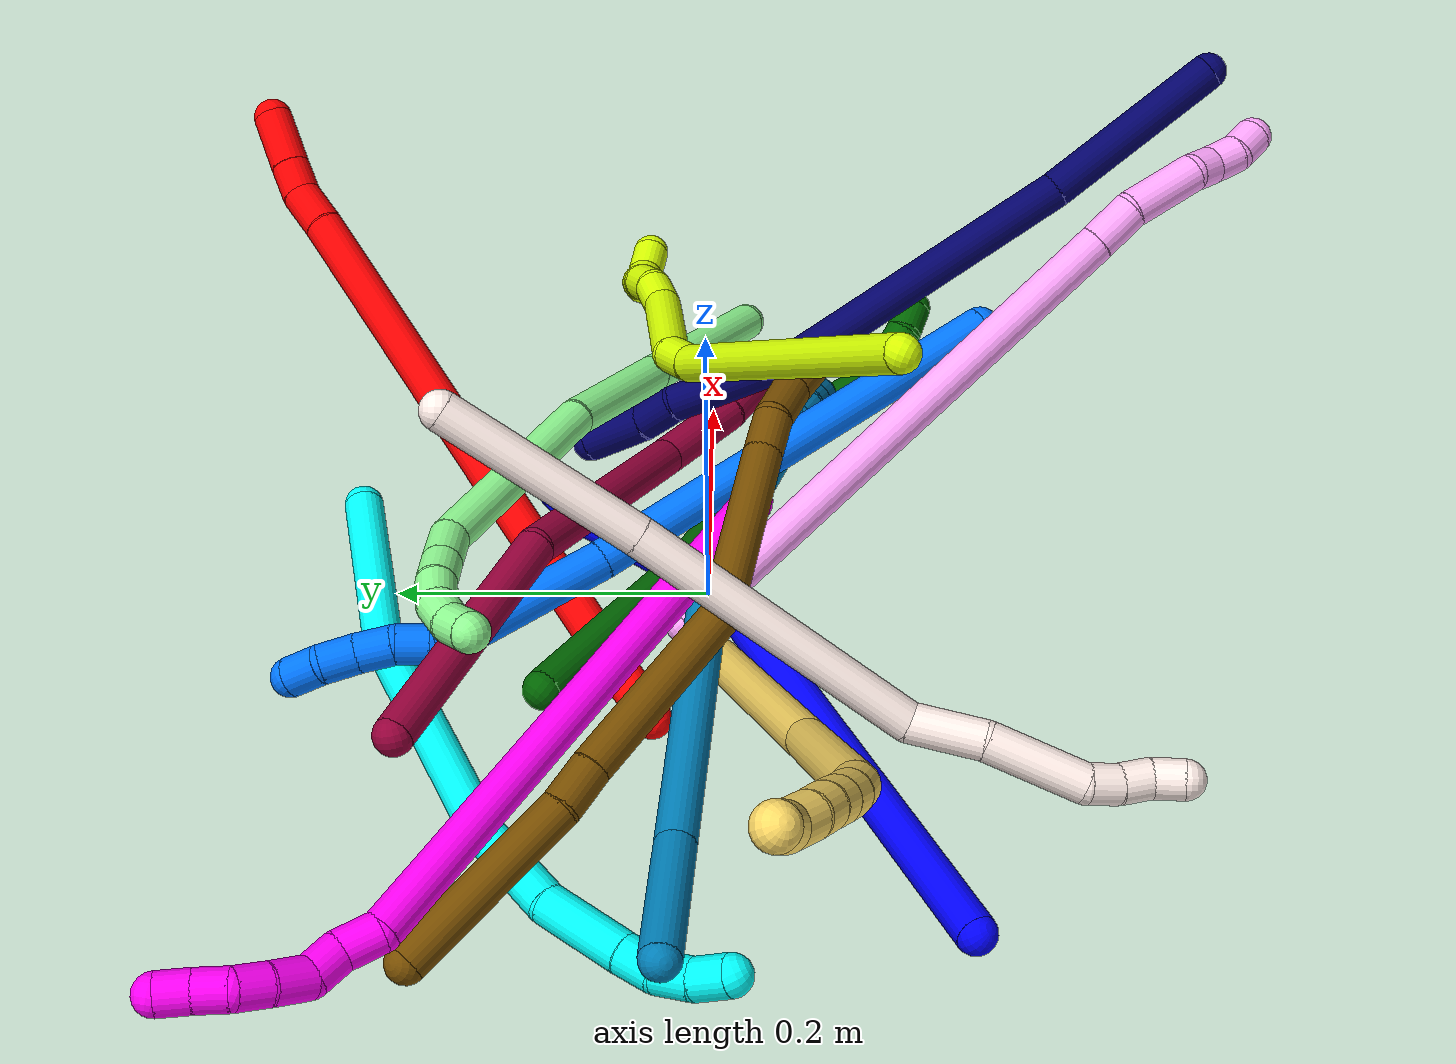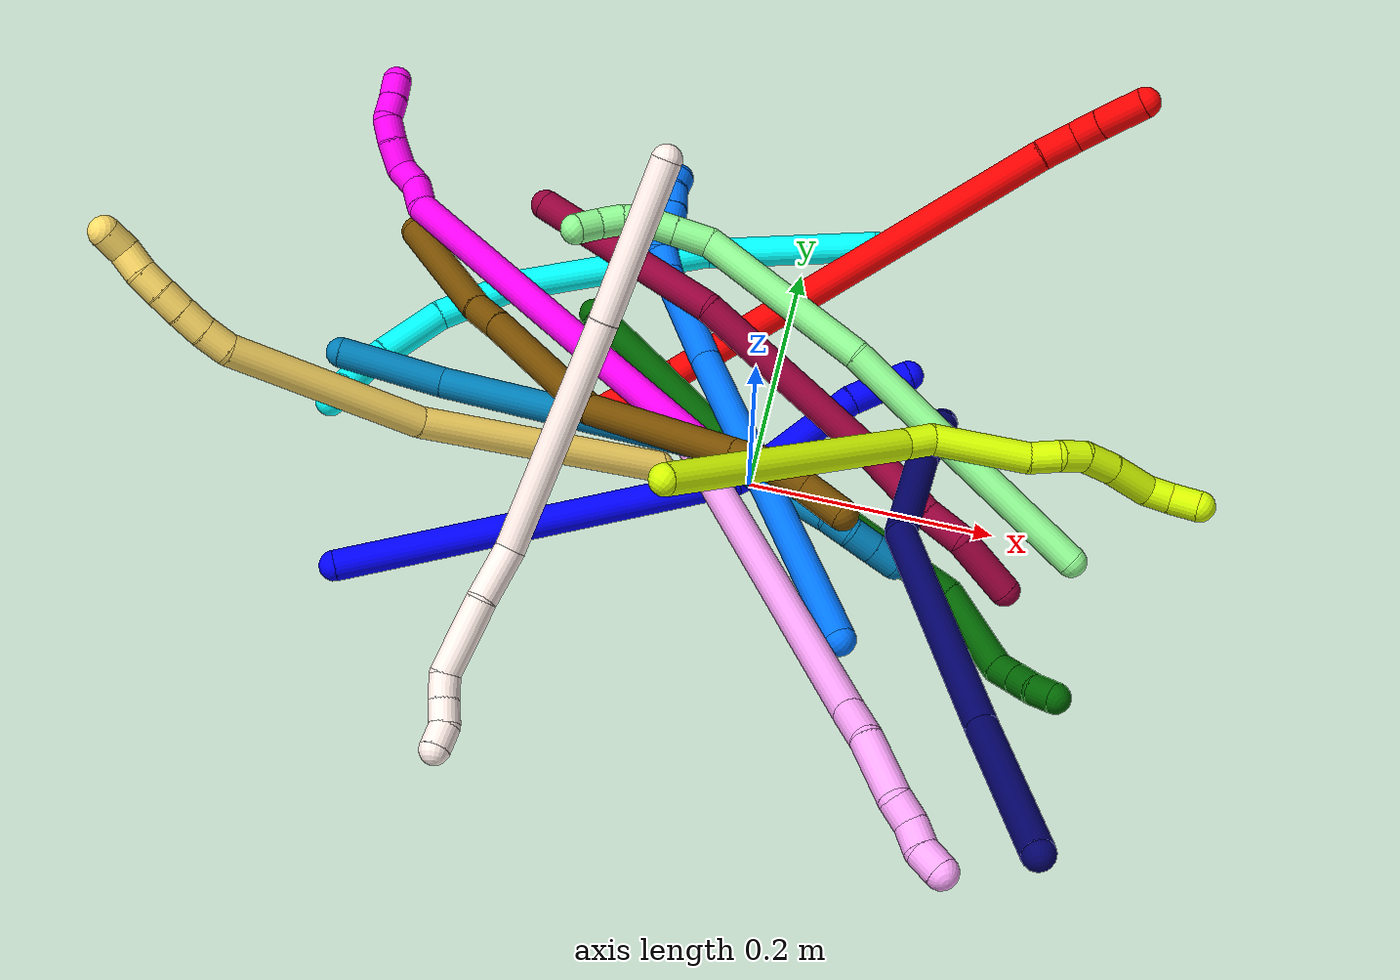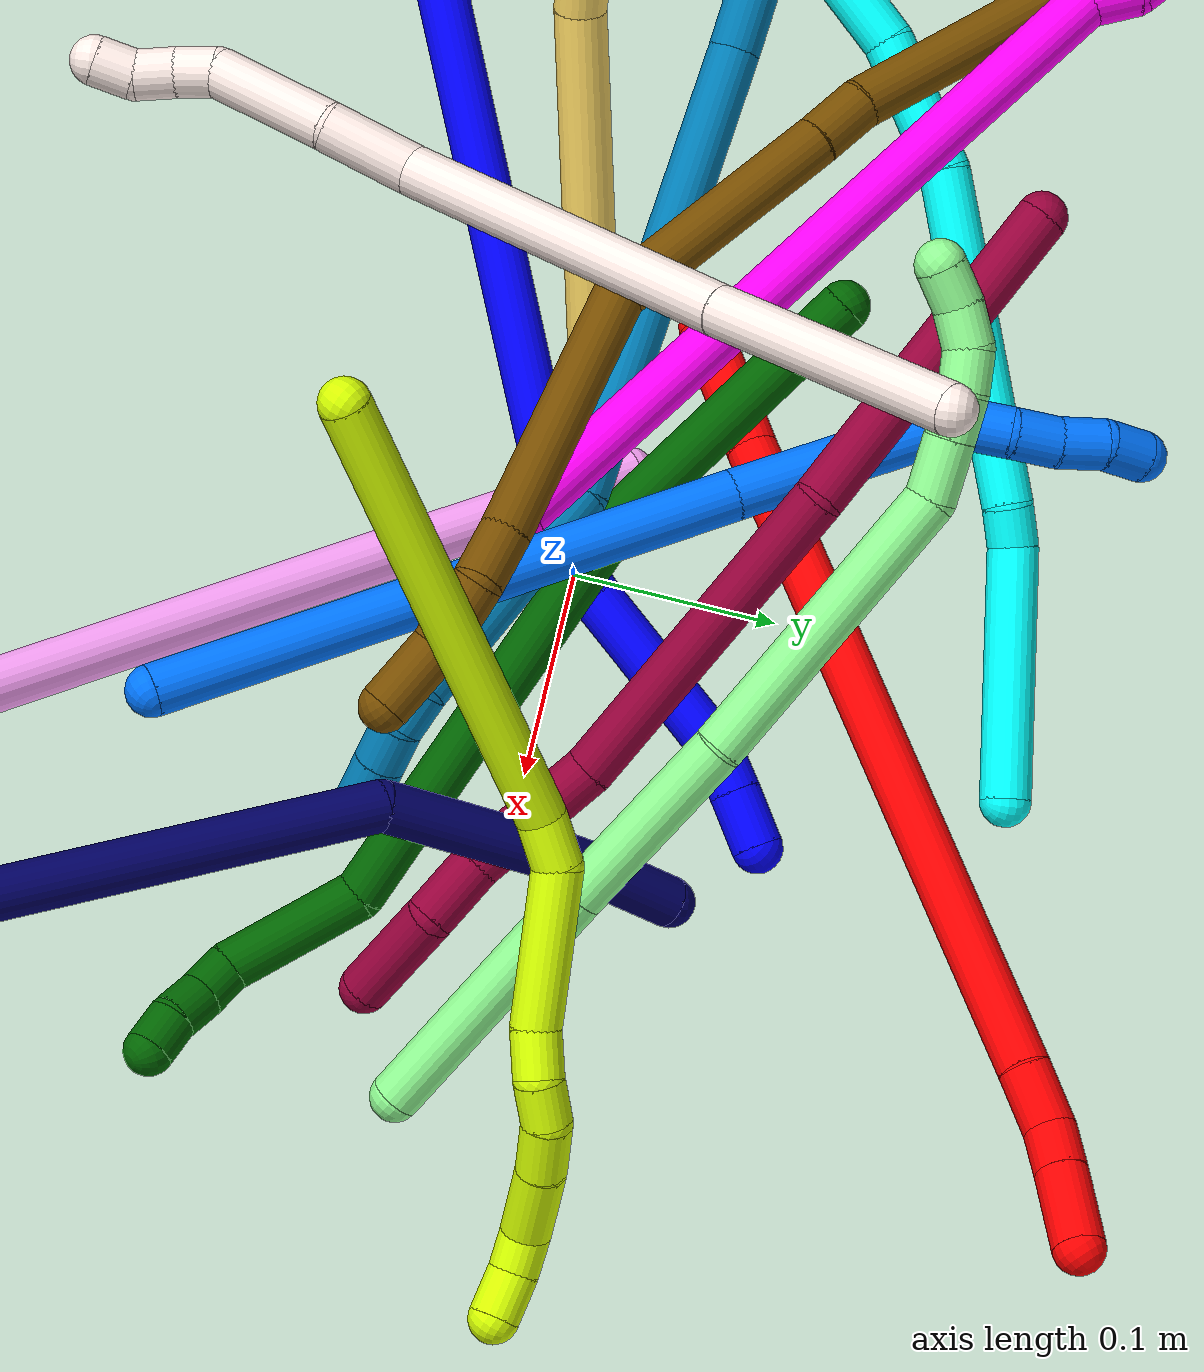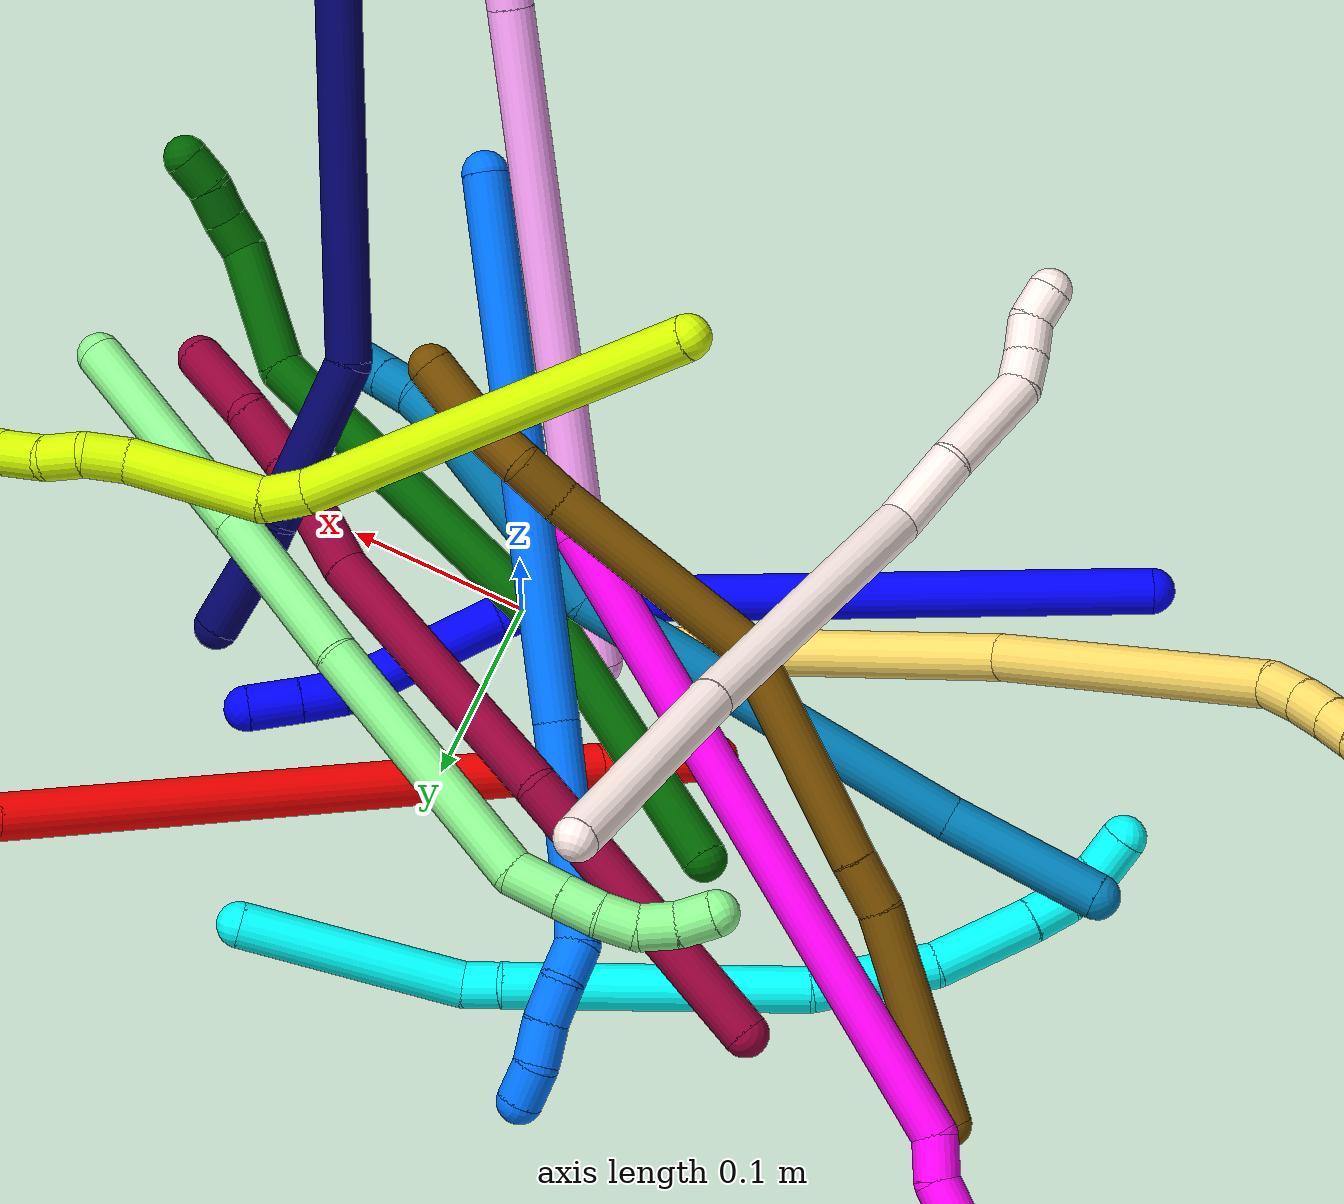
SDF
<sdf version="1.7">
 <world name="default">
  <plugin name="TubeGeneratorPlugin" filename="libtube_generator_plugin.so"/>
  <model name="photoneo_s_sensor">
   <static>1</static>
   <pose>0 0 2 1.57079 1.57079 3.14159</pose>
   <link name="link">
    <inertial><mass>0.1</mass></inertial>
    <sensor name="sensor" type="depth">
     <update_rate>30</update_rate>
     <camera>
      <horizontal_fov>1.22</horizontal_fov>
      <image><width>1920</width><height>1200</height><format>B8G8R8</format></image>
      <clip><near>0.1</near><far>4</far></clip>
      <depth_camera><output>points</output></depth_camera>
     </camera>
     <plugin name="camera_plugin" filename="libgazebo_ros_depth_camera.so">
      <baseline>0.2</baseline>
      <alwaysOn>1</alwaysOn>
      <updateRate>0.0</updateRate>
      <cameraName>camera_ir</cameraName>
      <imageTopicName>/camera/color/image_raw</imageTopicName>
      <cameraInfoTopicName>/camera/color/camera_info</cameraInfoTopicName>
      <depthImageTopicName>/camera/depth/image_raw</depthImageTopicName>
      <depthImageCameraInfoTopicName>/camera/depth/camera_info</depthImageCameraInfoTopicName>
      <pointCloudTopicName>/camera/depth/points</pointCloudTopicName>
      <frameName>fr_optical</frameName>
      <pointCloudCutoff>0.1</pointCloudCutoff>
      <pointCloudCutoffMax>2.0</pointCloudCutoffMax>
      <distortionK1>0</distortionK1>
      <distortionK2>0</distortionK2>
      <distortionK3>0</distortionK3>
      <distortionT1>0</distortionT1>
      <distortionT2>0</distortionT2>
      <CxPrime>0</CxPrime>
      <Cx>0</Cx>
      <Cy>0</Cy>
      <focalLength>0</focalLength>
      <hackBaseline>0</hackBaseline>
     </plugin>
    </sensor>
   </link>
  </model>
  <gravity>0 0 -9.8</gravity>
  <magnetic_field>6e-06 2.3e-05 -4.2e-05</magnetic_field>
  <atmosphere type="adiabatic"/>
  <physics name="default_physics" default="0" type="ode">
   <max_step_size>0.003</max_step_size>
   <real_time_factor>1</real_time_factor>
   <real_time_update_rate>1000</real_time_update_rate>
   <max_contacts>10000</max_contacts>
   <ode>
    <solver>
     <type>quick</type>
     <iters>100</iters>
     <sor>1.3</sor>
     <use_dynamic_moi_rescaling>0</use_dynamic_moi_rescaling>
    </solver>
    <constraints>
     <contact_max_correcting_vel>0</contact_max_correcting_vel>
     <contact_surface_layer>0.001</contact_surface_layer>
     <cfm>0</cfm>
     <erp>0.2</erp>
    </constraints>
   </ode>
  </physics>
  <scene><ambient>0.4 0.4 0.4 1</ambient><background>0.7 0.7 0.7 1</background><shadows>0</shadows></scene>
  <audio><device>default</device></audio>
  <spherical_coordinates>
   <surface_model>EARTH_WGS84</surface_model>
   <latitude_deg>0</latitude_deg>
   <longitude_deg>0</longitude_deg>
   <elevation>0</elevation>
   <heading_deg>0</heading_deg>
  </spherical_coordinates>
  <model name="bin">
   <static>1</static>
   <link name="bottom">
    <collision name="collision-bottom">
     <pose>0 0 -0.01 0 -0 0</pose>
     <geometry><box><size>0.8 0.6 0.02</size></box></geometry>
     <surface>
      <friction><ode><mu>100</mu><mu2>100</mu2></ode></friction>
      <contact><collide_bitmask>65535</collide_bitmask></contact>
     </surface>
    </collision>
   </link>
   <link name="west_wall">
    <collision name="collision-west_wall">
     <pose>-0.41 0 0.1 0 -0 0</pose>
     <geometry><box><size>0.02 0.6 0.2</size></box></geometry>
     <surface>
      <friction><ode><mu>100</mu><mu2>100</mu2></ode></friction>
      <contact><collide_bitmask>65535</collide_bitmask></contact>
     </surface>
    </collision>
   </link>
   <link name="east_wall">
    <collision name="collision-east_wall">
     <pose>0.41 0 0.1 0 -0 0</pose>
     <geometry><box><size>0.02 0.6 0.2</size></box></geometry>
     <surface>
      <friction><ode><mu>100</mu><mu2>100</mu2></ode></friction>
      <contact><collide_bitmask>65535</collide_bitmask></contact>
     </surface>
    </collision>
   </link>
   <link name="south_wall">
    <collision name="collision-south_wall">
     <pose>0 -0.31 0.1 0 -0 0</pose>
     <geometry><box><size>0.8 0.02 0.2</size></box></geometry>
     <surface>
      <friction><ode><mu>100</mu><mu2>100</mu2></ode></friction>
      <contact><collide_bitmask>65535</collide_bitmask></contact>
     </surface>
    </collision>
   </link>
   <link name="north_wall">
    <collision name="collision-north_wall">
     <pose>0 0.31 0.1 0 -0 0</pose>
     <geometry><box><size>0.8 0.02 0.2</size></box></geometry>
     <surface>
      <friction><ode><mu>100</mu><mu2>100</mu2></ode></friction>
      <contact><collide_bitmask>65535</collide_bitmask></contact>
     </surface>
    </collision>
   </link>
  </model>
  <model name="1">
   <static>0</static>
   <link name="1">
    <collision name="collision-cylinder-e_1_1_4">
     <pose>0.067224 0.115352 0.093211 -0.89116 0.425581 -0.205661</pose>
     <geometry><cylinder><radius>0.0125</radius><length>0.325659</length></cylinder></geometry>
     <surface>
      <friction><ode><mu>1.16</mu><mu2>1.16</mu2><slip1>0</slip1><slip2>0</slip2></ode></friction>
      <contact><ode><kp>1e+06</kp><kd>1</kd><max_vel>0</max_vel><min_depth>0.001</min_depth></ode></contact>
     </surface>
    </collision>
    <visual name="visual-cylinder-e_1_1_4">
     <pose>0.067224 0.115352 0.093211 -0.89116 0.425581 -0.205661</pose>
     <geometry><cylinder><radius>0.0125</radius><length>0.325659</length></cylinder></geometry>
     <material><ambient>0 0 1 1</ambient></material>
    </visual>
    <collision name="collision-cylinder-e_2_4_5">
     <pose>0.141596 0.237093 0.197056 -0.541038 0.522737 -0.148086</pose>
     <geometry><cylinder><radius>0.0125</radius><length>0.028635</length></cylinder></geometry>
     <surface>
      <friction><ode><mu>1.16</mu><mu2>1.16</mu2><slip1>0</slip1><slip2>0</slip2></ode></friction>
      <contact><ode><kp>1e+06</kp><kd>1</kd><max_vel>0</max_vel><min_depth>0.001</min_depth></ode></contact>
     </surface>
    </collision>
    <visual name="visual-cylinder-e_2_4_5">
     <pose>0.141596 0.237093 0.197056 -0.541038 0.522737 -0.148086</pose>
     <geometry><cylinder><radius>0.0125</radius><length>0.028635</length></cylinder></geometry>
     <material><ambient>0 0 1 1</ambient></material>
    </visual>
    <collision name="collision-cylinder-e_3_5_6">
     <pose>0.178696 0.259241 0.239662 -0.457946 0.698814 -0.169427</pose>
     <geometry><cylinder><radius>0.0125</radius><length>0.093116</length></cylinder></geometry>
     <surface>
      <friction><ode><mu>1.16</mu><mu2>1.16</mu2><slip1>0</slip1><slip2>0</slip2></ode></friction>
      <contact><ode><kp>1e+06</kp><kd>1</kd><max_vel>0</max_vel><min_depth>0.001</min_depth></ode></contact>
     </surface>
    </collision>
    <visual name="visual-cylinder-e_3_5_6">
     <pose>0.178696 0.259241 0.239662 -0.457946 0.698814 -0.169427</pose>
     <geometry><cylinder><radius>0.0125</radius><length>0.093116</length></cylinder></geometry>
     <material><ambient>0 0 1 1</ambient></material>
    </visual>
    <collision name="collision-cylinder-e_4_6_7">
     <pose>0.215443 0.281933 0.278492 -0.790871 0.608616 -0.260707</pose>
     <geometry><cylinder><radius>0.0125</radius><length>0.023773</length></cylinder></geometry>
     <surface>
      <friction><ode><mu>1.16</mu><mu2>1.16</mu2><slip1>0</slip1><slip2>0</slip2></ode></friction>
      <contact><ode><kp>1e+06</kp><kd>1</kd><max_vel>0</max_vel><min_depth>0.001</min_depth></ode></contact>
     </surface>
    </collision>
    <visual name="visual-cylinder-e_4_6_7">
     <pose>0.215443 0.281933 0.278492 -0.790871 0.608616 -0.260707</pose>
     <geometry><cylinder><radius>0.0125</radius><length>0.023773</length></cylinder></geometry>
     <material><ambient>0 0 1 1</ambient></material>
    </visual>
    <collision name="collision-cylinder-e_5_7_2">
     <pose>0.230325 0.297514 0.293562 -0.811212 0.59588 -0.262218</pose>
     <geometry><cylinder><radius>0.0125</radius><length>0.028817</length></cylinder></geometry>
     <surface>
      <friction><ode><mu>1.16</mu><mu2>1.16</mu2><slip1>0</slip1><slip2>0</slip2></ode></friction>
      <contact><ode><kp>1e+06</kp><kd>1</kd><max_vel>0</max_vel><min_depth>0.001</min_depth></ode></contact>
     </surface>
    </collision>
    <visual name="visual-cylinder-e_5_7_2">
     <pose>0.230325 0.297514 0.293562 -0.811212 0.59588 -0.262218</pose>
     <geometry><cylinder><radius>0.0125</radius><length>0.028817</length></cylinder></geometry>
     <material><ambient>0 0 1 1</ambient></material>
    </visual>
    <collision name="collision-sphere-2">
     <pose>0.238412 0.306161 0.301774 0 -0 0</pose>
     <geometry><sphere><radius>0.0125</radius></sphere></geometry>
     <surface>
      <friction><ode><mu>1.16</mu><mu2>1.16</mu2><slip1>0</slip1><slip2>0</slip2></ode></friction>
      <contact><ode><kp>1e+06</kp><kd>1</kd><max_vel>0</max_vel><min_depth>0.001</min_depth></ode></contact>
     </surface>
    </collision>
    <visual name="visual-sphere-2">
     <pose>0.238412 0.306161 0.301774 0 -0 0</pose>
     <geometry><sphere><radius>0.0125</radius></sphere></geometry>
     <material><ambient>0 0 1 1</ambient></material>
    </visual>
    <collision name="collision-sphere-7">
     <pose>0.222239 0.288867 0.28535 0 -0 0</pose>
     <geometry><sphere><radius>0.0125</radius></sphere></geometry>
     <surface>
      <friction><ode><mu>1.16</mu><mu2>1.16</mu2><slip1>0</slip1><slip2>0</slip2></ode></friction>
      <contact><ode><kp>1e+06</kp><kd>1</kd><max_vel>0</max_vel><min_depth>0.001</min_depth></ode></contact>
     </surface>
    </collision>
    <visual name="visual-sphere-7">
     <pose>0.222239 0.288867 0.28535 0 -0 0</pose>
     <geometry><sphere><radius>0.0125</radius></sphere></geometry>
     <material><ambient>0 0 1 1</ambient></material>
    </visual>
    <collision name="collision-sphere-6">
     <pose>0.208647 0.275 0.271634 0 -0 0</pose>
     <geometry><sphere><radius>0.0125</radius></sphere></geometry>
     <surface>
      <friction><ode><mu>1.16</mu><mu2>1.16</mu2><slip1>0</slip1><slip2>0</slip2></ode></friction>
      <contact><ode><kp>1e+06</kp><kd>1</kd><max_vel>0</max_vel><min_depth>0.001</min_depth></ode></contact>
     </surface>
    </collision>
    <visual name="visual-sphere-6">
     <pose>0.208647 0.275 0.271634 0 -0 0</pose>
     <geometry><sphere><radius>0.0125</radius></sphere></geometry>
     <material><ambient>0 0 1 1</ambient></material>
    </visual>
    <collision name="collision-sphere-5">
     <pose>0.148744 0.243482 0.20769 0 -0 0</pose>
     <geometry><sphere><radius>0.0125</radius></sphere></geometry>
     <surface>
      <friction><ode><mu>1.16</mu><mu2>1.16</mu2><slip1>0</slip1><slip2>0</slip2></ode></friction>
      <contact><ode><kp>1e+06</kp><kd>1</kd><max_vel>0</max_vel><min_depth>0.001</min_depth></ode></contact>
     </surface>
    </collision>
    <visual name="visual-sphere-5">
     <pose>0.148744 0.243482 0.20769 0 -0 0</pose>
     <geometry><sphere><radius>0.0125</radius></sphere></geometry>
     <material><ambient>0 0 1 1</ambient></material>
    </visual>
    <collision name="collision-sphere-1">
     <geometry><sphere><radius>0.0125</radius></sphere></geometry>
     <surface>
      <friction><ode><mu>1.16</mu><mu2>1.16</mu2><slip1>0</slip1><slip2>0</slip2></ode></friction>
      <contact><ode><kp>1e+06</kp><kd>1</kd><max_vel>0</max_vel><min_depth>0.001</min_depth></ode></contact>
     </surface>
    </collision>
    <visual name="visual-sphere-1">
     <geometry><sphere><radius>0.0125</radius></sphere></geometry>
     <material><ambient>0 0 1 1</ambient></material>
    </visual>
    <collision name="collision-sphere-4">
     <pose>0.134449 0.230704 0.186422 0 -0 0</pose>
     <geometry><sphere><radius>0.0125</radius></sphere></geometry>
     <surface>
      <friction><ode><mu>1.16</mu><mu2>1.16</mu2><slip1>0</slip1><slip2>0</slip2></ode></friction>
      <contact><ode><kp>1e+06</kp><kd>1</kd><max_vel>0</max_vel><min_depth>0.001</min_depth></ode></contact>
     </surface>
    </collision>
    <visual name="visual-sphere-4">
     <pose>0.134449 0.230704 0.186422 0 -0 0</pose>
     <geometry><sphere><radius>0.0125</radius></sphere></geometry>
     <material><ambient>0 0 1 1</ambient></material>
    </visual>
    <inertial>
     <pose>0.10869 0.16754 0.146789 0 -0 0</pose>
     <mass>0.5</mass>
     <inertia>
      <ixx>0.002108</ixx>
      <ixy>0</ixy>
      <ixz>0</ixz>
      <iyy>0.001517</iyy>
      <iyz>0</iyz>
      <izz>-0.003296</izz>
     </inertia>
    </inertial>
   </link>
   <pose>-0.30414 -0.152167 0.011496 2.91241 -0.779257 1.42184</pose>
  </model>
  <model name="2">
   <static>0</static>
   <link name="2">
    <collision name="collision-cylinder-e_1_1_4">
     <pose>-0.002289 0.008768 0.032505 -0.263465 -0.067887 0.008998</pose>
     <geometry><cylinder><radius>0.0125</radius><length>0.067489</length></cylinder></geometry>
     <surface>
      <friction><ode><mu>1.16</mu><mu2>1.16</mu2><slip1>0</slip1><slip2>0</slip2></ode></friction>
      <contact><ode><kp>1e+06</kp><kd>1</kd><max_vel>0</max_vel><min_depth>0.001</min_depth></ode></contact>
     </surface>
    </collision>
    <visual name="visual-cylinder-e_1_1_4">
     <pose>-0.002289 0.008768 0.032505 -0.263465 -0.067887 0.008998</pose>
     <geometry><cylinder><radius>0.0125</radius><length>0.067489</length></cylinder></geometry>
     <material><ambient>1 0 0 1</ambient></material>
    </visual>
    <collision name="collision-cylinder-e_2_4_5">
     <pose>-0.001518 0.070416 0.22719 -0.315189 0.017935 -0.00285</pose>
     <geometry><cylinder><radius>0.0125</radius><length>0.341222</length></cylinder></geometry>
     <surface>
      <friction><ode><mu>1.16</mu><mu2>1.16</mu2><slip1>0</slip1><slip2>0</slip2></ode></friction>
      <contact><ode><kp>1e+06</kp><kd>1</kd><max_vel>0</max_vel><min_depth>0.001</min_depth></ode></contact>
     </surface>
    </collision>
    <visual name="visual-cylinder-e_2_4_5">
     <pose>-0.001518 0.070416 0.22719 -0.315189 0.017935 -0.00285</pose>
     <geometry><cylinder><radius>0.0125</radius><length>0.341222</length></cylinder></geometry>
     <material><ambient>1 0 0 1</ambient></material>
    </visual>
    <collision name="collision-cylinder-e_3_5_6">
     <pose>0.000603 0.126858 0.404117 -0.237015 -0.061778 0.007358</pose>
     <geometry><cylinder><radius>0.0125</radius><length>0.0304</length></cylinder></geometry>
     <surface>
      <friction><ode><mu>1.16</mu><mu2>1.16</mu2><slip1>0</slip1><slip2>0</slip2></ode></friction>
      <contact><ode><kp>1e+06</kp><kd>1</kd><max_vel>0</max_vel><min_depth>0.001</min_depth></ode></contact>
     </surface>
    </collision>
    <visual name="visual-cylinder-e_3_5_6">
     <pose>0.000603 0.126858 0.404117 -0.237015 -0.061778 0.007358</pose>
     <geometry><cylinder><radius>0.0125</radius><length>0.0304</length></cylinder></geometry>
     <material><ambient>1 0 0 1</ambient></material>
    </visual>
    <collision name="collision-cylinder-e_4_6_7">
     <pose>-0.000216 0.136125 0.428541 -0.532652 0.010639 -0.002902</pose>
     <geometry><cylinder><radius>0.0125</radius><length>0.022468</length></cylinder></geometry>
     <surface>
      <friction><ode><mu>1.16</mu><mu2>1.16</mu2><slip1>0</slip1><slip2>0</slip2></ode></friction>
      <contact><ode><kp>1e+06</kp><kd>1</kd><max_vel>0</max_vel><min_depth>0.001</min_depth></ode></contact>
     </surface>
    </collision>
    <visual name="visual-cylinder-e_4_6_7">
     <pose>-0.000216 0.136125 0.428541 -0.532652 0.010639 -0.002902</pose>
     <geometry><cylinder><radius>0.0125</radius><length>0.022468</length></cylinder></geometry>
     <material><ambient>1 0 0 1</ambient></material>
    </visual>
    <collision name="collision-cylinder-e_5_7_2">
     <pose>-0.000463 0.151674 0.45471 -0.538164 -0.019078 0.005261</pose>
     <geometry><cylinder><radius>0.0125</radius><length>0.038422</length></cylinder></geometry>
     <surface>
      <friction><ode><mu>1.16</mu><mu2>1.16</mu2><slip1>0</slip1><slip2>0</slip2></ode></friction>
      <contact><ode><kp>1e+06</kp><kd>1</kd><max_vel>0</max_vel><min_depth>0.001</min_depth></ode></contact>
     </surface>
    </collision>
    <visual name="visual-cylinder-e_5_7_2">
     <pose>-0.000463 0.151674 0.45471 -0.538164 -0.019078 0.005261</pose>
     <geometry><cylinder><radius>0.0125</radius><length>0.038422</length></cylinder></geometry>
     <material><ambient>1 0 0 1</ambient></material>
    </visual>
    <collision name="collision-sphere-2">
     <pose>-0.00083 0.161519 0.471203 0 -0 0</pose>
     <geometry><sphere><radius>0.0125</radius></sphere></geometry>
     <surface>
      <friction><ode><mu>1.16</mu><mu2>1.16</mu2><slip1>0</slip1><slip2>0</slip2></ode></friction>
      <contact><ode><kp>1e+06</kp><kd>1</kd><max_vel>0</max_vel><min_depth>0.001</min_depth></ode></contact>
     </surface>
    </collision>
    <visual name="visual-sphere-2">
     <pose>-0.00083 0.161519 0.471203 0 -0 0</pose>
     <geometry><sphere><radius>0.0125</radius></sphere></geometry>
     <material><ambient>1 0 0 1</ambient></material>
    </visual>
    <collision name="collision-sphere-7">
     <pose>-9.7e-05 0.141829 0.438218 0 -0 0</pose>
     <geometry><sphere><radius>0.0125</radius></sphere></geometry>
     <surface>
      <friction><ode><mu>1.16</mu><mu2>1.16</mu2><slip1>0</slip1><slip2>0</slip2></ode></friction>
      <contact><ode><kp>1e+06</kp><kd>1</kd><max_vel>0</max_vel><min_depth>0.001</min_depth></ode></contact>
     </surface>
    </collision>
    <visual name="visual-sphere-7">
     <pose>-9.7e-05 0.141829 0.438218 0 -0 0</pose>
     <geometry><sphere><radius>0.0125</radius></sphere></geometry>
     <material><ambient>1 0 0 1</ambient></material>
    </visual>
    <collision name="collision-sphere-6">
     <pose>-0.000336 0.13042 0.418864 0 -0 0</pose>
     <geometry><sphere><radius>0.0125</radius></sphere></geometry>
     <surface>
      <friction><ode><mu>1.16</mu><mu2>1.16</mu2><slip1>0</slip1><slip2>0</slip2></ode></friction>
      <contact><ode><kp>1e+06</kp><kd>1</kd><max_vel>0</max_vel><min_depth>0.001</min_depth></ode></contact>
     </surface>
    </collision>
    <visual name="visual-sphere-6">
     <pose>-0.000336 0.13042 0.418864 0 -0 0</pose>
     <geometry><sphere><radius>0.0125</radius></sphere></geometry>
     <material><ambient>1 0 0 1</ambient></material>
    </visual>
    <collision name="collision-sphere-5">
     <pose>0.001541 0.123296 0.38937 0 -0 0</pose>
     <geometry><sphere><radius>0.0125</radius></sphere></geometry>
     <surface>
      <friction><ode><mu>1.16</mu><mu2>1.16</mu2><slip1>0</slip1><slip2>0</slip2></ode></friction>
      <contact><ode><kp>1e+06</kp><kd>1</kd><max_vel>0</max_vel><min_depth>0.001</min_depth></ode></contact>
     </surface>
    </collision>
    <visual name="visual-sphere-5">
     <pose>0.001541 0.123296 0.38937 0 -0 0</pose>
     <geometry><sphere><radius>0.0125</radius></sphere></geometry>
     <material><ambient>1 0 0 1</ambient></material>
    </visual>
    <collision name="collision-sphere-1">
     <geometry><sphere><radius>0.0125</radius></sphere></geometry>
     <surface>
      <friction><ode><mu>1.16</mu><mu2>1.16</mu2><slip1>0</slip1><slip2>0</slip2></ode></friction>
      <contact><ode><kp>1e+06</kp><kd>1</kd><max_vel>0</max_vel><min_depth>0.001</min_depth></ode></contact>
     </surface>
    </collision>
    <visual name="visual-sphere-1">
     <geometry><sphere><radius>0.0125</radius></sphere></geometry>
     <material><ambient>1 0 0 1</ambient></material>
    </visual>
    <collision name="collision-sphere-4">
     <pose>-0.004578 0.017535 0.06501 0 -0 0</pose>
     <geometry><sphere><radius>0.0125</radius></sphere></geometry>
     <surface>
      <friction><ode><mu>1.16</mu><mu2>1.16</mu2><slip1>0</slip1><slip2>0</slip2></ode></friction>
      <contact><ode><kp>1e+06</kp><kd>1</kd><max_vel>0</max_vel><min_depth>0.001</min_depth></ode></contact>
     </surface>
    </collision>
    <visual name="visual-sphere-4">
     <pose>-0.004578 0.017535 0.06501 0 -0 0</pose>
     <geometry><sphere><radius>0.0125</radius></sphere></geometry>
     <material><ambient>1 0 0 1</ambient></material>
    </visual>
    <inertial>
     <pose>-0.001354 0.074723 0.2382 0 -0 0</pose>
     <mass>0.5</mass>
     <inertia>
      <ixx>0.003354</ixx>
      <ixy>0</ixy>
      <ixz>0</ixz>
      <iyy>0.003201</iyy>
      <iyz>0</iyz>
      <izz>-0.001063</izz>
     </inertia>
    </inertial>
   </link>
   <pose>-0.130167 0.032472 0.011489 1.37905 -0.639296 2.51008</pose>
  </model>
  <model name="3">
   <static>0</static>
   <link name="3">
    <collision name="collision-cylinder-e_1_1_4">
     <pose>-0.061561 -0.001895 -0.003908 2.69007 -1.50036 -2.65832</pose>
     <geometry><cylinder><radius>0.0125</radius><length>0.123428</length></cylinder></geometry>
     <surface>
      <friction><ode><mu>1.16</mu><mu2>1.16</mu2><slip1>0</slip1><slip2>0</slip2></ode></friction>
      <contact><ode><kp>1e+06</kp><kd>1</kd><max_vel>0</max_vel><min_depth>0.001</min_depth></ode></contact>
     </surface>
    </collision>
    <visual name="visual-cylinder-e_1_1_4">
     <pose>-0.061561 -0.001895 -0.003908 2.69007 -1.50036 -2.65832</pose>
     <geometry><cylinder><radius>0.0125</radius><length>0.123428</length></cylinder></geometry>
     <material><ambient>0.003922 1 0.996078 1</ambient></material>
    </visual>
    <collision name="collision-cylinder-e_2_4_5">
     <pose>-0.132891 -0.001556 -0.005305 -0.72733 -1.23947 0.530321</pose>
     <geometry><cylinder><radius>0.0125</radius><length>0.020663</length></cylinder></geometry>
     <surface>
      <friction><ode><mu>1.16</mu><mu2>1.16</mu2><slip1>0</slip1><slip2>0</slip2></ode></friction>
      <contact><ode><kp>1e+06</kp><kd>1</kd><max_vel>0</max_vel><min_depth>0.001</min_depth></ode></contact>
     </surface>
    </collision>
    <visual name="visual-cylinder-e_2_4_5">
     <pose>-0.132891 -0.001556 -0.005305 -0.72733 -1.23947 0.530321</pose>
     <geometry><cylinder><radius>0.0125</radius><length>0.020663</length></cylinder></geometry>
     <material><ambient>0.003922 1 0.996078 1</ambient></material>
    </visual>
    <collision name="collision-cylinder-e_3_5_6">
     <pose>-0.222796 0.000569 0.013103 0.006918 -1.37494 -0.005681</pose>
     <geometry><cylinder><radius>0.0125</radius><length>0.163395</length></cylinder></geometry>
     <surface>
      <friction><ode><mu>1.16</mu><mu2>1.16</mu2><slip1>0</slip1><slip2>0</slip2></ode></friction>
      <contact><ode><kp>1e+06</kp><kd>1</kd><max_vel>0</max_vel><min_depth>0.001</min_depth></ode></contact>
     </surface>
    </collision>
    <visual name="visual-cylinder-e_3_5_6">
     <pose>-0.222796 0.000569 0.013103 0.006918 -1.37494 -0.005681</pose>
     <geometry><cylinder><radius>0.0125</radius><length>0.163395</length></cylinder></geometry>
     <material><ambient>0.003922 1 0.996078 1</ambient></material>
    </visual>
    <collision name="collision-cylinder-e_4_6_7">
     <pose>-0.33422 -0.003633 0.04159 0.314292 -1.17056 -0.20926</pose>
     <geometry><cylinder><radius>0.0125</radius><length>0.067946</length></cylinder></geometry>
     <surface>
      <friction><ode><mu>1.16</mu><mu2>1.16</mu2><slip1>0</slip1><slip2>0</slip2></ode></friction>
      <contact><ode><kp>1e+06</kp><kd>1</kd><max_vel>0</max_vel><min_depth>0.001</min_depth></ode></contact>
     </surface>
    </collision>
    <visual name="visual-cylinder-e_4_6_7">
     <pose>-0.33422 -0.003633 0.04159 0.314292 -1.17056 -0.20926</pose>
     <geometry><cylinder><radius>0.0125</radius><length>0.067946</length></cylinder></geometry>
     <material><ambient>0.003922 1 0.996078 1</ambient></material>
    </visual>
    <collision name="collision-cylinder-e_5_7_8">
     <pose>-0.388181 -0.013532 0.070157 0.348549 -0.927423 -0.175636</pose>
     <geometry><cylinder><radius>0.0125</radius><length>0.056679</length></cylinder></geometry>
     <surface>
      <friction><ode><mu>1.16</mu><mu2>1.16</mu2><slip1>0</slip1><slip2>0</slip2></ode></friction>
      <contact><ode><kp>1e+06</kp><kd>1</kd><max_vel>0</max_vel><min_depth>0.001</min_depth></ode></contact>
     </surface>
    </collision>
    <visual name="visual-cylinder-e_5_7_8">
     <pose>-0.388181 -0.013532 0.070157 0.348549 -0.927423 -0.175636</pose>
     <geometry><cylinder><radius>0.0125</radius><length>0.056679</length></cylinder></geometry>
     <material><ambient>0.003922 1 0.996078 1</ambient></material>
    </visual>
    <collision name="collision-cylinder-e_6_8_9">
     <pose>-0.419266 -0.021986 0.092885 0.373906 -0.859388 -0.172935</pose>
     <geometry><cylinder><radius>0.0125</radius><length>0.022209</length></cylinder></geometry>
     <surface>
      <friction><ode><mu>1.16</mu><mu2>1.16</mu2><slip1>0</slip1><slip2>0</slip2></ode></friction>
      <contact><ode><kp>1e+06</kp><kd>1</kd><max_vel>0</max_vel><min_depth>0.001</min_depth></ode></contact>
     </surface>
    </collision>
    <visual name="visual-cylinder-e_6_8_9">
     <pose>-0.419266 -0.021986 0.092885 0.373906 -0.859388 -0.172935</pose>
     <geometry><cylinder><radius>0.0125</radius><length>0.022209</length></cylinder></geometry>
     <material><ambient>0.003922 1 0.996078 1</ambient></material>
    </visual>
    <collision name="collision-cylinder-e_7_9_10">
     <pose>-0.434294 -0.0259 0.108836 0.136702 -0.618984 -0.043774</pose>
     <geometry><cylinder><radius>0.0125</radius><length>0.022808</length></cylinder></geometry>
     <surface>
      <friction><ode><mu>1.16</mu><mu2>1.16</mu2><slip1>0</slip1><slip2>0</slip2></ode></friction>
      <contact><ode><kp>1e+06</kp><kd>1</kd><max_vel>0</max_vel><min_depth>0.001</min_depth></ode></contact>
     </surface>
    </collision>
    <visual name="visual-cylinder-e_7_9_10">
     <pose>-0.434294 -0.0259 0.108836 0.136702 -0.618984 -0.043774</pose>
     <geometry><cylinder><radius>0.0125</radius><length>0.022808</length></cylinder></geometry>
     <material><ambient>0.003922 1 0.996078 1</ambient></material>
    </visual>
    <collision name="collision-cylinder-e_8_10_2">
     <pose>-0.445518 -0.0264 0.128476 -0.073243 -0.414646 0.015413</pose>
     <geometry><cylinder><radius>0.0125</radius><length>0.022873</length></cylinder></geometry>
     <surface>
      <friction><ode><mu>1.16</mu><mu2>1.16</mu2><slip1>0</slip1><slip2>0</slip2></ode></friction>
      <contact><ode><kp>1e+06</kp><kd>1</kd><max_vel>0</max_vel><min_depth>0.001</min_depth></ode></contact>
     </surface>
    </collision>
    <visual name="visual-cylinder-e_8_10_2">
     <pose>-0.445518 -0.0264 0.128476 -0.073243 -0.414646 0.015413</pose>
     <geometry><cylinder><radius>0.0125</radius><length>0.022873</length></cylinder></geometry>
     <material><ambient>0.003922 1 0.996078 1</ambient></material>
    </visual>
    <collision name="collision-sphere-2">
     <pose>-0.450125 -0.025634 0.138916 0 -0 0</pose>
     <geometry><sphere><radius>0.0125</radius></sphere></geometry>
     <surface>
      <friction><ode><mu>1.16</mu><mu2>1.16</mu2><slip1>0</slip1><slip2>0</slip2></ode></friction>
      <contact><ode><kp>1e+06</kp><kd>1</kd><max_vel>0</max_vel><min_depth>0.001</min_depth></ode></contact>
     </surface>
    </collision>
    <visual name="visual-sphere-2">
     <pose>-0.450125 -0.025634 0.138916 0 -0 0</pose>
     <geometry><sphere><radius>0.0125</radius></sphere></geometry>
     <material><ambient>0.003922 1 0.996078 1</ambient></material>
    </visual>
    <collision name="collision-sphere-10">
     <pose>-0.440911 -0.027166 0.118037 0 -0 0</pose>
     <geometry><sphere><radius>0.0125</radius></sphere></geometry>
     <surface>
      <friction><ode><mu>1.16</mu><mu2>1.16</mu2><slip1>0</slip1><slip2>0</slip2></ode></friction>
      <contact><ode><kp>1e+06</kp><kd>1</kd><max_vel>0</max_vel><min_depth>0.001</min_depth></ode></contact>
     </surface>
    </collision>
    <visual name="visual-sphere-10">
     <pose>-0.440911 -0.027166 0.118037 0 -0 0</pose>
     <geometry><sphere><radius>0.0125</radius></sphere></geometry>
     <material><ambient>0.003922 1 0.996078 1</ambient></material>
    </visual>
    <collision name="collision-sphere-9">
     <pose>-0.427678 -0.024634 0.099634 0 -0 0</pose>
     <geometry><sphere><radius>0.0125</radius></sphere></geometry>
     <surface>
      <friction><ode><mu>1.16</mu><mu2>1.16</mu2><slip1>0</slip1><slip2>0</slip2></ode></friction>
      <contact><ode><kp>1e+06</kp><kd>1</kd><max_vel>0</max_vel><min_depth>0.001</min_depth></ode></contact>
     </surface>
    </collision>
    <visual name="visual-sphere-9">
     <pose>-0.427678 -0.024634 0.099634 0 -0 0</pose>
     <geometry><sphere><radius>0.0125</radius></sphere></geometry>
     <material><ambient>0.003922 1 0.996078 1</ambient></material>
    </visual>
    <collision name="collision-sphere-4">
     <pose>-0.123122 -0.00379 -0.007816 0 -0 0</pose>
     <geometry><sphere><radius>0.0125</radius></sphere></geometry>
     <surface>
      <friction><ode><mu>1.16</mu><mu2>1.16</mu2><slip1>0</slip1><slip2>0</slip2></ode></friction>
      <contact><ode><kp>1e+06</kp><kd>1</kd><max_vel>0</max_vel><min_depth>0.001</min_depth></ode></contact>
     </surface>
    </collision>
    <visual name="visual-sphere-4">
     <pose>-0.123122 -0.00379 -0.007816 0 -0 0</pose>
     <geometry><sphere><radius>0.0125</radius></sphere></geometry>
     <material><ambient>0.003922 1 0.996078 1</ambient></material>
    </visual>
    <collision name="collision-sphere-1">
     <geometry><sphere><radius>0.0125</radius></sphere></geometry>
     <surface>
      <friction><ode><mu>1.16</mu><mu2>1.16</mu2><slip1>0</slip1><slip2>0</slip2></ode></friction>
      <contact><ode><kp>1e+06</kp><kd>1</kd><max_vel>0</max_vel><min_depth>0.001</min_depth></ode></contact>
     </surface>
    </collision>
    <visual name="visual-sphere-1">
     <geometry><sphere><radius>0.0125</radius></sphere></geometry>
     <material><ambient>0.003922 1 0.996078 1</ambient></material>
    </visual>
    <collision name="collision-sphere-8">
     <pose>-0.410855 -0.019338 0.086136 0 -0 0</pose>
     <geometry><sphere><radius>0.0125</radius></sphere></geometry>
     <surface>
      <friction><ode><mu>1.16</mu><mu2>1.16</mu2><slip1>0</slip1><slip2>0</slip2></ode></friction>
      <contact><ode><kp>1e+06</kp><kd>1</kd><max_vel>0</max_vel><min_depth>0.001</min_depth></ode></contact>
     </surface>
    </collision>
    <visual name="visual-sphere-8">
     <pose>-0.410855 -0.019338 0.086136 0 -0 0</pose>
     <geometry><sphere><radius>0.0125</radius></sphere></geometry>
     <material><ambient>0.003922 1 0.996078 1</ambient></material>
    </visual>
    <collision name="collision-sphere-5">
     <pose>-0.142661 0.000679 -0.002795 0 -0 0</pose>
     <geometry><sphere><radius>0.0125</radius></sphere></geometry>
     <surface>
      <friction><ode><mu>1.16</mu><mu2>1.16</mu2><slip1>0</slip1><slip2>0</slip2></ode></friction>
      <contact><ode><kp>1e+06</kp><kd>1</kd><max_vel>0</max_vel><min_depth>0.001</min_depth></ode></contact>
     </surface>
    </collision>
    <visual name="visual-sphere-5">
     <pose>-0.142661 0.000679 -0.002795 0 -0 0</pose>
     <geometry><sphere><radius>0.0125</radius></sphere></geometry>
     <material><ambient>0.003922 1 0.996078 1</ambient></material>
    </visual>
    <collision name="collision-sphere-6">
     <pose>-0.302932 0.000459 0.029001 0 -0 0</pose>
     <geometry><sphere><radius>0.0125</radius></sphere></geometry>
     <surface>
      <friction><ode><mu>1.16</mu><mu2>1.16</mu2><slip1>0</slip1><slip2>0</slip2></ode></friction>
      <contact><ode><kp>1e+06</kp><kd>1</kd><max_vel>0</max_vel><min_depth>0.001</min_depth></ode></contact>
     </surface>
    </collision>
    <visual name="visual-sphere-6">
     <pose>-0.302932 0.000459 0.029001 0 -0 0</pose>
     <geometry><sphere><radius>0.0125</radius></sphere></geometry>
     <material><ambient>0.003922 1 0.996078 1</ambient></material>
    </visual>
    <collision name="collision-sphere-7">
     <pose>-0.365508 -0.007725 0.054179 0 -0 0</pose>
     <geometry><sphere><radius>0.0125</radius></sphere></geometry>
     <surface>
      <friction><ode><mu>1.16</mu><mu2>1.16</mu2><slip1>0</slip1><slip2>0</slip2></ode></friction>
      <contact><ode><kp>1e+06</kp><kd>1</kd><max_vel>0</max_vel><min_depth>0.001</min_depth></ode></contact>
     </surface>
    </collision>
    <visual name="visual-sphere-7">
     <pose>-0.365508 -0.007725 0.054179 0 -0 0</pose>
     <geometry><sphere><radius>0.0125</radius></sphere></geometry>
     <material><ambient>0.003922 1 0.996078 1</ambient></material>
    </visual>
    <inertial>
     <pose>-0.241731 -0.00574 0.03167 0 -0 0</pose>
     <mass>0.5</mass>
     <inertia>
      <ixx>4.3e-05</ixx>
      <ixy>0</ixy>
      <ixz>0</ixz>
      <iyy>0.000572</iyy>
      <iyz>0</iyz>
      <izz>0.000593</izz>
     </inertia>
    </inertial>
   </link>
   <pose>0.057044 0.226578 0.028477 1.15866 -0.079304 0.248028</pose>
  </model>
  <model name="4">
   <static>0</static>
   <link name="4">
    <collision name="collision-cylinder-e_1_1_4">
     <pose>0.005714 -0.002583 0.178474 0.014473 0.032002 0.000232</pose>
     <geometry><cylinder><radius>0.0125</radius><length>0.357169</length></cylinder></geometry>
     <surface>
      <friction><ode><mu>1.16</mu><mu2>1.16</mu2><slip1>0</slip1><slip2>0</slip2></ode></friction>
      <contact><ode><kp>1e+06</kp><kd>1</kd><max_vel>0</max_vel><min_depth>0.001</min_depth></ode></contact>
     </surface>
    </collision>
    <visual name="visual-cylinder-e_1_1_4">
     <pose>0.005714 -0.002583 0.178474 0.014473 0.032002 0.000232</pose>
     <geometry><cylinder><radius>0.0125</radius><length>0.357169</length></cylinder></geometry>
     <material><ambient>1 0.65098 0.996078 1</ambient></material>
    </visual>
    <collision name="collision-cylinder-e_2_4_5">
     <pose>0.01227 -0.005323 0.372412 0.01013 0.054391 0.000276</pose>
     <geometry><cylinder><radius>0.0125</radius><length>0.030975</length></cylinder></geometry>
     <surface>
      <friction><ode><mu>1.16</mu><mu2>1.16</mu2><slip1>0</slip1><slip2>0</slip2></ode></friction>
      <contact><ode><kp>1e+06</kp><kd>1</kd><max_vel>0</max_vel><min_depth>0.001</min_depth></ode></contact>
     </surface>
    </collision>
    <visual name="visual-cylinder-e_2_4_5">
     <pose>0.01227 -0.005323 0.372412 0.01013 0.054391 0.000276</pose>
     <geometry><cylinder><radius>0.0125</radius><length>0.030975</length></cylinder></geometry>
     <material><ambient>1 0.65098 0.996078 1</ambient></material>
    </visual>
    <collision name="collision-cylinder-e_3_5_6">
     <pose>0.009848 -0.011404 0.412341 0.237564 -0.128969 -0.015413</pose>
     <geometry><cylinder><radius>0.0125</radius><length>0.050766</length></cylinder></geometry>
     <surface>
      <friction><ode><mu>1.16</mu><mu2>1.16</mu2><slip1>0</slip1><slip2>0</slip2></ode></friction>
      <contact><ode><kp>1e+06</kp><kd>1</kd><max_vel>0</max_vel><min_depth>0.001</min_depth></ode></contact>
     </surface>
    </collision>
    <visual name="visual-cylinder-e_3_5_6">
     <pose>0.009848 -0.011404 0.412341 0.237564 -0.128969 -0.015413</pose>
     <geometry><cylinder><radius>0.0125</radius><length>0.050766</length></cylinder></geometry>
     <material><ambient>1 0.65098 0.996078 1</ambient></material>
    </visual>
    <collision name="collision-cylinder-e_4_6_7">
     <pose>0.00515 -0.023438 0.44468 0.659937 -0.142764 -0.048969</pose>
     <geometry><cylinder><radius>0.0125</radius><length>0.02014</length></cylinder></geometry>
     <surface>
      <friction><ode><mu>1.16</mu><mu2>1.16</mu2><slip1>0</slip1><slip2>0</slip2></ode></friction>
      <contact><ode><kp>1e+06</kp><kd>1</kd><max_vel>0</max_vel><min_depth>0.001</min_depth></ode></contact>
     </surface>
    </collision>
    <visual name="visual-cylinder-e_4_6_7">
     <pose>0.00515 -0.023438 0.44468 0.659937 -0.142764 -0.048969</pose>
     <geometry><cylinder><radius>0.0125</radius><length>0.02014</length></cylinder></geometry>
     <material><ambient>1 0.65098 0.996078 1</ambient></material>
    </visual>
    <collision name="collision-cylinder-e_5_7_8">
     <pose>0.001524 -0.03225 0.462243 0.271867 -0.214726 -0.029481</pose>
     <geometry><cylinder><radius>0.0125</radius><length>0.020589</length></cylinder></geometry>
     <surface>
      <friction><ode><mu>1.16</mu><mu2>1.16</mu2><slip1>0</slip1><slip2>0</slip2></ode></friction>
      <contact><ode><kp>1e+06</kp><kd>1</kd><max_vel>0</max_vel><min_depth>0.001</min_depth></ode></contact>
     </surface>
    </collision>
    <visual name="visual-cylinder-e_5_7_8">
     <pose>0.001524 -0.03225 0.462243 0.271867 -0.214726 -0.029481</pose>
     <geometry><cylinder><radius>0.0125</radius><length>0.020589</length></cylinder></geometry>
     <material><ambient>1 0.65098 0.996078 1</ambient></material>
    </visual>
    <collision name="collision-cylinder-e_6_8_2">
     <pose>0.000359 -0.039313 0.481074 0.445199 0.101191 0.022923</pose>
     <geometry><cylinder><radius>0.0125</radius><length>0.020363</length></cylinder></geometry>
     <surface>
      <friction><ode><mu>1.16</mu><mu2>1.16</mu2><slip1>0</slip1><slip2>0</slip2></ode></friction>
      <contact><ode><kp>1e+06</kp><kd>1</kd><max_vel>0</max_vel><min_depth>0.001</min_depth></ode></contact>
     </surface>
    </collision>
    <visual name="visual-cylinder-e_6_8_2">
     <pose>0.000359 -0.039313 0.481074 0.445199 0.101191 0.022923</pose>
     <geometry><cylinder><radius>0.0125</radius><length>0.020363</length></cylinder></geometry>
     <material><ambient>1 0.65098 0.996078 1</ambient></material>
    </visual>
    <collision name="collision-sphere-2">
     <pose>0.001387 -0.043675 0.490216 0 -0 0</pose>
     <geometry><sphere><radius>0.0125</radius></sphere></geometry>
     <surface>
      <friction><ode><mu>1.16</mu><mu2>1.16</mu2><slip1>0</slip1><slip2>0</slip2></ode></friction>
      <contact><ode><kp>1e+06</kp><kd>1</kd><max_vel>0</max_vel><min_depth>0.001</min_depth></ode></contact>
     </surface>
    </collision>
    <visual name="visual-sphere-2">
     <pose>0.001387 -0.043675 0.490216 0 -0 0</pose>
     <geometry><sphere><radius>0.0125</radius></sphere></geometry>
     <material><ambient>1 0.65098 0.996078 1</ambient></material>
    </visual>
    <collision name="collision-sphere-4">
     <pose>0.011428 -0.005167 0.356949 0 -0 0</pose>
     <geometry><sphere><radius>0.0125</radius></sphere></geometry>
     <surface>
      <friction><ode><mu>1.16</mu><mu2>1.16</mu2><slip1>0</slip1><slip2>0</slip2></ode></friction>
      <contact><ode><kp>1e+06</kp><kd>1</kd><max_vel>0</max_vel><min_depth>0.001</min_depth></ode></contact>
     </surface>
    </collision>
    <visual name="visual-sphere-4">
     <pose>0.011428 -0.005167 0.356949 0 -0 0</pose>
     <geometry><sphere><radius>0.0125</radius></sphere></geometry>
     <material><ambient>1 0.65098 0.996078 1</ambient></material>
    </visual>
    <collision name="collision-sphere-1">
     <geometry><sphere><radius>0.0125</radius></sphere></geometry>
     <surface>
      <friction><ode><mu>1.16</mu><mu2>1.16</mu2><slip1>0</slip1><slip2>0</slip2></ode></friction>
      <contact><ode><kp>1e+06</kp><kd>1</kd><max_vel>0</max_vel><min_depth>0.001</min_depth></ode></contact>
     </surface>
    </collision>
    <visual name="visual-sphere-1">
     <geometry><sphere><radius>0.0125</radius></sphere></geometry>
     <material><ambient>1 0.65098 0.996078 1</ambient></material>
    </visual>
    <collision name="collision-sphere-8">
     <pose>-0.00067 -0.034951 0.471932 0 -0 0</pose>
     <geometry><sphere><radius>0.0125</radius></sphere></geometry>
     <surface>
      <friction><ode><mu>1.16</mu><mu2>1.16</mu2><slip1>0</slip1><slip2>0</slip2></ode></friction>
      <contact><ode><kp>1e+06</kp><kd>1</kd><max_vel>0</max_vel><min_depth>0.001</min_depth></ode></contact>
     </surface>
    </collision>
    <visual name="visual-sphere-8">
     <pose>-0.00067 -0.034951 0.471932 0 -0 0</pose>
     <geometry><sphere><radius>0.0125</radius></sphere></geometry>
     <material><ambient>1 0.65098 0.996078 1</ambient></material>
    </visual>
    <collision name="collision-sphere-5">
     <pose>0.013112 -0.00548 0.387876 0 -0 0</pose>
     <geometry><sphere><radius>0.0125</radius></sphere></geometry>
     <surface>
      <friction><ode><mu>1.16</mu><mu2>1.16</mu2><slip1>0</slip1><slip2>0</slip2></ode></friction>
      <contact><ode><kp>1e+06</kp><kd>1</kd><max_vel>0</max_vel><min_depth>0.001</min_depth></ode></contact>
     </surface>
    </collision>
    <visual name="visual-sphere-5">
     <pose>0.013112 -0.00548 0.387876 0 -0 0</pose>
     <geometry><sphere><radius>0.0125</radius></sphere></geometry>
     <material><ambient>1 0.65098 0.996078 1</ambient></material>
    </visual>
    <collision name="collision-sphere-6">
     <pose>0.006583 -0.017328 0.436806 0 -0 0</pose>
     <geometry><sphere><radius>0.0125</radius></sphere></geometry>
     <surface>
      <friction><ode><mu>1.16</mu><mu2>1.16</mu2><slip1>0</slip1><slip2>0</slip2></ode></friction>
      <contact><ode><kp>1e+06</kp><kd>1</kd><max_vel>0</max_vel><min_depth>0.001</min_depth></ode></contact>
     </surface>
    </collision>
    <visual name="visual-sphere-6">
     <pose>0.006583 -0.017328 0.436806 0 -0 0</pose>
     <geometry><sphere><radius>0.0125</radius></sphere></geometry>
     <material><ambient>1 0.65098 0.996078 1</ambient></material>
    </visual>
    <collision name="collision-sphere-7">
     <pose>0.003718 -0.029549 0.452555 0 -0 0</pose>
     <geometry><sphere><radius>0.0125</radius></sphere></geometry>
     <surface>
      <friction><ode><mu>1.16</mu><mu2>1.16</mu2><slip1>0</slip1><slip2>0</slip2></ode></friction>
      <contact><ode><kp>1e+06</kp><kd>1</kd><max_vel>0</max_vel><min_depth>0.001</min_depth></ode></contact>
     </surface>
    </collision>
    <visual name="visual-sphere-7">
     <pose>0.003718 -0.029549 0.452555 0 -0 0</pose>
     <geometry><sphere><radius>0.0125</radius></sphere></geometry>
     <material><ambient>1 0.65098 0.996078 1</ambient></material>
    </visual>
    <inertial>
     <pose>0.006127 -0.007206 0.248964 0 -0 0</pose>
     <mass>0.5</mass>
     <inertia>
      <ixx>0.003831</ixx>
      <ixy>0</ixy>
      <ixz>0</ixz>
      <iyy>0.003828</iyy>
      <iyz>0</iyz>
      <izz>-2.2e-05</izz>
     </inertia>
    </inertial>
   </link>
   <pose>-0.052912 0.014142 0.020959 0.996401 -0.53639 0.870911</pose>
  </model>
  <model name="5">
   <static>0</static>
   <link name="5">
    <collision name="collision-cylinder-e_1_1_4">
     <pose>-0.044041 -0.004742 0.094668 0.050046 -0.43496 -0.011061</pose>
     <geometry><cylinder><radius>0.0125</radius><length>0.209037</length></cylinder></geometry>
     <surface>
      <friction><ode><mu>1.16</mu><mu2>1.16</mu2><slip1>0</slip1><slip2>0</slip2></ode></friction>
      <contact><ode><kp>1e+06</kp><kd>1</kd><max_vel>0</max_vel><min_depth>0.001</min_depth></ode></contact>
     </surface>
    </collision>
    <visual name="visual-cylinder-e_1_1_4">
     <pose>-0.044041 -0.004742 0.094668 0.050046 -0.43496 -0.011061</pose>
     <geometry><cylinder><radius>0.0125</radius><length>0.209037</length></cylinder></geometry>
     <material><ambient>1 0.858824 0.4 1</ambient></material>
    </visual>
    <collision name="collision-cylinder-e_2_4_5">
     <pose>-0.119371 0.000929 0.265258 -0.136288 -0.387627 0.02679</pose>
     <geometry><cylinder><radius>0.0125</radius><length>0.165549</length></cylinder></geometry>
     <surface>
      <friction><ode><mu>1.16</mu><mu2>1.16</mu2><slip1>0</slip1><slip2>0</slip2></ode></friction>
      <contact><ode><kp>1e+06</kp><kd>1</kd><max_vel>0</max_vel><min_depth>0.001</min_depth></ode></contact>
     </surface>
    </collision>
    <visual name="visual-cylinder-e_2_4_5">
     <pose>-0.119371 0.000929 0.265258 -0.136288 -0.387627 0.02679</pose>
     <geometry><cylinder><radius>0.0125</radius><length>0.165549</length></cylinder></geometry>
     <material><ambient>1 0.858824 0.4 1</ambient></material>
    </visual>
    <collision name="collision-cylinder-e_3_5_6">
     <pose>-0.156395 0.015611 0.350142 -0.444719 -0.523969 0.121107</pose>
     <geometry><cylinder><radius>0.0125</radius><length>0.022928</length></cylinder></geometry>
     <surface>
      <friction><ode><mu>1.16</mu><mu2>1.16</mu2><slip1>0</slip1><slip2>0</slip2></ode></friction>
      <contact><ode><kp>1e+06</kp><kd>1</kd><max_vel>0</max_vel><min_depth>0.001</min_depth></ode></contact>
     </surface>
    </collision>
    <visual name="visual-cylinder-e_3_5_6">
     <pose>-0.156395 0.015611 0.350142 -0.444719 -0.523969 0.121107</pose>
     <geometry><cylinder><radius>0.0125</radius><length>0.022928</length></cylinder></geometry>
     <material><ambient>1 0.858824 0.4 1</ambient></material>
    </visual>
    <collision name="collision-cylinder-e_4_6_7">
     <pose>-0.167659 0.024973 0.367197 -0.561516 -0.52417 0.154409</pose>
     <geometry><cylinder><radius>0.0125</radius><length>0.022091</length></cylinder></geometry>
     <surface>
      <friction><ode><mu>1.16</mu><mu2>1.16</mu2><slip1>0</slip1><slip2>0</slip2></ode></friction>
      <contact><ode><kp>1e+06</kp><kd>1</kd><max_vel>0</max_vel><min_depth>0.001</min_depth></ode></contact>
     </surface>
    </collision>
    <visual name="visual-cylinder-e_4_6_7">
     <pose>-0.167659 0.024973 0.367197 -0.561516 -0.52417 0.154409</pose>
     <geometry><cylinder><radius>0.0125</radius><length>0.022091</length></cylinder></geometry>
     <material><ambient>1 0.858824 0.4 1</ambient></material>
    </visual>
    <collision name="collision-cylinder-e_5_7_8">
     <pose>-0.17832 0.034991 0.382446 -0.603038 -0.533713 0.169633</pose>
     <geometry><cylinder><radius>0.0125</radius><length>0.02018</length></cylinder></geometry>
     <surface>
      <friction><ode><mu>1.16</mu><mu2>1.16</mu2><slip1>0</slip1><slip2>0</slip2></ode></friction>
      <contact><ode><kp>1e+06</kp><kd>1</kd><max_vel>0</max_vel><min_depth>0.001</min_depth></ode></contact>
     </surface>
    </collision>
    <visual name="visual-cylinder-e_5_7_8">
     <pose>-0.17832 0.034991 0.382446 -0.603038 -0.533713 0.169633</pose>
     <geometry><cylinder><radius>0.0125</radius><length>0.02018</length></cylinder></geometry>
     <material><ambient>1 0.858824 0.4 1</ambient></material>
    </visual>
    <collision name="collision-cylinder-e_6_8_9">
     <pose>-0.18925 0.044935 0.396123 -0.655701 -0.613659 0.214699</pose>
     <geometry><cylinder><radius>0.0125</radius><length>0.020132</length></cylinder></geometry>
     <surface>
      <friction><ode><mu>1.16</mu><mu2>1.16</mu2><slip1>0</slip1><slip2>0</slip2></ode></friction>
      <contact><ode><kp>1e+06</kp><kd>1</kd><max_vel>0</max_vel><min_depth>0.001</min_depth></ode></contact>
     </surface>
    </collision>
    <visual name="visual-cylinder-e_6_8_9">
     <pose>-0.18925 0.044935 0.396123 -0.655701 -0.613659 0.214699</pose>
     <geometry><cylinder><radius>0.0125</radius><length>0.020132</length></cylinder></geometry>
     <material><ambient>1 0.858824 0.4 1</ambient></material>
    </visual>
    <collision name="collision-cylinder-e_7_9_10">
     <pose>-0.201471 0.055953 0.407491 -0.891497 -0.694598 0.342527</pose>
     <geometry><cylinder><radius>0.0125</radius><length>0.020075</length></cylinder></geometry>
     <surface>
      <friction><ode><mu>1.16</mu><mu2>1.16</mu2><slip1>0</slip1><slip2>0</slip2></ode></friction>
      <contact><ode><kp>1e+06</kp><kd>1</kd><max_vel>0</max_vel><min_depth>0.001</min_depth></ode></contact>
     </surface>
    </collision>
    <visual name="visual-cylinder-e_7_9_10">
     <pose>-0.201471 0.055953 0.407491 -0.891497 -0.694598 0.342527</pose>
     <geometry><cylinder><radius>0.0125</radius><length>0.020075</length></cylinder></geometry>
     <material><ambient>1 0.858824 0.4 1</ambient></material>
    </visual>
    <collision name="collision-cylinder-e_8_10_2">
     <pose>-0.211326 0.06677 0.420404 -0.538201 -0.34998 0.097441</pose>
     <geometry><cylinder><radius>0.0125</radius><length>0.020007</length></cylinder></geometry>
     <surface>
      <friction><ode><mu>1.16</mu><mu2>1.16</mu2><slip1>0</slip1><slip2>0</slip2></ode></friction>
      <contact><ode><kp>1e+06</kp><kd>1</kd><max_vel>0</max_vel><min_depth>0.001</min_depth></ode></contact>
     </surface>
    </collision>
    <visual name="visual-cylinder-e_8_10_2">
     <pose>-0.211326 0.06677 0.420404 -0.538201 -0.34998 0.097441</pose>
     <geometry><cylinder><radius>0.0125</radius><length>0.020007</length></cylinder></geometry>
     <material><ambient>1 0.858824 0.4 1</ambient></material>
    </visual>
    <collision name="collision-sphere-2">
     <pose>-0.214756 0.071587 0.428473 0 -0 0</pose>
     <geometry><sphere><radius>0.0125</radius></sphere></geometry>
     <surface>
      <friction><ode><mu>1.16</mu><mu2>1.16</mu2><slip1>0</slip1><slip2>0</slip2></ode></friction>
      <contact><ode><kp>1e+06</kp><kd>1</kd><max_vel>0</max_vel><min_depth>0.001</min_depth></ode></contact>
     </surface>
    </collision>
    <visual name="visual-sphere-2">
     <pose>-0.214756 0.071587 0.428473 0 -0 0</pose>
     <geometry><sphere><radius>0.0125</radius></sphere></geometry>
     <material><ambient>1 0.858824 0.4 1</ambient></material>
    </visual>
    <collision name="collision-sphere-10">
     <pose>-0.207896 0.061953 0.412336 0 -0 0</pose>
     <geometry><sphere><radius>0.0125</radius></sphere></geometry>
     <surface>
      <friction><ode><mu>1.16</mu><mu2>1.16</mu2><slip1>0</slip1><slip2>0</slip2></ode></friction>
      <contact><ode><kp>1e+06</kp><kd>1</kd><max_vel>0</max_vel><min_depth>0.001</min_depth></ode></contact>
     </surface>
    </collision>
    <visual name="visual-sphere-10">
     <pose>-0.207896 0.061953 0.412336 0 -0 0</pose>
     <geometry><sphere><radius>0.0125</radius></sphere></geometry>
     <material><ambient>1 0.858824 0.4 1</ambient></material>
    </visual>
    <collision name="collision-sphere-9">
     <pose>-0.195047 0.049953 0.402646 0 -0 0</pose>
     <geometry><sphere><radius>0.0125</radius></sphere></geometry>
     <surface>
      <friction><ode><mu>1.16</mu><mu2>1.16</mu2><slip1>0</slip1><slip2>0</slip2></ode></friction>
      <contact><ode><kp>1e+06</kp><kd>1</kd><max_vel>0</max_vel><min_depth>0.001</min_depth></ode></contact>
     </surface>
    </collision>
    <visual name="visual-sphere-9">
     <pose>-0.195047 0.049953 0.402646 0 -0 0</pose>
     <geometry><sphere><radius>0.0125</radius></sphere></geometry>
     <material><ambient>1 0.858824 0.4 1</ambient></material>
    </visual>
    <collision name="collision-sphere-4">
     <pose>-0.088083 -0.009483 0.189336 0 -0 0</pose>
     <geometry><sphere><radius>0.0125</radius></sphere></geometry>
     <surface>
      <friction><ode><mu>1.16</mu><mu2>1.16</mu2><slip1>0</slip1><slip2>0</slip2></ode></friction>
      <contact><ode><kp>1e+06</kp><kd>1</kd><max_vel>0</max_vel><min_depth>0.001</min_depth></ode></contact>
     </surface>
    </collision>
    <visual name="visual-sphere-4">
     <pose>-0.088083 -0.009483 0.189336 0 -0 0</pose>
     <geometry><sphere><radius>0.0125</radius></sphere></geometry>
     <material><ambient>1 0.858824 0.4 1</ambient></material>
    </visual>
    <collision name="collision-sphere-1">
     <geometry><sphere><radius>0.0125</radius></sphere></geometry>
     <surface>
      <friction><ode><mu>1.16</mu><mu2>1.16</mu2><slip1>0</slip1><slip2>0</slip2></ode></friction>
      <contact><ode><kp>1e+06</kp><kd>1</kd><max_vel>0</max_vel><min_depth>0.001</min_depth></ode></contact>
     </surface>
    </collision>
    <visual name="visual-sphere-1">
     <geometry><sphere><radius>0.0125</radius></sphere></geometry>
     <material><ambient>1 0.858824 0.4 1</ambient></material>
    </visual>
    <collision name="collision-sphere-8">
     <pose>-0.183453 0.039918 0.3896 0 -0 0</pose>
     <geometry><sphere><radius>0.0125</radius></sphere></geometry>
     <surface>
      <friction><ode><mu>1.16</mu><mu2>1.16</mu2><slip1>0</slip1><slip2>0</slip2></ode></friction>
      <contact><ode><kp>1e+06</kp><kd>1</kd><max_vel>0</max_vel><min_depth>0.001</min_depth></ode></contact>
     </surface>
    </collision>
    <visual name="visual-sphere-8">
     <pose>-0.183453 0.039918 0.3896 0 -0 0</pose>
     <geometry><sphere><radius>0.0125</radius></sphere></geometry>
     <material><ambient>1 0.858824 0.4 1</ambient></material>
    </visual>
    <collision name="collision-sphere-5">
     <pose>-0.150659 0.01134 0.341181 0 -0 0</pose>
     <geometry><sphere><radius>0.0125</radius></sphere></geometry>
     <surface>
      <friction><ode><mu>1.16</mu><mu2>1.16</mu2><slip1>0</slip1><slip2>0</slip2></ode></friction>
      <contact><ode><kp>1e+06</kp><kd>1</kd><max_vel>0</max_vel><min_depth>0.001</min_depth></ode></contact>
     </surface>
    </collision>
    <visual name="visual-sphere-5">
     <pose>-0.150659 0.01134 0.341181 0 -0 0</pose>
     <geometry><sphere><radius>0.0125</radius></sphere></geometry>
     <material><ambient>1 0.858824 0.4 1</ambient></material>
    </visual>
    <collision name="collision-sphere-6">
     <pose>-0.16213 0.019881 0.359102 0 -0 0</pose>
     <geometry><sphere><radius>0.0125</radius></sphere></geometry>
     <surface>
      <friction><ode><mu>1.16</mu><mu2>1.16</mu2><slip1>0</slip1><slip2>0</slip2></ode></friction>
      <contact><ode><kp>1e+06</kp><kd>1</kd><max_vel>0</max_vel><min_depth>0.001</min_depth></ode></contact>
     </surface>
    </collision>
    <visual name="visual-sphere-6">
     <pose>-0.16213 0.019881 0.359102 0 -0 0</pose>
     <geometry><sphere><radius>0.0125</radius></sphere></geometry>
     <material><ambient>1 0.858824 0.4 1</ambient></material>
    </visual>
    <collision name="collision-sphere-7">
     <pose>-0.173187 0.030065 0.375291 0 -0 0</pose>
     <geometry><sphere><radius>0.0125</radius></sphere></geometry>
     <surface>
      <friction><ode><mu>1.16</mu><mu2>1.16</mu2><slip1>0</slip1><slip2>0</slip2></ode></friction>
      <contact><ode><kp>1e+06</kp><kd>1</kd><max_vel>0</max_vel><min_depth>0.001</min_depth></ode></contact>
     </surface>
    </collision>
    <visual name="visual-sphere-7">
     <pose>-0.173187 0.030065 0.375291 0 -0 0</pose>
     <geometry><sphere><radius>0.0125</radius></sphere></geometry>
     <material><ambient>1 0.858824 0.4 1</ambient></material>
    </visual>
    <inertial>
     <pose>-0.103878 0.008284 0.224253 0 -0 0</pose>
     <mass>0.5</mass>
     <inertia>
      <ixx>0.001048</ixx>
      <ixy>0</ixy>
      <ixz>0</ixz>
      <iyy>0.001167</iyy>
      <iyz>0</iyz>
      <izz>0.00049</izz>
     </inertia>
    </inertial>
   </link>
   <pose>-0.074094 -0.007165 0.011502 0.612664 -0.446637 -0.398043</pose>
  </model>
  <model name="6">
   <static>0</static>
   <link name="6">
    <collision name="collision-cylinder-e_1_1_4">
     <pose>0.026106 -0.035467 0.059513 0.537443 0.36036 0.100241</pose>
     <geometry><cylinder><radius>0.0125</radius><length>0.148071</length></cylinder></geometry>
     <surface>
      <friction><ode><mu>1.16</mu><mu2>1.16</mu2><slip1>0</slip1><slip2>0</slip2></ode></friction>
      <contact><ode><kp>1e+06</kp><kd>1</kd><max_vel>0</max_vel><min_depth>0.001</min_depth></ode></contact>
     </surface>
    </collision>
    <visual name="visual-cylinder-e_1_1_4">
     <pose>0.026106 -0.035467 0.059513 0.537443 0.36036 0.100241</pose>
     <geometry><cylinder><radius>0.0125</radius><length>0.148071</length></cylinder></geometry>
     <material><ambient>0 0.392157 0.003922 1</ambient></material>
    </visual>
    <collision name="collision-cylinder-e_2_4_5">
     <pose>0.11264 -0.123166 0.194475 0.605526 0.582346 0.186682</pose>
     <geometry><cylinder><radius>0.0125</radius><length>0.219747</length></cylinder></geometry>
     <surface>
      <friction><ode><mu>1.16</mu><mu2>1.16</mu2><slip1>0</slip1><slip2>0</slip2></ode></friction>
      <contact><ode><kp>1e+06</kp><kd>1</kd><max_vel>0</max_vel><min_depth>0.001</min_depth></ode></contact>
     </surface>
    </collision>
    <visual name="visual-cylinder-e_2_4_5">
     <pose>0.11264 -0.123166 0.194475 0.605526 0.582346 0.186682</pose>
     <geometry><cylinder><radius>0.0125</radius><length>0.219747</length></cylinder></geometry>
     <material><ambient>0 0.392157 0.003922 1</ambient></material>
    </visual>
    <collision name="collision-cylinder-e_3_5_6">
     <pose>0.176782 -0.193529 0.300666 0.532873 0.103653 0.028313</pose>
     <geometry><cylinder><radius>0.0125</radius><length>0.071768</length></cylinder></geometry>
     <surface>
      <friction><ode><mu>1.16</mu><mu2>1.16</mu2><slip1>0</slip1><slip2>0</slip2></ode></friction>
      <contact><ode><kp>1e+06</kp><kd>1</kd><max_vel>0</max_vel><min_depth>0.001</min_depth></ode></contact>
     </surface>
    </collision>
    <visual name="visual-cylinder-e_3_5_6">
     <pose>0.176782 -0.193529 0.300666 0.532873 0.103653 0.028313</pose>
     <geometry><cylinder><radius>0.0125</radius><length>0.071768</length></cylinder></geometry>
     <material><ambient>0 0.392157 0.003922 1</ambient></material>
    </visual>
    <collision name="collision-cylinder-e_4_6_7">
     <pose>0.183158 -0.212122 0.341243 0.046827 0.264182 0.006223</pose>
     <geometry><cylinder><radius>0.0125</radius><length>0.020397</length></cylinder></geometry>
     <surface>
      <friction><ode><mu>1.16</mu><mu2>1.16</mu2><slip1>0</slip1><slip2>0</slip2></ode></friction>
      <contact><ode><kp>1e+06</kp><kd>1</kd><max_vel>0</max_vel><min_depth>0.001</min_depth></ode></contact>
     </surface>
    </collision>
    <visual name="visual-cylinder-e_4_6_7">
     <pose>0.183158 -0.212122 0.341243 0.046827 0.264182 0.006223</pose>
     <geometry><cylinder><radius>0.0125</radius><length>0.020397</length></cylinder></geometry>
     <material><ambient>0 0.392157 0.003922 1</ambient></material>
    </visual>
    <collision name="collision-cylinder-e_5_7_8">
     <pose>0.187067 -0.21183 0.360975 -0.075886 0.124886 -0.004747</pose>
     <geometry><cylinder><radius>0.0125</radius><length>0.02001</length></cylinder></geometry>
     <surface>
      <friction><ode><mu>1.16</mu><mu2>1.16</mu2><slip1>0</slip1><slip2>0</slip2></ode></friction>
      <contact><ode><kp>1e+06</kp><kd>1</kd><max_vel>0</max_vel><min_depth>0.001</min_depth></ode></contact>
     </surface>
    </collision>
    <visual name="visual-cylinder-e_5_7_8">
     <pose>0.187067 -0.21183 0.360975 -0.075886 0.124886 -0.004747</pose>
     <geometry><cylinder><radius>0.0125</radius><length>0.02001</length></cylinder></geometry>
     <material><ambient>0 0.392157 0.003922 1</ambient></material>
    </visual>
    <collision name="collision-cylinder-e_6_8_2">
     <pose>0.191989 -0.210814 0.380173 -0.028277 0.376291 -0.005384</pose>
     <geometry><cylinder><radius>0.0125</radius><length>0.020007</length></cylinder></geometry>
     <surface>
      <friction><ode><mu>1.16</mu><mu2>1.16</mu2><slip1>0</slip1><slip2>0</slip2></ode></friction>
      <contact><ode><kp>1e+06</kp><kd>1</kd><max_vel>0</max_vel><min_depth>0.001</min_depth></ode></contact>
     </surface>
    </collision>
    <visual name="visual-cylinder-e_6_8_2">
     <pose>0.191989 -0.210814 0.380173 -0.028277 0.376291 -0.005384</pose>
     <geometry><cylinder><radius>0.0125</radius><length>0.020007</length></cylinder></geometry>
     <material><ambient>0 0.392157 0.003922 1</ambient></material>
    </visual>
    <collision name="collision-sphere-2">
     <pose>0.195665 -0.210551 0.389473 0 -0 0</pose>
     <geometry><sphere><radius>0.0125</radius></sphere></geometry>
     <surface>
      <friction><ode><mu>1.16</mu><mu2>1.16</mu2><slip1>0</slip1><slip2>0</slip2></ode></friction>
      <contact><ode><kp>1e+06</kp><kd>1</kd><max_vel>0</max_vel><min_depth>0.001</min_depth></ode></contact>
     </surface>
    </collision>
    <visual name="visual-sphere-2">
     <pose>0.195665 -0.210551 0.389473 0 -0 0</pose>
     <geometry><sphere><radius>0.0125</radius></sphere></geometry>
     <material><ambient>0 0.392157 0.003922 1</ambient></material>
    </visual>
    <collision name="collision-sphere-4">
     <pose>0.052211 -0.070935 0.119026 0 -0 0</pose>
     <geometry><sphere><radius>0.0125</radius></sphere></geometry>
     <surface>
      <friction><ode><mu>1.16</mu><mu2>1.16</mu2><slip1>0</slip1><slip2>0</slip2></ode></friction>
      <contact><ode><kp>1e+06</kp><kd>1</kd><max_vel>0</max_vel><min_depth>0.001</min_depth></ode></contact>
     </surface>
    </collision>
    <visual name="visual-sphere-4">
     <pose>0.052211 -0.070935 0.119026 0 -0 0</pose>
     <geometry><sphere><radius>0.0125</radius></sphere></geometry>
     <material><ambient>0 0.392157 0.003922 1</ambient></material>
    </visual>
    <collision name="collision-sphere-1">
     <geometry><sphere><radius>0.0125</radius></sphere></geometry>
     <surface>
      <friction><ode><mu>1.16</mu><mu2>1.16</mu2><slip1>0</slip1><slip2>0</slip2></ode></friction>
      <contact><ode><kp>1e+06</kp><kd>1</kd><max_vel>0</max_vel><min_depth>0.001</min_depth></ode></contact>
     </surface>
    </collision>
    <visual name="visual-sphere-1">
     <geometry><sphere><radius>0.0125</radius></sphere></geometry>
     <material><ambient>0 0.392157 0.003922 1</ambient></material>
    </visual>
    <collision name="collision-sphere-8">
     <pose>0.188313 -0.211077 0.370873 0 -0 0</pose>
     <geometry><sphere><radius>0.0125</radius></sphere></geometry>
     <surface>
      <friction><ode><mu>1.16</mu><mu2>1.16</mu2><slip1>0</slip1><slip2>0</slip2></ode></friction>
      <contact><ode><kp>1e+06</kp><kd>1</kd><max_vel>0</max_vel><min_depth>0.001</min_depth></ode></contact>
     </surface>
    </collision>
    <visual name="visual-sphere-8">
     <pose>0.188313 -0.211077 0.370873 0 -0 0</pose>
     <geometry><sphere><radius>0.0125</radius></sphere></geometry>
     <material><ambient>0 0.392157 0.003922 1</ambient></material>
    </visual>
    <collision name="collision-sphere-5">
     <pose>0.173069 -0.175397 0.269923 0 -0 0</pose>
     <geometry><sphere><radius>0.0125</radius></sphere></geometry>
     <surface>
      <friction><ode><mu>1.16</mu><mu2>1.16</mu2><slip1>0</slip1><slip2>0</slip2></ode></friction>
      <contact><ode><kp>1e+06</kp><kd>1</kd><max_vel>0</max_vel><min_depth>0.001</min_depth></ode></contact>
     </surface>
    </collision>
    <visual name="visual-sphere-5">
     <pose>0.173069 -0.175397 0.269923 0 -0 0</pose>
     <geometry><sphere><radius>0.0125</radius></sphere></geometry>
     <material><ambient>0 0.392157 0.003922 1</ambient></material>
    </visual>
    <collision name="collision-sphere-6">
     <pose>0.180495 -0.211661 0.331409 0 -0 0</pose>
     <geometry><sphere><radius>0.0125</radius></sphere></geometry>
     <surface>
      <friction><ode><mu>1.16</mu><mu2>1.16</mu2><slip1>0</slip1><slip2>0</slip2></ode></friction>
      <contact><ode><kp>1e+06</kp><kd>1</kd><max_vel>0</max_vel><min_depth>0.001</min_depth></ode></contact>
     </surface>
    </collision>
    <visual name="visual-sphere-6">
     <pose>0.180495 -0.211661 0.331409 0 -0 0</pose>
     <geometry><sphere><radius>0.0125</radius></sphere></geometry>
     <material><ambient>0 0.392157 0.003922 1</ambient></material>
    </visual>
    <collision name="collision-sphere-7">
     <pose>0.185821 -0.212582 0.351076 0 -0 0</pose>
     <geometry><sphere><radius>0.0125</radius></sphere></geometry>
     <surface>
      <friction><ode><mu>1.16</mu><mu2>1.16</mu2><slip1>0</slip1><slip2>0</slip2></ode></friction>
      <contact><ode><kp>1e+06</kp><kd>1</kd><max_vel>0</max_vel><min_depth>0.001</min_depth></ode></contact>
     </surface>
    </collision>
    <visual name="visual-sphere-7">
     <pose>0.185821 -0.212582 0.351076 0 -0 0</pose>
     <geometry><sphere><radius>0.0125</radius></sphere></geometry>
     <material><ambient>0 0.392157 0.003922 1</ambient></material>
    </visual>
    <inertial>
     <pose>0.105251 -0.117979 0.18983 0 -0 0</pose>
     <mass>0.5</mass>
     <inertia>
      <ixx>0.001208</ixx>
      <ixy>0</ixy>
      <ixz>0</ixz>
      <iyy>0.001197</iyy>
      <iyz>0</iyz>
      <izz>1.1e-05</izz>
     </inertia>
    </inertial>
   </link>
   <pose>-0.15218 0.094486 0.055421 1.01227 0.21844 0.640787</pose>
  </model>
  <model name="7">
   <static>0</static>
   <link name="7">
    <collision name="collision-cylinder-e_1_1_4">
     <pose>-0.013851 0.005534 -0.063304 -3.0544 -0.214608 2.37197</pose>
     <geometry><cylinder><radius>0.0125</radius><length>0.130075</length></cylinder></geometry>
     <surface>
      <friction><ode><mu>1.16</mu><mu2>1.16</mu2><slip1>0</slip1><slip2>0</slip2></ode></friction>
      <contact><ode><kp>1e+06</kp><kd>1</kd><max_vel>0</max_vel><min_depth>0.001</min_depth></ode></contact>
     </surface>
    </collision>
    <visual name="visual-cylinder-e_1_1_4">
     <pose>-0.013851 0.005534 -0.063304 -3.0544 -0.214608 2.37197</pose>
     <geometry><cylinder><radius>0.0125</radius><length>0.130075</length></cylinder></geometry>
     <material><ambient>0.003922 0 0.403922 1</ambient></material>
    </visual>
    <collision name="collision-cylinder-e_2_4_5">
     <pose>-0.048097 0.03211 -0.224523 -2.92991 -0.200902 1.51819</pose>
     <geometry><cylinder><radius>0.0125</radius><length>0.204411</length></cylinder></geometry>
     <surface>
      <friction><ode><mu>1.16</mu><mu2>1.16</mu2><slip1>0</slip1><slip2>0</slip2></ode></friction>
      <contact><ode><kp>1e+06</kp><kd>1</kd><max_vel>0</max_vel><min_depth>0.001</min_depth></ode></contact>
     </surface>
    </collision>
    <visual name="visual-cylinder-e_2_4_5">
     <pose>-0.048097 0.03211 -0.224523 -2.92991 -0.200902 1.51819</pose>
     <geometry><cylinder><radius>0.0125</radius><length>0.204411</length></cylinder></geometry>
     <material><ambient>0.003922 0 0.403922 1</ambient></material>
    </visual>
    <collision name="collision-cylinder-e_3_5_6">
     <pose>-0.058478 0.052008 -0.368729 3.11689 0.212992 2.91153</pose>
     <geometry><cylinder><radius>0.0125</radius><length>0.094752</length></cylinder></geometry>
     <surface>
      <friction><ode><mu>1.16</mu><mu2>1.16</mu2><slip1>0</slip1><slip2>0</slip2></ode></friction>
      <contact><ode><kp>1e+06</kp><kd>1</kd><max_vel>0</max_vel><min_depth>0.001</min_depth></ode></contact>
     </surface>
    </collision>
    <visual name="visual-cylinder-e_3_5_6">
     <pose>-0.058478 0.052008 -0.368729 3.11689 0.212992 2.91153</pose>
     <geometry><cylinder><radius>0.0125</radius><length>0.094752</length></cylinder></geometry>
     <material><ambient>0.003922 0 0.403922 1</ambient></material>
    </visual>
    <collision name="collision-cylinder-e_4_6_7">
     <pose>-0.046379 0.047413 -0.427956 2.88085 0.154485 1.06651</pose>
     <geometry><cylinder><radius>0.0125</radius><length>0.027098</length></cylinder></geometry>
     <surface>
      <friction><ode><mu>1.16</mu><mu2>1.16</mu2><slip1>0</slip1><slip2>0</slip2></ode></friction>
      <contact><ode><kp>1e+06</kp><kd>1</kd><max_vel>0</max_vel><min_depth>0.001</min_depth></ode></contact>
     </surface>
    </collision>
    <visual name="visual-cylinder-e_4_6_7">
     <pose>-0.046379 0.047413 -0.427956 2.88085 0.154485 1.06651</pose>
     <geometry><cylinder><radius>0.0125</radius><length>0.027098</length></cylinder></geometry>
     <material><ambient>0.003922 0 0.403922 1</ambient></material>
    </visual>
    <collision name="collision-cylinder-e_5_7_2">
     <pose>-0.03828 0.04062 -0.46161 2.98167 0.279081 2.10468</pose>
     <geometry><cylinder><radius>0.0125</radius><length>0.043663</length></cylinder></geometry>
     <surface>
      <friction><ode><mu>1.16</mu><mu2>1.16</mu2><slip1>0</slip1><slip2>0</slip2></ode></friction>
      <contact><ode><kp>1e+06</kp><kd>1</kd><max_vel>0</max_vel><min_depth>0.001</min_depth></ode></contact>
     </surface>
    </collision>
    <visual name="visual-cylinder-e_5_7_2">
     <pose>-0.03828 0.04062 -0.46161 2.98167 0.279081 2.10468</pose>
     <geometry><cylinder><radius>0.0125</radius><length>0.043663</length></cylinder></geometry>
     <material><ambient>0.003922 0 0.403922 1</ambient></material>
    </visual>
    <collision name="collision-sphere-2">
     <pose>-0.032266 0.037278 -0.482329 0 -0 0</pose>
     <geometry><sphere><radius>0.0125</radius></sphere></geometry>
     <surface>
      <friction><ode><mu>1.16</mu><mu2>1.16</mu2><slip1>0</slip1><slip2>0</slip2></ode></friction>
      <contact><ode><kp>1e+06</kp><kd>1</kd><max_vel>0</max_vel><min_depth>0.001</min_depth></ode></contact>
     </surface>
    </collision>
    <visual name="visual-sphere-2">
     <pose>-0.032266 0.037278 -0.482329 0 -0 0</pose>
     <geometry><sphere><radius>0.0125</radius></sphere></geometry>
     <material><ambient>0.003922 0 0.403922 1</ambient></material>
    </visual>
    <collision name="collision-sphere-7">
     <pose>-0.044294 0.043962 -0.440891 0 -0 0</pose>
     <geometry><sphere><radius>0.0125</radius></sphere></geometry>
     <surface>
      <friction><ode><mu>1.16</mu><mu2>1.16</mu2><slip1>0</slip1><slip2>0</slip2></ode></friction>
      <contact><ode><kp>1e+06</kp><kd>1</kd><max_vel>0</max_vel><min_depth>0.001</min_depth></ode></contact>
     </surface>
    </collision>
    <visual name="visual-sphere-7">
     <pose>-0.044294 0.043962 -0.440891 0 -0 0</pose>
     <geometry><sphere><radius>0.0125</radius></sphere></geometry>
     <material><ambient>0.003922 0 0.403922 1</ambient></material>
    </visual>
    <collision name="collision-sphere-6">
     <pose>-0.048463 0.050864 -0.41502 0 -0 0</pose>
     <geometry><sphere><radius>0.0125</radius></sphere></geometry>
     <surface>
      <friction><ode><mu>1.16</mu><mu2>1.16</mu2><slip1>0</slip1><slip2>0</slip2></ode></friction>
      <contact><ode><kp>1e+06</kp><kd>1</kd><max_vel>0</max_vel><min_depth>0.001</min_depth></ode></contact>
     </surface>
    </collision>
    <visual name="visual-sphere-6">
     <pose>-0.048463 0.050864 -0.41502 0 -0 0</pose>
     <geometry><sphere><radius>0.0125</radius></sphere></geometry>
     <material><ambient>0.003922 0 0.403922 1</ambient></material>
    </visual>
    <collision name="collision-sphere-5">
     <pose>-0.068493 0.053152 -0.322438 0 -0 0</pose>
     <geometry><sphere><radius>0.0125</radius></sphere></geometry>
     <surface>
      <friction><ode><mu>1.16</mu><mu2>1.16</mu2><slip1>0</slip1><slip2>0</slip2></ode></friction>
      <contact><ode><kp>1e+06</kp><kd>1</kd><max_vel>0</max_vel><min_depth>0.001</min_depth></ode></contact>
     </surface>
    </collision>
    <visual name="visual-sphere-5">
     <pose>-0.068493 0.053152 -0.322438 0 -0 0</pose>
     <geometry><sphere><radius>0.0125</radius></sphere></geometry>
     <material><ambient>0.003922 0 0.403922 1</ambient></material>
    </visual>
    <collision name="collision-sphere-1">
     <geometry><sphere><radius>0.0125</radius></sphere></geometry>
     <surface>
      <friction><ode><mu>1.16</mu><mu2>1.16</mu2><slip1>0</slip1><slip2>0</slip2></ode></friction>
      <contact><ode><kp>1e+06</kp><kd>1</kd><max_vel>0</max_vel><min_depth>0.001</min_depth></ode></contact>
     </surface>
    </collision>
    <visual name="visual-sphere-1">
     <geometry><sphere><radius>0.0125</radius></sphere></geometry>
     <material><ambient>0.003922 0 0.403922 1</ambient></material>
    </visual>
    <collision name="collision-sphere-4">
     <pose>-0.027701 0.011068 -0.126609 0 -0 0</pose>
     <geometry><sphere><radius>0.0125</radius></sphere></geometry>
     <surface>
      <friction><ode><mu>1.16</mu><mu2>1.16</mu2><slip1>0</slip1><slip2>0</slip2></ode></friction>
      <contact><ode><kp>1e+06</kp><kd>1</kd><max_vel>0</max_vel><min_depth>0.001</min_depth></ode></contact>
     </surface>
    </collision>
    <visual name="visual-sphere-4">
     <pose>-0.027701 0.011068 -0.126609 0 -0 0</pose>
     <geometry><sphere><radius>0.0125</radius></sphere></geometry>
     <material><ambient>0.003922 0 0.403922 1</ambient></material>
    </visual>
    <inertial>
     <pose>-0.040205 0.030539 -0.241639 0 -0 0</pose>
     <mass>0.5</mass>
     <inertia>
      <ixx>0.000687</ixx>
      <ixy>0</ixy>
      <ixz>0</ixz>
      <iyy>0.001068</iyy>
      <iyz>0</iyz>
      <izz>-3.3e-05</izz>
     </inertia>
    </inertial>
   </link>
   <pose>0.265056 -0.332547 0.234247 1.02358 -0.300396 0.366177</pose>
  </model>
  <model name="8">
   <static>0</static>
   <link name="8">
    <collision name="collision-cylinder-e_1_1_4">
     <pose>0.070127 -0.040923 -0.024958 2.11845 0.971221 1.509</pose>
     <geometry><cylinder><radius>0.0125</radius><length>0.169888</length></cylinder></geometry>
     <surface>
      <friction><ode><mu>1.16</mu><mu2>1.16</mu2><slip1>0</slip1><slip2>0</slip2></ode></friction>
      <contact><ode><kp>1e+06</kp><kd>1</kd><max_vel>0</max_vel><min_depth>0.001</min_depth></ode></contact>
     </surface>
    </collision>
    <visual name="visual-cylinder-e_1_1_4">
     <pose>0.070127 -0.040923 -0.024958 2.11845 0.971221 1.509</pose>
     <geometry><cylinder><radius>0.0125</radius><length>0.169888</length></cylinder></geometry>
     <material><ambient>0.584314 0 0.227451 1</ambient></material>
    </visual>
    <collision name="collision-cylinder-e_2_4_5">
     <pose>0.2109 -0.130982 -0.047371 1.51906 0.962442 0.9206</pose>
     <geometry><cylinder><radius>0.0125</radius><length>0.172182</length></cylinder></geometry>
     <surface>
      <friction><ode><mu>1.16</mu><mu2>1.16</mu2><slip1>0</slip1><slip2>0</slip2></ode></friction>
      <contact><ode><kp>1e+06</kp><kd>1</kd><max_vel>0</max_vel><min_depth>0.001</min_depth></ode></contact>
     </surface>
    </collision>
    <visual name="visual-cylinder-e_2_4_5">
     <pose>0.2109 -0.130982 -0.047371 1.51906 0.962442 0.9206</pose>
     <geometry><cylinder><radius>0.0125</radius><length>0.172182</length></cylinder></geometry>
     <material><ambient>0.584314 0 0.227451 1</ambient></material>
    </visual>
    <collision name="collision-cylinder-e_3_5_6">
     <pose>0.313715 -0.192956 -0.048459 1.84655 1.17766 1.44676</pose>
     <geometry><cylinder><radius>0.0125</radius><length>0.069653</length></cylinder></geometry>
     <surface>
      <friction><ode><mu>1.16</mu><mu2>1.16</mu2><slip1>0</slip1><slip2>0</slip2></ode></friction>
      <contact><ode><kp>1e+06</kp><kd>1</kd><max_vel>0</max_vel><min_depth>0.001</min_depth></ode></contact>
     </surface>
    </collision>
    <visual name="visual-cylinder-e_3_5_6">
     <pose>0.313715 -0.192956 -0.048459 1.84655 1.17766 1.44676</pose>
     <geometry><cylinder><radius>0.0125</radius><length>0.069653</length></cylinder></geometry>
     <material><ambient>0.584314 0 0.227451 1</ambient></material>
    </visual>
    <collision name="collision-cylinder-e_4_6_7">
     <pose>0.360562 -0.213998 -0.05526 1.93932 1.03096 1.38096</pose>
     <geometry><cylinder><radius>0.0125</radius><length>0.034221</length></cylinder></geometry>
     <surface>
      <friction><ode><mu>1.16</mu><mu2>1.16</mu2><slip1>0</slip1><slip2>0</slip2></ode></friction>
      <contact><ode><kp>1e+06</kp><kd>1</kd><max_vel>0</max_vel><min_depth>0.001</min_depth></ode></contact>
     </surface>
    </collision>
    <visual name="visual-cylinder-e_4_6_7">
     <pose>0.360562 -0.213998 -0.05526 1.93932 1.03096 1.38096</pose>
     <geometry><cylinder><radius>0.0125</radius><length>0.034221</length></cylinder></geometry>
     <material><ambient>0.584314 0 0.227451 1</ambient></material>
    </visual>
    <collision name="collision-cylinder-e_5_7_2">
     <pose>0.396007 -0.237972 -0.051318 1.14724 0.87628 0.587864</pose>
     <geometry><cylinder><radius>0.0125</radius><length>0.054057</length></cylinder></geometry>
     <surface>
      <friction><ode><mu>1.16</mu><mu2>1.16</mu2><slip1>0</slip1><slip2>0</slip2></ode></friction>
      <contact><ode><kp>1e+06</kp><kd>1</kd><max_vel>0</max_vel><min_depth>0.001</min_depth></ode></contact>
     </surface>
    </collision>
    <visual name="visual-cylinder-e_5_7_2">
     <pose>0.396007 -0.237972 -0.051318 1.14724 0.87628 0.587864</pose>
     <geometry><cylinder><radius>0.0125</radius><length>0.054057</length></cylinder></geometry>
     <material><ambient>0.584314 0 0.227451 1</ambient></material>
    </visual>
    <collision name="collision-sphere-2">
     <pose>0.416775 -0.253742 -0.044209 0 -0 0</pose>
     <geometry><sphere><radius>0.0125</radius></sphere></geometry>
     <surface>
      <friction><ode><mu>1.16</mu><mu2>1.16</mu2><slip1>0</slip1><slip2>0</slip2></ode></friction>
      <contact><ode><kp>1e+06</kp><kd>1</kd><max_vel>0</max_vel><min_depth>0.001</min_depth></ode></contact>
     </surface>
    </collision>
    <visual name="visual-sphere-2">
     <pose>0.416775 -0.253742 -0.044209 0 -0 0</pose>
     <geometry><sphere><radius>0.0125</radius></sphere></geometry>
     <material><ambient>0.584314 0 0.227451 1</ambient></material>
    </visual>
    <collision name="collision-sphere-7">
     <pose>0.375239 -0.222202 -0.058428 0 -0 0</pose>
     <geometry><sphere><radius>0.0125</radius></sphere></geometry>
     <surface>
      <friction><ode><mu>1.16</mu><mu2>1.16</mu2><slip1>0</slip1><slip2>0</slip2></ode></friction>
      <contact><ode><kp>1e+06</kp><kd>1</kd><max_vel>0</max_vel><min_depth>0.001</min_depth></ode></contact>
     </surface>
    </collision>
    <visual name="visual-sphere-7">
     <pose>0.375239 -0.222202 -0.058428 0 -0 0</pose>
     <geometry><sphere><radius>0.0125</radius></sphere></geometry>
     <material><ambient>0.584314 0 0.227451 1</ambient></material>
    </visual>
    <collision name="collision-sphere-6">
     <pose>0.345885 -0.205794 -0.052092 0 -0 0</pose>
     <geometry><sphere><radius>0.0125</radius></sphere></geometry>
     <surface>
      <friction><ode><mu>1.16</mu><mu2>1.16</mu2><slip1>0</slip1><slip2>0</slip2></ode></friction>
      <contact><ode><kp>1e+06</kp><kd>1</kd><max_vel>0</max_vel><min_depth>0.001</min_depth></ode></contact>
     </surface>
    </collision>
    <visual name="visual-sphere-6">
     <pose>0.345885 -0.205794 -0.052092 0 -0 0</pose>
     <geometry><sphere><radius>0.0125</radius></sphere></geometry>
     <material><ambient>0.584314 0 0.227451 1</ambient></material>
    </visual>
    <collision name="collision-sphere-5">
     <pose>0.281545 -0.180119 -0.044827 0 -0 0</pose>
     <geometry><sphere><radius>0.0125</radius></sphere></geometry>
     <surface>
      <friction><ode><mu>1.16</mu><mu2>1.16</mu2><slip1>0</slip1><slip2>0</slip2></ode></friction>
      <contact><ode><kp>1e+06</kp><kd>1</kd><max_vel>0</max_vel><min_depth>0.001</min_depth></ode></contact>
     </surface>
    </collision>
    <visual name="visual-sphere-5">
     <pose>0.281545 -0.180119 -0.044827 0 -0 0</pose>
     <geometry><sphere><radius>0.0125</radius></sphere></geometry>
     <material><ambient>0.584314 0 0.227451 1</ambient></material>
    </visual>
    <collision name="collision-sphere-1">
     <geometry><sphere><radius>0.0125</radius></sphere></geometry>
     <surface>
      <friction><ode><mu>1.16</mu><mu2>1.16</mu2><slip1>0</slip1><slip2>0</slip2></ode></friction>
      <contact><ode><kp>1e+06</kp><kd>1</kd><max_vel>0</max_vel><min_depth>0.001</min_depth></ode></contact>
     </surface>
    </collision>
    <visual name="visual-sphere-1">
     <geometry><sphere><radius>0.0125</radius></sphere></geometry>
     <material><ambient>0.584314 0 0.227451 1</ambient></material>
    </visual>
    <collision name="collision-sphere-4">
     <pose>0.140255 -0.081846 -0.049916 0 -0 0</pose>
     <geometry><sphere><radius>0.0125</radius></sphere></geometry>
     <surface>
      <friction><ode><mu>1.16</mu><mu2>1.16</mu2><slip1>0</slip1><slip2>0</slip2></ode></friction>
      <contact><ode><kp>1e+06</kp><kd>1</kd><max_vel>0</max_vel><min_depth>0.001</min_depth></ode></contact>
     </surface>
    </collision>
    <visual name="visual-sphere-4">
     <pose>0.140255 -0.081846 -0.049916 0 -0 0</pose>
     <geometry><sphere><radius>0.0125</radius></sphere></geometry>
     <material><ambient>0.584314 0 0.227451 1</ambient></material>
    </visual>
    <inertial>
     <pose>0.207648 -0.126265 -0.040874 0 -0 0</pose>
     <mass>0.5</mass>
     <inertia>
      <ixx>0.000657</ixx>
      <ixy>0</ixy>
      <ixz>0</ixz>
      <iyy>0.001045</iyy>
      <iyz>0</iyz>
      <izz>-0.000276</izz>
     </inertia>
    </inertial>
   </link>
   <pose>-0.213065 0.174133 0.075617 2.74228 0.014921 -1.02291</pose>
  </model>
  <model name="9">
   <static>0</static>
   <link name="9">
    <collision name="collision-cylinder-e_1_1_4">
     <pose>0.024492 -0.01386 0.034047 0.386587 0.587715 0.118329</pose>
     <geometry><cylinder><radius>0.0125</radius><length>0.088344</length></cylinder></geometry>
     <surface>
      <friction><ode><mu>1.16</mu><mu2>1.16</mu2><slip1>0</slip1><slip2>0</slip2></ode></friction>
      <contact><ode><kp>1e+06</kp><kd>1</kd><max_vel>0</max_vel><min_depth>0.001</min_depth></ode></contact>
     </surface>
    </collision>
    <visual name="visual-cylinder-e_1_1_4">
     <pose>0.024492 -0.01386 0.034047 0.386587 0.587715 0.118329</pose>
     <geometry><cylinder><radius>0.0125</radius><length>0.088344</length></cylinder></geometry>
     <material><ambient>0 0.490196 0.709804 1</ambient></material>
    </visual>
    <collision name="collision-cylinder-e_2_4_5">
     <pose>0.117239 -0.075738 0.144249 0.56258 0.648695 0.193695</pose>
     <geometry><cylinder><radius>0.0125</radius><length>0.225956</length></cylinder></geometry>
     <surface>
      <friction><ode><mu>1.16</mu><mu2>1.16</mu2><slip1>0</slip1><slip2>0</slip2></ode></friction>
      <contact><ode><kp>1e+06</kp><kd>1</kd><max_vel>0</max_vel><min_depth>0.001</min_depth></ode></contact>
     </surface>
    </collision>
    <visual name="visual-cylinder-e_2_4_5">
     <pose>0.117239 -0.075738 0.144249 0.56258 0.648695 0.193695</pose>
     <geometry><cylinder><radius>0.0125</radius><length>0.225956</length></cylinder></geometry>
     <material><ambient>0 0.490196 0.709804 1</ambient></material>
    </visual>
    <collision name="collision-cylinder-e_3_5_6">
     <pose>0.237048 -0.141934 0.247266 0.594877 1.00922 0.335417</pose>
     <geometry><cylinder><radius>0.0125</radius><length>0.121817</length></cylinder></geometry>
     <surface>
      <friction><ode><mu>1.16</mu><mu2>1.16</mu2><slip1>0</slip1><slip2>0</slip2></ode></friction>
      <contact><ode><kp>1e+06</kp><kd>1</kd><max_vel>0</max_vel><min_depth>0.001</min_depth></ode></contact>
     </surface>
    </collision>
    <visual name="visual-cylinder-e_3_5_6">
     <pose>0.237048 -0.141934 0.247266 0.594877 1.00922 0.335417</pose>
     <geometry><cylinder><radius>0.0125</radius><length>0.121817</length></cylinder></geometry>
     <material><ambient>0 0.490196 0.709804 1</ambient></material>
    </visual>
    <collision name="collision-cylinder-e_4_6_7">
     <pose>0.296008 -0.16056 0.281331 0.062342 0.798442 0.026308</pose>
     <geometry><cylinder><radius>0.0125</radius><length>0.020679</length></cylinder></geometry>
     <surface>
      <friction><ode><mu>1.16</mu><mu2>1.16</mu2><slip1>0</slip1><slip2>0</slip2></ode></friction>
      <contact><ode><kp>1e+06</kp><kd>1</kd><max_vel>0</max_vel><min_depth>0.001</min_depth></ode></contact>
     </surface>
    </collision>
    <visual name="visual-cylinder-e_4_6_7">
     <pose>0.296008 -0.16056 0.281331 0.062342 0.798442 0.026308</pose>
     <geometry><cylinder><radius>0.0125</radius><length>0.020679</length></cylinder></geometry>
     <material><ambient>0 0.490196 0.709804 1</ambient></material>
    </visual>
    <collision name="collision-cylinder-e_5_7_8">
     <pose>0.308939 -0.15976 0.297647 -0.136222 0.540861 -0.037818</pose>
     <geometry><cylinder><radius>0.0125</radius><length>0.021465</length></cylinder></geometry>
     <surface>
      <friction><ode><mu>1.16</mu><mu2>1.16</mu2><slip1>0</slip1><slip2>0</slip2></ode></friction>
      <contact><ode><kp>1e+06</kp><kd>1</kd><max_vel>0</max_vel><min_depth>0.001</min_depth></ode></contact>
     </surface>
    </collision>
    <visual name="visual-cylinder-e_5_7_8">
     <pose>0.308939 -0.15976 0.297647 -0.136222 0.540861 -0.037818</pose>
     <geometry><cylinder><radius>0.0125</radius><length>0.021465</length></cylinder></geometry>
     <material><ambient>0 0.490196 0.709804 1</ambient></material>
    </visual>
    <collision name="collision-cylinder-e_6_8_2">
     <pose>0.319979 -0.157282 0.316049 -0.131552 0.532044 -0.035893</pose>
     <geometry><cylinder><radius>0.0125</radius><length>0.021739</length></cylinder></geometry>
     <surface>
      <friction><ode><mu>1.16</mu><mu2>1.16</mu2><slip1>0</slip1><slip2>0</slip2></ode></friction>
      <contact><ode><kp>1e+06</kp><kd>1</kd><max_vel>0</max_vel><min_depth>0.001</min_depth></ode></contact>
     </surface>
    </collision>
    <visual name="visual-cylinder-e_6_8_2">
     <pose>0.319979 -0.157282 0.316049 -0.131552 0.532044 -0.035893</pose>
     <geometry><cylinder><radius>0.0125</radius><length>0.021739</length></cylinder></geometry>
     <material><ambient>0 0.490196 0.709804 1</ambient></material>
    </visual>
    <collision name="collision-sphere-2">
     <pose>0.325493 -0.156054 0.325335 0 -0 0</pose>
     <geometry><sphere><radius>0.0125</radius></sphere></geometry>
     <surface>
      <friction><ode><mu>1.16</mu><mu2>1.16</mu2><slip1>0</slip1><slip2>0</slip2></ode></friction>
      <contact><ode><kp>1e+06</kp><kd>1</kd><max_vel>0</max_vel><min_depth>0.001</min_depth></ode></contact>
     </surface>
    </collision>
    <visual name="visual-sphere-2">
     <pose>0.325493 -0.156054 0.325335 0 -0 0</pose>
     <geometry><sphere><radius>0.0125</radius></sphere></geometry>
     <material><ambient>0 0.490196 0.709804 1</ambient></material>
    </visual>
    <collision name="collision-sphere-4">
     <pose>0.048983 -0.027719 0.068095 0 -0 0</pose>
     <geometry><sphere><radius>0.0125</radius></sphere></geometry>
     <surface>
      <friction><ode><mu>1.16</mu><mu2>1.16</mu2><slip1>0</slip1><slip2>0</slip2></ode></friction>
      <contact><ode><kp>1e+06</kp><kd>1</kd><max_vel>0</max_vel><min_depth>0.001</min_depth></ode></contact>
     </surface>
    </collision>
    <visual name="visual-sphere-4">
     <pose>0.048983 -0.027719 0.068095 0 -0 0</pose>
     <geometry><sphere><radius>0.0125</radius></sphere></geometry>
     <material><ambient>0 0.490196 0.709804 1</ambient></material>
    </visual>
    <collision name="collision-sphere-1">
     <geometry><sphere><radius>0.0125</radius></sphere></geometry>
     <surface>
      <friction><ode><mu>1.16</mu><mu2>1.16</mu2><slip1>0</slip1><slip2>0</slip2></ode></friction>
      <contact><ode><kp>1e+06</kp><kd>1</kd><max_vel>0</max_vel><min_depth>0.001</min_depth></ode></contact>
     </surface>
    </collision>
    <visual name="visual-sphere-1">
     <geometry><sphere><radius>0.0125</radius></sphere></geometry>
     <material><ambient>0 0.490196 0.709804 1</ambient></material>
    </visual>
    <collision name="collision-sphere-8">
     <pose>0.314465 -0.158511 0.306762 0 -0 0</pose>
     <geometry><sphere><radius>0.0125</radius></sphere></geometry>
     <surface>
      <friction><ode><mu>1.16</mu><mu2>1.16</mu2><slip1>0</slip1><slip2>0</slip2></ode></friction>
      <contact><ode><kp>1e+06</kp><kd>1</kd><max_vel>0</max_vel><min_depth>0.001</min_depth></ode></contact>
     </surface>
    </collision>
    <visual name="visual-sphere-8">
     <pose>0.314465 -0.158511 0.306762 0 -0 0</pose>
     <geometry><sphere><radius>0.0125</radius></sphere></geometry>
     <material><ambient>0 0.490196 0.709804 1</ambient></material>
    </visual>
    <collision name="collision-sphere-5">
     <pose>0.185494 -0.123757 0.220403 0 -0 0</pose>
     <geometry><sphere><radius>0.0125</radius></sphere></geometry>
     <surface>
      <friction><ode><mu>1.16</mu><mu2>1.16</mu2><slip1>0</slip1><slip2>0</slip2></ode></friction>
      <contact><ode><kp>1e+06</kp><kd>1</kd><max_vel>0</max_vel><min_depth>0.001</min_depth></ode></contact>
     </surface>
    </collision>
    <visual name="visual-sphere-5">
     <pose>0.185494 -0.123757 0.220403 0 -0 0</pose>
     <geometry><sphere><radius>0.0125</radius></sphere></geometry>
     <material><ambient>0 0.490196 0.709804 1</ambient></material>
    </visual>
    <collision name="collision-sphere-6">
     <pose>0.288602 -0.160111 0.27413 0 -0 0</pose>
     <geometry><sphere><radius>0.0125</radius></sphere></geometry>
     <surface>
      <friction><ode><mu>1.16</mu><mu2>1.16</mu2><slip1>0</slip1><slip2>0</slip2></ode></friction>
      <contact><ode><kp>1e+06</kp><kd>1</kd><max_vel>0</max_vel><min_depth>0.001</min_depth></ode></contact>
     </surface>
    </collision>
    <visual name="visual-sphere-6">
     <pose>0.288602 -0.160111 0.27413 0 -0 0</pose>
     <geometry><sphere><radius>0.0125</radius></sphere></geometry>
     <material><ambient>0 0.490196 0.709804 1</ambient></material>
    </visual>
    <collision name="collision-sphere-7">
     <pose>0.303414 -0.16101 0.288532 0 -0 0</pose>
     <geometry><sphere><radius>0.0125</radius></sphere></geometry>
     <surface>
      <friction><ode><mu>1.16</mu><mu2>1.16</mu2><slip1>0</slip1><slip2>0</slip2></ode></friction>
      <contact><ode><kp>1e+06</kp><kd>1</kd><max_vel>0</max_vel><min_depth>0.001</min_depth></ode></contact>
     </surface>
    </collision>
    <visual name="visual-sphere-7">
     <pose>0.303414 -0.16101 0.288532 0 -0 0</pose>
     <geometry><sphere><radius>0.0125</radius></sphere></geometry>
     <material><ambient>0 0.490196 0.709804 1</ambient></material>
    </visual>
    <inertial>
     <pose>0.154479 -0.091593 0.169601 0 -0 0</pose>
     <mass>0.5</mass>
     <inertia>
      <ixx>0.001099</ixx>
      <ixy>0</ixy>
      <ixz>0</ixz>
      <iyy>0.001243</iyy>
      <iyz>0</iyz>
      <izz>-0.000251</izz>
     </inertia>
    </inertial>
   </link>
   <pose>-0.347354 0.020601 0.038448 -2.17945 -0.256756 -1.01466</pose>
  </model>
  <model name="10">
   <static>0</static>
   <link name="10">
    <collision name="collision-cylinder-e_1_1_4">
     <pose>-0.042925 0.0823 -0.158838 -2.66354 -0.235496 0.903865</pose>
     <geometry><cylinder><radius>0.0125</radius><length>0.367942</length></cylinder></geometry>
     <surface>
      <friction><ode><mu>1.16</mu><mu2>1.16</mu2><slip1>0</slip1><slip2>0</slip2></ode></friction>
      <contact><ode><kp>1e+06</kp><kd>1</kd><max_vel>0</max_vel><min_depth>0.001</min_depth></ode></contact>
     </surface>
    </collision>
    <visual name="visual-cylinder-e_1_1_4">
     <pose>-0.042925 0.0823 -0.158838 -2.66354 -0.235496 0.903865</pose>
     <geometry><cylinder><radius>0.0125</radius><length>0.367942</length></cylinder></geometry>
     <material><ambient>1 0 0.964706 1</ambient></material>
    </visual>
    <collision name="collision-cylinder-e_2_4_5">
     <pose>-0.085461 0.174192 -0.325349 -2.24559 0.031713 -0.065969</pose>
     <geometry><cylinder><radius>0.0125</radius><length>0.024578</length></cylinder></geometry>
     <surface>
      <friction><ode><mu>1.16</mu><mu2>1.16</mu2><slip1>0</slip1><slip2>0</slip2></ode></friction>
      <contact><ode><kp>1e+06</kp><kd>1</kd><max_vel>0</max_vel><min_depth>0.001</min_depth></ode></contact>
     </surface>
    </collision>
    <visual name="visual-cylinder-e_2_4_5">
     <pose>-0.085461 0.174192 -0.325349 -2.24559 0.031713 -0.065969</pose>
     <geometry><cylinder><radius>0.0125</radius><length>0.024578</length></cylinder></geometry>
     <material><ambient>1 0 0.964706 1</ambient></material>
    </visual>
    <collision name="collision-cylinder-e_3_5_6">
     <pose>-0.087974 0.189896 -0.341743 -2.53021 -0.26615 0.802363</pose>
     <geometry><cylinder><radius>0.0125</radius><length>0.022078</length></cylinder></geometry>
     <surface>
      <friction><ode><mu>1.16</mu><mu2>1.16</mu2><slip1>0</slip1><slip2>0</slip2></ode></friction>
      <contact><ode><kp>1e+06</kp><kd>1</kd><max_vel>0</max_vel><min_depth>0.001</min_depth></ode></contact>
     </surface>
    </collision>
    <visual name="visual-cylinder-e_3_5_6">
     <pose>-0.087974 0.189896 -0.341743 -2.53021 -0.26615 0.802363</pose>
     <geometry><cylinder><radius>0.0125</radius><length>0.022078</length></cylinder></geometry>
     <material><ambient>1 0 0.964706 1</ambient></material>
    </visual>
    <collision name="collision-cylinder-e_4_6_7">
     <pose>-0.096126 0.206232 -0.355179 -2.00294 -0.436198 0.666709</pose>
     <geometry><cylinder><radius>0.0125</radius><length>0.024842</length></cylinder></geometry>
     <surface>
      <friction><ode><mu>1.16</mu><mu2>1.16</mu2><slip1>0</slip1><slip2>0</slip2></ode></friction>
      <contact><ode><kp>1e+06</kp><kd>1</kd><max_vel>0</max_vel><min_depth>0.001</min_depth></ode></contact>
     </surface>
    </collision>
    <visual name="visual-cylinder-e_4_6_7">
     <pose>-0.096126 0.206232 -0.355179 -2.00294 -0.436198 0.666709</pose>
     <geometry><cylinder><radius>0.0125</radius><length>0.024842</length></cylinder></geometry>
     <material><ambient>1 0 0.964706 1</ambient></material>
    </visual>
    <collision name="collision-cylinder-e_5_7_8">
     <pose>-0.104367 0.225489 -0.363583 -1.9584 -0.29766 0.439139</pose>
     <geometry><cylinder><radius>0.0125</radius><length>0.020415</length></cylinder></geometry>
     <surface>
      <friction><ode><mu>1.16</mu><mu2>1.16</mu2><slip1>0</slip1><slip2>0</slip2></ode></friction>
      <contact><ode><kp>1e+06</kp><kd>1</kd><max_vel>0</max_vel><min_depth>0.001</min_depth></ode></contact>
     </surface>
    </collision>
    <visual name="visual-cylinder-e_5_7_8">
     <pose>-0.104367 0.225489 -0.363583 -1.9584 -0.29766 0.439139</pose>
     <geometry><cylinder><radius>0.0125</radius><length>0.020415</length></cylinder></geometry>
     <material><ambient>1 0 0.964706 1</ambient></material>
    </visual>
    <collision name="collision-cylinder-e_6_8_9">
     <pose>-0.105318 0.244077 -0.369657 -1.81551 0.204609 -0.261405</pose>
     <geometry><cylinder><radius>0.0125</radius><length>0.020111</length></cylinder></geometry>
     <surface>
      <friction><ode><mu>1.16</mu><mu2>1.16</mu2><slip1>0</slip1><slip2>0</slip2></ode></friction>
      <contact><ode><kp>1e+06</kp><kd>1</kd><max_vel>0</max_vel><min_depth>0.001</min_depth></ode></contact>
     </surface>
    </collision>
    <visual name="visual-cylinder-e_6_8_9">
     <pose>-0.105318 0.244077 -0.369657 -1.81551 0.204609 -0.261405</pose>
     <geometry><cylinder><radius>0.0125</radius><length>0.020111</length></cylinder></geometry>
     <material><ambient>1 0 0.964706 1</ambient></material>
    </visual>
    <collision name="collision-cylinder-e_7_9_2">
     <pose>-0.101765 0.263099 -0.37494 -1.86778 0.15127 -0.204167</pose>
     <geometry><cylinder><radius>0.0125</radius><length>0.020034</length></cylinder></geometry>
     <surface>
      <friction><ode><mu>1.16</mu><mu2>1.16</mu2><slip1>0</slip1><slip2>0</slip2></ode></friction>
      <contact><ode><kp>1e+06</kp><kd>1</kd><max_vel>0</max_vel><min_depth>0.001</min_depth></ode></contact>
     </surface>
    </collision>
    <visual name="visual-cylinder-e_7_9_2">
     <pose>-0.101765 0.263099 -0.37494 -1.86778 0.15127 -0.204167</pose>
     <geometry><cylinder><radius>0.0125</radius><length>0.020034</length></cylinder></geometry>
     <material><ambient>1 0 0.964706 1</ambient></material>
    </visual>
    <collision name="collision-sphere-2">
     <pose>-0.100255 0.272568 -0.377838 0 -0 0</pose>
     <geometry><sphere><radius>0.0125</radius></sphere></geometry>
     <surface>
      <friction><ode><mu>1.16</mu><mu2>1.16</mu2><slip1>0</slip1><slip2>0</slip2></ode></friction>
      <contact><ode><kp>1e+06</kp><kd>1</kd><max_vel>0</max_vel><min_depth>0.001</min_depth></ode></contact>
     </surface>
    </collision>
    <visual name="visual-sphere-2">
     <pose>-0.100255 0.272568 -0.377838 0 -0 0</pose>
     <geometry><sphere><radius>0.0125</radius></sphere></geometry>
     <material><ambient>1 0 0.964706 1</ambient></material>
    </visual>
    <collision name="collision-sphere-9">
     <pose>-0.103274 0.253629 -0.372042 0 -0 0</pose>
     <geometry><sphere><radius>0.0125</radius></sphere></geometry>
     <surface>
      <friction><ode><mu>1.16</mu><mu2>1.16</mu2><slip1>0</slip1><slip2>0</slip2></ode></friction>
      <contact><ode><kp>1e+06</kp><kd>1</kd><max_vel>0</max_vel><min_depth>0.001</min_depth></ode></contact>
     </surface>
    </collision>
    <visual name="visual-sphere-9">
     <pose>-0.103274 0.253629 -0.372042 0 -0 0</pose>
     <geometry><sphere><radius>0.0125</radius></sphere></geometry>
     <material><ambient>1 0 0.964706 1</ambient></material>
    </visual>
    <collision name="collision-sphere-4">
     <pose>-0.08585 0.164601 -0.317675 0 -0 0</pose>
     <geometry><sphere><radius>0.0125</radius></sphere></geometry>
     <surface>
      <friction><ode><mu>1.16</mu><mu2>1.16</mu2><slip1>0</slip1><slip2>0</slip2></ode></friction>
      <contact><ode><kp>1e+06</kp><kd>1</kd><max_vel>0</max_vel><min_depth>0.001</min_depth></ode></contact>
     </surface>
    </collision>
    <visual name="visual-sphere-4">
     <pose>-0.08585 0.164601 -0.317675 0 -0 0</pose>
     <geometry><sphere><radius>0.0125</radius></sphere></geometry>
     <material><ambient>1 0 0.964706 1</ambient></material>
    </visual>
    <collision name="collision-sphere-1">
     <geometry><sphere><radius>0.0125</radius></sphere></geometry>
     <surface>
      <friction><ode><mu>1.16</mu><mu2>1.16</mu2><slip1>0</slip1><slip2>0</slip2></ode></friction>
      <contact><ode><kp>1e+06</kp><kd>1</kd><max_vel>0</max_vel><min_depth>0.001</min_depth></ode></contact>
     </surface>
    </collision>
    <visual name="visual-sphere-1">
     <geometry><sphere><radius>0.0125</radius></sphere></geometry>
     <material><ambient>1 0 0.964706 1</ambient></material>
    </visual>
    <collision name="collision-sphere-8">
     <pose>-0.107361 0.234524 -0.367271 0 -0 0</pose>
     <geometry><sphere><radius>0.0125</radius></sphere></geometry>
     <surface>
      <friction><ode><mu>1.16</mu><mu2>1.16</mu2><slip1>0</slip1><slip2>0</slip2></ode></friction>
      <contact><ode><kp>1e+06</kp><kd>1</kd><max_vel>0</max_vel><min_depth>0.001</min_depth></ode></contact>
     </surface>
    </collision>
    <visual name="visual-sphere-8">
     <pose>-0.107361 0.234524 -0.367271 0 -0 0</pose>
     <geometry><sphere><radius>0.0125</radius></sphere></geometry>
     <material><ambient>1 0 0.964706 1</ambient></material>
    </visual>
    <collision name="collision-sphere-5">
     <pose>-0.085071 0.183782 -0.333022 0 -0 0</pose>
     <geometry><sphere><radius>0.0125</radius></sphere></geometry>
     <surface>
      <friction><ode><mu>1.16</mu><mu2>1.16</mu2><slip1>0</slip1><slip2>0</slip2></ode></friction>
      <contact><ode><kp>1e+06</kp><kd>1</kd><max_vel>0</max_vel><min_depth>0.001</min_depth></ode></contact>
     </surface>
    </collision>
    <visual name="visual-sphere-5">
     <pose>-0.085071 0.183782 -0.333022 0 -0 0</pose>
     <geometry><sphere><radius>0.0125</radius></sphere></geometry>
     <material><ambient>1 0 0.964706 1</ambient></material>
    </visual>
    <collision name="collision-sphere-6">
     <pose>-0.090878 0.196009 -0.350464 0 -0 0</pose>
     <geometry><sphere><radius>0.0125</radius></sphere></geometry>
     <surface>
      <friction><ode><mu>1.16</mu><mu2>1.16</mu2><slip1>0</slip1><slip2>0</slip2></ode></friction>
      <contact><ode><kp>1e+06</kp><kd>1</kd><max_vel>0</max_vel><min_depth>0.001</min_depth></ode></contact>
     </surface>
    </collision>
    <visual name="visual-sphere-6">
     <pose>-0.090878 0.196009 -0.350464 0 -0 0</pose>
     <geometry><sphere><radius>0.0125</radius></sphere></geometry>
     <material><ambient>1 0 0.964706 1</ambient></material>
    </visual>
    <collision name="collision-sphere-7">
     <pose>-0.101373 0.216455 -0.359894 0 -0 0</pose>
     <geometry><sphere><radius>0.0125</radius></sphere></geometry>
     <surface>
      <friction><ode><mu>1.16</mu><mu2>1.16</mu2><slip1>0</slip1><slip2>0</slip2></ode></friction>
      <contact><ode><kp>1e+06</kp><kd>1</kd><max_vel>0</max_vel><min_depth>0.001</min_depth></ode></contact>
     </surface>
    </collision>
    <visual name="visual-sphere-7">
     <pose>-0.101373 0.216455 -0.359894 0 -0 0</pose>
     <geometry><sphere><radius>0.0125</radius></sphere></geometry>
     <material><ambient>1 0 0.964706 1</ambient></material>
    </visual>
    <inertial>
     <pose>-0.057024 0.117323 -0.210352 0 -0 0</pose>
     <mass>0.5</mass>
     <inertia>
      <ixx>0.005692</ixx>
      <ixy>0</ixy>
      <ixz>0</ixz>
      <iyy>0.001266</iyy>
      <iyz>0</iyz>
      <izz>-0.000928</izz>
     </inertia>
    </inertial>
   </link>
   <pose>-0.02004 -0.02831 0.090803 0.48794 0.908175 0.358008</pose>
  </model>
  <model name="11">
   <static>0</static>
   <link name="11">
    <collision name="collision-cylinder-e_1_1_4">
     <pose>-0.025129 -0.022036 -0.057716 2.77688 -0.386315 -1.62968</pose>
     <geometry><cylinder><radius>0.0125</radius><length>0.13339</length></cylinder></geometry>
     <surface>
      <friction><ode><mu>1.16</mu><mu2>1.16</mu2><slip1>0</slip1><slip2>0</slip2></ode></friction>
      <contact><ode><kp>1e+06</kp><kd>1</kd><max_vel>0</max_vel><min_depth>0.001</min_depth></ode></contact>
     </surface>
    </collision>
    <visual name="visual-cylinder-e_1_1_4">
     <pose>-0.025129 -0.022036 -0.057716 2.77688 -0.386315 -1.62968</pose>
     <geometry><cylinder><radius>0.0125</radius><length>0.13339</length></cylinder></geometry>
     <material><ambient>1 0.933333 0.909804 1</ambient></material>
    </visual>
    <collision name="collision-cylinder-e_2_4_5">
     <pose>-0.089248 -0.078445 -0.197667 2.74567 -0.412363 -1.61259</pose>
     <geometry><cylinder><radius>0.0125</radius><length>0.194569</length></cylinder></geometry>
     <surface>
      <friction><ode><mu>1.16</mu><mu2>1.16</mu2><slip1>0</slip1><slip2>0</slip2></ode></friction>
      <contact><ode><kp>1e+06</kp><kd>1</kd><max_vel>0</max_vel><min_depth>0.001</min_depth></ode></contact>
     </surface>
    </collision>
    <visual name="visual-cylinder-e_2_4_5">
     <pose>-0.089248 -0.078445 -0.197667 2.74567 -0.412363 -1.61259</pose>
     <geometry><cylinder><radius>0.0125</radius><length>0.194569</length></cylinder></geometry>
     <material><ambient>1 0.933333 0.909804 1</ambient></material>
    </visual>
    <collision name="collision-cylinder-e_3_5_6">
     <pose>-0.126287 -0.120769 -0.301769 2.7929 0.083592 0.466237</pose>
     <geometry><cylinder><radius>0.0125</radius><length>0.046698</length></cylinder></geometry>
     <surface>
      <friction><ode><mu>1.16</mu><mu2>1.16</mu2><slip1>0</slip1><slip2>0</slip2></ode></friction>
      <contact><ode><kp>1e+06</kp><kd>1</kd><max_vel>0</max_vel><min_depth>0.001</min_depth></ode></contact>
     </surface>
    </collision>
    <visual name="visual-cylinder-e_3_5_6">
     <pose>-0.126287 -0.120769 -0.301769 2.7929 0.083592 0.466237</pose>
     <geometry><cylinder><radius>0.0125</radius><length>0.046698</length></cylinder></geometry>
     <material><ambient>1 0.933333 0.909804 1</ambient></material>
    </visual>
    <collision name="collision-cylinder-e_4_6_7">
     <pose>-0.129184 -0.1402 -0.352953 2.76832 -0.152723 -0.769915</pose>
     <geometry><cylinder><radius>0.0125</radius><length>0.063711</length></cylinder></geometry>
     <surface>
      <friction><ode><mu>1.16</mu><mu2>1.16</mu2><slip1>0</slip1><slip2>0</slip2></ode></friction>
      <contact><ode><kp>1e+06</kp><kd>1</kd><max_vel>0</max_vel><min_depth>0.001</min_depth></ode></contact>
     </surface>
    </collision>
    <visual name="visual-cylinder-e_4_6_7">
     <pose>-0.129184 -0.1402 -0.352953 2.76832 -0.152723 -0.769915</pose>
     <geometry><cylinder><radius>0.0125</radius><length>0.063711</length></cylinder></geometry>
     <material><ambient>1 0.933333 0.909804 1</ambient></material>
    </visual>
    <collision name="collision-cylinder-e_5_7_8">
     <pose>-0.134944 -0.150836 -0.392509 -3.05925 -0.088746 1.64567</pose>
     <geometry><cylinder><radius>0.0125</radius><length>0.020629</length></cylinder></geometry>
     <surface>
      <friction><ode><mu>1.16</mu><mu2>1.16</mu2><slip1>0</slip1><slip2>0</slip2></ode></friction>
      <contact><ode><kp>1e+06</kp><kd>1</kd><max_vel>0</max_vel><min_depth>0.001</min_depth></ode></contact>
     </surface>
    </collision>
    <visual name="visual-cylinder-e_5_7_8">
     <pose>-0.134944 -0.150836 -0.392509 -3.05925 -0.088746 1.64567</pose>
     <geometry><cylinder><radius>0.0125</radius><length>0.020629</length></cylinder></geometry>
     <material><ambient>1 0.933333 0.909804 1</ambient></material>
    </visual>
    <collision name="collision-cylinder-e_6_8_9">
     <pose>-0.135238 -0.147989 -0.412899 -2.94688 0.059927 -0.595518</pose>
     <geometry><cylinder><radius>0.0125</radius><length>0.02073</length></cylinder></geometry>
     <surface>
      <friction><ode><mu>1.16</mu><mu2>1.16</mu2><slip1>0</slip1><slip2>0</slip2></ode></friction>
      <contact><ode><kp>1e+06</kp><kd>1</kd><max_vel>0</max_vel><min_depth>0.001</min_depth></ode></contact>
     </surface>
    </collision>
    <visual name="visual-cylinder-e_6_8_9">
     <pose>-0.135238 -0.147989 -0.412899 -2.94688 0.059927 -0.595518</pose>
     <geometry><cylinder><radius>0.0125</radius><length>0.02073</length></cylinder></geometry>
     <material><ambient>1 0.933333 0.909804 1</ambient></material>
    </visual>
    <collision name="collision-cylinder-e_7_9_2">
     <pose>-0.132526 -0.147953 -0.432772 2.94206 0.207738 1.61136</pose>
     <geometry><cylinder><radius>0.0125</radius><length>0.020273</length></cylinder></geometry>
     <surface>
      <friction><ode><mu>1.16</mu><mu2>1.16</mu2><slip1>0</slip1><slip2>0</slip2></ode></friction>
      <contact><ode><kp>1e+06</kp><kd>1</kd><max_vel>0</max_vel><min_depth>0.001</min_depth></ode></contact>
     </surface>
    </collision>
    <visual name="visual-cylinder-e_7_9_2">
     <pose>-0.132526 -0.147953 -0.432772 2.94206 0.207738 1.61136</pose>
     <geometry><cylinder><radius>0.0125</radius><length>0.020273</length></cylinder></geometry>
     <material><ambient>1 0.933333 0.909804 1</ambient></material>
    </visual>
    <collision name="collision-sphere-2">
     <pose>-0.130436 -0.149919 -0.442493 0 -0 0</pose>
     <geometry><sphere><radius>0.0125</radius></sphere></geometry>
     <surface>
      <friction><ode><mu>1.16</mu><mu2>1.16</mu2><slip1>0</slip1><slip2>0</slip2></ode></friction>
      <contact><ode><kp>1e+06</kp><kd>1</kd><max_vel>0</max_vel><min_depth>0.001</min_depth></ode></contact>
     </surface>
    </collision>
    <visual name="visual-sphere-2">
     <pose>-0.130436 -0.149919 -0.442493 0 -0 0</pose>
     <geometry><sphere><radius>0.0125</radius></sphere></geometry>
     <material><ambient>1 0.933333 0.909804 1</ambient></material>
    </visual>
    <collision name="collision-sphere-9">
     <pose>-0.134617 -0.145988 -0.42305 0 -0 0</pose>
     <geometry><sphere><radius>0.0125</radius></sphere></geometry>
     <surface>
      <friction><ode><mu>1.16</mu><mu2>1.16</mu2><slip1>0</slip1><slip2>0</slip2></ode></friction>
      <contact><ode><kp>1e+06</kp><kd>1</kd><max_vel>0</max_vel><min_depth>0.001</min_depth></ode></contact>
     </surface>
    </collision>
    <visual name="visual-sphere-9">
     <pose>-0.134617 -0.145988 -0.42305 0 -0 0</pose>
     <geometry><sphere><radius>0.0125</radius></sphere></geometry>
     <material><ambient>1 0.933333 0.909804 1</ambient></material>
    </visual>
    <collision name="collision-sphere-4">
     <pose>-0.050258 -0.044071 -0.115432 0 -0 0</pose>
     <geometry><sphere><radius>0.0125</radius></sphere></geometry>
     <surface>
      <friction><ode><mu>1.16</mu><mu2>1.16</mu2><slip1>0</slip1><slip2>0</slip2></ode></friction>
      <contact><ode><kp>1e+06</kp><kd>1</kd><max_vel>0</max_vel><min_depth>0.001</min_depth></ode></contact>
     </surface>
    </collision>
    <visual name="visual-sphere-4">
     <pose>-0.050258 -0.044071 -0.115432 0 -0 0</pose>
     <geometry><sphere><radius>0.0125</radius></sphere></geometry>
     <material><ambient>1 0.933333 0.909804 1</ambient></material>
    </visual>
    <collision name="collision-sphere-1">
     <geometry><sphere><radius>0.0125</radius></sphere></geometry>
     <surface>
      <friction><ode><mu>1.16</mu><mu2>1.16</mu2><slip1>0</slip1><slip2>0</slip2></ode></friction>
      <contact><ode><kp>1e+06</kp><kd>1</kd><max_vel>0</max_vel><min_depth>0.001</min_depth></ode></contact>
     </surface>
    </collision>
    <visual name="visual-sphere-1">
     <geometry><sphere><radius>0.0125</radius></sphere></geometry>
     <material><ambient>1 0.933333 0.909804 1</ambient></material>
    </visual>
    <collision name="collision-sphere-8">
     <pose>-0.135859 -0.149991 -0.402748 0 -0 0</pose>
     <geometry><sphere><radius>0.0125</radius></sphere></geometry>
     <surface>
      <friction><ode><mu>1.16</mu><mu2>1.16</mu2><slip1>0</slip1><slip2>0</slip2></ode></friction>
      <contact><ode><kp>1e+06</kp><kd>1</kd><max_vel>0</max_vel><min_depth>0.001</min_depth></ode></contact>
     </surface>
    </collision>
    <visual name="visual-sphere-8">
     <pose>-0.135859 -0.149991 -0.402748 0 -0 0</pose>
     <geometry><sphere><radius>0.0125</radius></sphere></geometry>
     <material><ambient>1 0.933333 0.909804 1</ambient></material>
    </visual>
    <collision name="collision-sphere-5">
     <pose>-0.128237 -0.112819 -0.279902 0 -0 0</pose>
     <geometry><sphere><radius>0.0125</radius></sphere></geometry>
     <surface>
      <friction><ode><mu>1.16</mu><mu2>1.16</mu2><slip1>0</slip1><slip2>0</slip2></ode></friction>
      <contact><ode><kp>1e+06</kp><kd>1</kd><max_vel>0</max_vel><min_depth>0.001</min_depth></ode></contact>
     </surface>
    </collision>
    <visual name="visual-sphere-5">
     <pose>-0.128237 -0.112819 -0.279902 0 -0 0</pose>
     <geometry><sphere><radius>0.0125</radius></sphere></geometry>
     <material><ambient>1 0.933333 0.909804 1</ambient></material>
    </visual>
    <collision name="collision-sphere-6">
     <pose>-0.124338 -0.128719 -0.323636 0 -0 0</pose>
     <geometry><sphere><radius>0.0125</radius></sphere></geometry>
     <surface>
      <friction><ode><mu>1.16</mu><mu2>1.16</mu2><slip1>0</slip1><slip2>0</slip2></ode></friction>
      <contact><ode><kp>1e+06</kp><kd>1</kd><max_vel>0</max_vel><min_depth>0.001</min_depth></ode></contact>
     </surface>
    </collision>
    <visual name="visual-sphere-6">
     <pose>-0.124338 -0.128719 -0.323636 0 -0 0</pose>
     <geometry><sphere><radius>0.0125</radius></sphere></geometry>
     <material><ambient>1 0.933333 0.909804 1</ambient></material>
    </visual>
    <collision name="collision-sphere-7">
     <pose>-0.13403 -0.151682 -0.38227 0 -0 0</pose>
     <geometry><sphere><radius>0.0125</radius></sphere></geometry>
     <surface>
      <friction><ode><mu>1.16</mu><mu2>1.16</mu2><slip1>0</slip1><slip2>0</slip2></ode></friction>
      <contact><ode><kp>1e+06</kp><kd>1</kd><max_vel>0</max_vel><min_depth>0.001</min_depth></ode></contact>
     </surface>
    </collision>
    <visual name="visual-sphere-7">
     <pose>-0.13403 -0.151682 -0.38227 0 -0 0</pose>
     <geometry><sphere><radius>0.0125</radius></sphere></geometry>
     <material><ambient>1 0.933333 0.909804 1</ambient></material>
    </visual>
    <inertial>
     <pose>-0.086237 -0.083907 -0.216336 0 -0 0</pose>
     <mass>0.5</mass>
     <inertia>
      <ixx>-0.000784</ixx>
      <ixy>0</ixy>
      <ixz>0</ixz>
      <iyy>-0.000644</iyy>
      <iyz>0</iyz>
      <izz>0.000592</izz>
     </inertia>
    </inertial>
   </link>
   <pose>-0.103919 0.147398 0.222605 0.807767 -1.37296 -2.2726</pose>
  </model>
  <model name="12">
   <static>0</static>
   <link name="12">
    <collision name="collision-cylinder-e_1_1_4">
     <pose>0.047853 0.001504 -0.036362 -3.10026 0.920591 -3.05827</pose>
     <geometry><cylinder><radius>0.0125</radius><length>0.120239</length></cylinder></geometry>
     <surface>
      <friction><ode><mu>1.16</mu><mu2>1.16</mu2><slip1>0</slip1><slip2>0</slip2></ode></friction>
      <contact><ode><kp>1e+06</kp><kd>1</kd><max_vel>0</max_vel><min_depth>0.001</min_depth></ode></contact>
     </surface>
    </collision>
    <visual name="visual-cylinder-e_1_1_4">
     <pose>0.047853 0.001504 -0.036362 -3.10026 0.920591 -3.05827</pose>
     <geometry><cylinder><radius>0.0125</radius><length>0.120239</length></cylinder></geometry>
     <material><ambient>0.466667 0.301961 0 1</ambient></material>
    </visual>
    <collision name="collision-cylinder-e_2_4_5">
     <pose>0.106947 0.006075 -0.081834 -2.81672 0.863371 -2.45802</pose>
     <geometry><cylinder><radius>0.0125</radius><length>0.029581</length></cylinder></geometry>
     <surface>
      <friction><ode><mu>1.16</mu><mu2>1.16</mu2><slip1>0</slip1><slip2>0</slip2></ode></friction>
      <contact><ode><kp>1e+06</kp><kd>1</kd><max_vel>0</max_vel><min_depth>0.001</min_depth></ode></contact>
     </surface>
    </collision>
    <visual name="visual-cylinder-e_2_4_5">
     <pose>0.106947 0.006075 -0.081834 -2.81672 0.863371 -2.45802</pose>
     <geometry><cylinder><radius>0.0125</radius><length>0.029581</length></cylinder></geometry>
     <material><ambient>0.466667 0.301961 0 1</ambient></material>
    </visual>
    <collision name="collision-cylinder-e_3_5_6">
     <pose>0.163536 0.01968 -0.131752 -2.88892 0.821958 -2.57441</pose>
     <geometry><cylinder><radius>0.0125</radius><length>0.123818</length></cylinder></geometry>
     <surface>
      <friction><ode><mu>1.16</mu><mu2>1.16</mu2><slip1>0</slip1><slip2>0</slip2></ode></friction>
      <contact><ode><kp>1e+06</kp><kd>1</kd><max_vel>0</max_vel><min_depth>0.001</min_depth></ode></contact>
     </surface>
    </collision>
    <visual name="visual-cylinder-e_3_5_6">
     <pose>0.163536 0.01968 -0.131752 -2.88892 0.821958 -2.57441</pose>
     <geometry><cylinder><radius>0.0125</radius><length>0.123818</length></cylinder></geometry>
     <material><ambient>0.466667 0.301961 0 1</ambient></material>
    </visual>
    <collision name="collision-cylinder-e_4_6_7">
     <pose>0.246883 0.066515 -0.207819 -2.34164 0.644101 -1.3363</pose>
     <geometry><cylinder><radius>0.0125</radius><length>0.126567</length></cylinder></geometry>
     <surface>
      <friction><ode><mu>1.16</mu><mu2>1.16</mu2><slip1>0</slip1><slip2>0</slip2></ode></friction>
      <contact><ode><kp>1e+06</kp><kd>1</kd><max_vel>0</max_vel><min_depth>0.001</min_depth></ode></contact>
     </surface>
    </collision>
    <visual name="visual-cylinder-e_4_6_7">
     <pose>0.246883 0.066515 -0.207819 -2.34164 0.644101 -1.3363</pose>
     <geometry><cylinder><radius>0.0125</radius><length>0.126567</length></cylinder></geometry>
     <material><ambient>0.466667 0.301961 0 1</ambient></material>
    </visual>
    <collision name="collision-cylinder-e_5_7_8">
     <pose>0.294539 0.110134 -0.250067 -2.33329 0.761878 -1.50515</pose>
     <geometry><cylinder><radius>0.0125</radius><length>0.027976</length></cylinder></geometry>
     <surface>
      <friction><ode><mu>1.16</mu><mu2>1.16</mu2><slip1>0</slip1><slip2>0</slip2></ode></friction>
      <contact><ode><kp>1e+06</kp><kd>1</kd><max_vel>0</max_vel><min_depth>0.001</min_depth></ode></contact>
     </surface>
    </collision>
    <visual name="visual-cylinder-e_5_7_8">
     <pose>0.294539 0.110134 -0.250067 -2.33329 0.761878 -1.50515</pose>
     <geometry><cylinder><radius>0.0125</radius><length>0.027976</length></cylinder></geometry>
     <material><ambient>0.466667 0.301961 0 1</ambient></material>
    </visual>
    <collision name="collision-cylinder-e_6_8_9">
     <pose>0.311695 0.125776 -0.270815 -2.59746 0.436416 -1.34313</pose>
     <geometry><cylinder><radius>0.0125</radius><length>0.035484</length></cylinder></geometry>
     <surface>
      <friction><ode><mu>1.16</mu><mu2>1.16</mu2><slip1>0</slip1><slip2>0</slip2></ode></friction>
      <contact><ode><kp>1e+06</kp><kd>1</kd><max_vel>0</max_vel><min_depth>0.001</min_depth></ode></contact>
     </surface>
    </collision>
    <visual name="visual-cylinder-e_6_8_9">
     <pose>0.311695 0.125776 -0.270815 -2.59746 0.436416 -1.34313</pose>
     <geometry><cylinder><radius>0.0125</radius><length>0.035484</length></cylinder></geometry>
     <material><ambient>0.466667 0.301961 0 1</ambient></material>
    </visual>
    <collision name="collision-cylinder-e_7_9_2">
     <pose>0.328982 0.140237 -0.298592 -2.72899 0.568978 -1.89924</pose>
     <geometry><cylinder><radius>0.0125</radius><length>0.036334</length></cylinder></geometry>
     <surface>
      <friction><ode><mu>1.16</mu><mu2>1.16</mu2><slip1>0</slip1><slip2>0</slip2></ode></friction>
      <contact><ode><kp>1e+06</kp><kd>1</kd><max_vel>0</max_vel><min_depth>0.001</min_depth></ode></contact>
     </surface>
    </collision>
    <visual name="visual-cylinder-e_7_9_2">
     <pose>0.328982 0.140237 -0.298592 -2.72899 0.568978 -1.89924</pose>
     <geometry><cylinder><radius>0.0125</radius><length>0.036334</length></cylinder></geometry>
     <material><ambient>0.466667 0.301961 0 1</ambient></material>
    </visual>
    <collision name="collision-sphere-2">
     <pose>0.33877 0.146374 -0.312613 0 -0 0</pose>
     <geometry><sphere><radius>0.0125</radius></sphere></geometry>
     <surface>
      <friction><ode><mu>1.16</mu><mu2>1.16</mu2><slip1>0</slip1><slip2>0</slip2></ode></friction>
      <contact><ode><kp>1e+06</kp><kd>1</kd><max_vel>0</max_vel><min_depth>0.001</min_depth></ode></contact>
     </surface>
    </collision>
    <visual name="visual-sphere-2">
     <pose>0.33877 0.146374 -0.312613 0 -0 0</pose>
     <geometry><sphere><radius>0.0125</radius></sphere></geometry>
     <material><ambient>0.466667 0.301961 0 1</ambient></material>
    </visual>
    <collision name="collision-sphere-9">
     <pose>0.319194 0.1341 -0.284572 0 -0 0</pose>
     <geometry><sphere><radius>0.0125</radius></sphere></geometry>
     <surface>
      <friction><ode><mu>1.16</mu><mu2>1.16</mu2><slip1>0</slip1><slip2>0</slip2></ode></friction>
      <contact><ode><kp>1e+06</kp><kd>1</kd><max_vel>0</max_vel><min_depth>0.001</min_depth></ode></contact>
     </surface>
    </collision>
    <visual name="visual-sphere-9">
     <pose>0.319194 0.1341 -0.284572 0 -0 0</pose>
     <geometry><sphere><radius>0.0125</radius></sphere></geometry>
     <material><ambient>0.466667 0.301961 0 1</ambient></material>
    </visual>
    <collision name="collision-sphere-4">
     <pose>0.095706 0.003007 -0.072725 0 -0 0</pose>
     <geometry><sphere><radius>0.0125</radius></sphere></geometry>
     <surface>
      <friction><ode><mu>1.16</mu><mu2>1.16</mu2><slip1>0</slip1><slip2>0</slip2></ode></friction>
      <contact><ode><kp>1e+06</kp><kd>1</kd><max_vel>0</max_vel><min_depth>0.001</min_depth></ode></contact>
     </surface>
    </collision>
    <visual name="visual-sphere-4">
     <pose>0.095706 0.003007 -0.072725 0 -0 0</pose>
     <geometry><sphere><radius>0.0125</radius></sphere></geometry>
     <material><ambient>0.466667 0.301961 0 1</ambient></material>
    </visual>
    <collision name="collision-sphere-1">
     <geometry><sphere><radius>0.0125</radius></sphere></geometry>
     <surface>
      <friction><ode><mu>1.16</mu><mu2>1.16</mu2><slip1>0</slip1><slip2>0</slip2></ode></friction>
      <contact><ode><kp>1e+06</kp><kd>1</kd><max_vel>0</max_vel><min_depth>0.001</min_depth></ode></contact>
     </surface>
    </collision>
    <visual name="visual-sphere-1">
     <geometry><sphere><radius>0.0125</radius></sphere></geometry>
     <material><ambient>0.466667 0.301961 0 1</ambient></material>
    </visual>
    <collision name="collision-sphere-8">
     <pose>0.304195 0.117452 -0.257058 0 -0 0</pose>
     <geometry><sphere><radius>0.0125</radius></sphere></geometry>
     <surface>
      <friction><ode><mu>1.16</mu><mu2>1.16</mu2><slip1>0</slip1><slip2>0</slip2></ode></friction>
      <contact><ode><kp>1e+06</kp><kd>1</kd><max_vel>0</max_vel><min_depth>0.001</min_depth></ode></contact>
     </surface>
    </collision>
    <visual name="visual-sphere-8">
     <pose>0.304195 0.117452 -0.257058 0 -0 0</pose>
     <geometry><sphere><radius>0.0125</radius></sphere></geometry>
     <material><ambient>0.466667 0.301961 0 1</ambient></material>
    </visual>
    <collision name="collision-sphere-5">
     <pose>0.118189 0.009144 -0.090943 0 -0 0</pose>
     <geometry><sphere><radius>0.0125</radius></sphere></geometry>
     <surface>
      <friction><ode><mu>1.16</mu><mu2>1.16</mu2><slip1>0</slip1><slip2>0</slip2></ode></friction>
      <contact><ode><kp>1e+06</kp><kd>1</kd><max_vel>0</max_vel><min_depth>0.001</min_depth></ode></contact>
     </surface>
    </collision>
    <visual name="visual-sphere-5">
     <pose>0.118189 0.009144 -0.090943 0 -0 0</pose>
     <geometry><sphere><radius>0.0125</radius></sphere></geometry>
     <material><ambient>0.466667 0.301961 0 1</ambient></material>
    </visual>
    <collision name="collision-sphere-6">
     <pose>0.208883 0.030216 -0.172561 0 -0 0</pose>
     <geometry><sphere><radius>0.0125</radius></sphere></geometry>
     <surface>
      <friction><ode><mu>1.16</mu><mu2>1.16</mu2><slip1>0</slip1><slip2>0</slip2></ode></friction>
      <contact><ode><kp>1e+06</kp><kd>1</kd><max_vel>0</max_vel><min_depth>0.001</min_depth></ode></contact>
     </surface>
    </collision>
    <visual name="visual-sphere-6">
     <pose>0.208883 0.030216 -0.172561 0 -0 0</pose>
     <geometry><sphere><radius>0.0125</radius></sphere></geometry>
     <material><ambient>0.466667 0.301961 0 1</ambient></material>
    </visual>
    <collision name="collision-sphere-7">
     <pose>0.284884 0.102815 -0.243076 0 -0 0</pose>
     <geometry><sphere><radius>0.0125</radius></sphere></geometry>
     <surface>
      <friction><ode><mu>1.16</mu><mu2>1.16</mu2><slip1>0</slip1><slip2>0</slip2></ode></friction>
      <contact><ode><kp>1e+06</kp><kd>1</kd><max_vel>0</max_vel><min_depth>0.001</min_depth></ode></contact>
     </surface>
    </collision>
    <visual name="visual-sphere-7">
     <pose>0.284884 0.102815 -0.243076 0 -0 0</pose>
     <geometry><sphere><radius>0.0125</radius></sphere></geometry>
     <material><ambient>0.466667 0.301961 0 1</ambient></material>
    </visual>
    <inertial>
     <pose>0.183334 0.047711 -0.153728 0 -0 0</pose>
     <mass>0.5</mass>
     <inertia>
      <ixx>-0.000342</ixx>
      <ixy>0</ixy>
      <ixz>0</ixz>
      <iyy>0.000147</iyy>
      <iyz>0</iyz>
      <izz>-0.000515</izz>
     </inertia>
    </inertial>
   </link>
   <pose>-0.326249 0.160389 0.012222 0.038483 -0.987968 -0.853058</pose>
  </model>
  <model name="13">
   <static>0</static>
   <link name="13">
    <collision name="collision-cylinder-e_1_1_4">
     <pose>-0.009307 -0.003536 0.067141 0.052612 -0.137551 -0.003625</pose>
     <geometry><cylinder><radius>0.0125</radius><length>0.13575</length></cylinder></geometry>
     <surface>
      <friction><ode><mu>1.16</mu><mu2>1.16</mu2><slip1>0</slip1><slip2>0</slip2></ode></friction>
      <contact><ode><kp>1e+06</kp><kd>1</kd><max_vel>0</max_vel><min_depth>0.001</min_depth></ode></contact>
     </surface>
    </collision>
    <visual name="visual-cylinder-e_1_1_4">
     <pose>-0.009307 -0.003536 0.067141 0.052612 -0.137551 -0.003625</pose>
     <geometry><cylinder><radius>0.0125</radius><length>0.13575</length></cylinder></geometry>
     <material><ambient>0.564706 0.984314 0.572549 1</ambient></material>
    </visual>
    <collision name="collision-cylinder-e_2_4_5">
     <pose>-0.026401 -0.009177 0.182593 0.043551 -0.159655 -0.003485</pose>
     <geometry><cylinder><radius>0.0125</radius><length>0.097961</length></cylinder></geometry>
     <surface>
      <friction><ode><mu>1.16</mu><mu2>1.16</mu2><slip1>0</slip1><slip2>0</slip2></ode></friction>
      <contact><ode><kp>1e+06</kp><kd>1</kd><max_vel>0</max_vel><min_depth>0.001</min_depth></ode></contact>
     </surface>
    </collision>
    <visual name="visual-cylinder-e_2_4_5">
     <pose>-0.026401 -0.009177 0.182593 0.043551 -0.159655 -0.003485</pose>
     <geometry><cylinder><radius>0.0125</radius><length>0.097961</length></cylinder></geometry>
     <material><ambient>0.564706 0.984314 0.572549 1</ambient></material>
    </visual>
    <collision name="collision-cylinder-e_3_5_6">
     <pose>-0.057893 -0.021659 0.302352 0.144228 -0.317259 -0.023112</pose>
     <geometry><cylinder><radius>0.0125</radius><length>0.151978</length></cylinder></geometry>
     <surface>
      <friction><ode><mu>1.16</mu><mu2>1.16</mu2><slip1>0</slip1><slip2>0</slip2></ode></friction>
      <contact><ode><kp>1e+06</kp><kd>1</kd><max_vel>0</max_vel><min_depth>0.001</min_depth></ode></contact>
     </surface>
    </collision>
    <visual name="visual-cylinder-e_3_5_6">
     <pose>-0.057893 -0.021659 0.302352 0.144228 -0.317259 -0.023112</pose>
     <geometry><cylinder><radius>0.0125</radius><length>0.151978</length></cylinder></geometry>
     <material><ambient>0.564706 0.984314 0.572549 1</ambient></material>
    </visual>
    <collision name="collision-cylinder-e_4_6_7">
     <pose>-0.083077 -0.039192 0.386848 0.501658 -0.099022 -0.025391</pose>
     <geometry><cylinder><radius>0.0125</radius><length>0.029912</length></cylinder></geometry>
     <surface>
      <friction><ode><mu>1.16</mu><mu2>1.16</mu2><slip1>0</slip1><slip2>0</slip2></ode></friction>
      <contact><ode><kp>1e+06</kp><kd>1</kd><max_vel>0</max_vel><min_depth>0.001</min_depth></ode></contact>
     </surface>
    </collision>
    <visual name="visual-cylinder-e_4_6_7">
     <pose>-0.083077 -0.039192 0.386848 0.501658 -0.099022 -0.025391</pose>
     <geometry><cylinder><radius>0.0125</radius><length>0.029912</length></cylinder></geometry>
     <material><ambient>0.564706 0.984314 0.572549 1</ambient></material>
    </visual>
    <collision name="collision-cylinder-e_5_7_8">
     <pose>-0.085642 -0.051717 0.409375 0.515373 -0.099369 -0.026208</pose>
     <geometry><cylinder><radius>0.0125</radius><length>0.021892</length></cylinder></geometry>
     <surface>
      <friction><ode><mu>1.16</mu><mu2>1.16</mu2><slip1>0</slip1><slip2>0</slip2></ode></friction>
      <contact><ode><kp>1e+06</kp><kd>1</kd><max_vel>0</max_vel><min_depth>0.001</min_depth></ode></contact>
     </surface>
    </collision>
    <visual name="visual-cylinder-e_5_7_8">
     <pose>-0.085642 -0.051717 0.409375 0.515373 -0.099369 -0.026208</pose>
     <geometry><cylinder><radius>0.0125</radius><length>0.021892</length></cylinder></geometry>
     <material><ambient>0.564706 0.984314 0.572549 1</ambient></material>
    </visual>
    <collision name="collision-cylinder-e_6_8_9">
     <pose>-0.088042 -0.06372 0.426706 0.701416 -0.127115 -0.046557</pose>
     <geometry><cylinder><radius>0.0125</radius><length>0.020731</length></cylinder></geometry>
     <surface>
      <friction><ode><mu>1.16</mu><mu2>1.16</mu2><slip1>0</slip1><slip2>0</slip2></ode></friction>
      <contact><ode><kp>1e+06</kp><kd>1</kd><max_vel>0</max_vel><min_depth>0.001</min_depth></ode></contact>
     </surface>
    </collision>
    <visual name="visual-cylinder-e_6_8_9">
     <pose>-0.088042 -0.06372 0.426706 0.701416 -0.127115 -0.046557</pose>
     <geometry><cylinder><radius>0.0125</radius><length>0.020731</length></cylinder></geometry>
     <material><ambient>0.564706 0.984314 0.572549 1</ambient></material>
    </visual>
    <collision name="collision-cylinder-e_7_9_10">
     <pose>-0.088244 -0.07916 0.440086 1.01042 0.106539 0.058964</pose>
     <geometry><cylinder><radius>0.0125</radius><length>0.020908</length></cylinder></geometry>
     <surface>
      <friction><ode><mu>1.16</mu><mu2>1.16</mu2><slip1>0</slip1><slip2>0</slip2></ode></friction>
      <contact><ode><kp>1e+06</kp><kd>1</kd><max_vel>0</max_vel><min_depth>0.001</min_depth></ode></contact>
     </surface>
    </collision>
    <visual name="visual-cylinder-e_7_9_10">
     <pose>-0.088244 -0.07916 0.440086 1.01042 0.106539 0.058964</pose>
     <geometry><cylinder><radius>0.0125</radius><length>0.020908</length></cylinder></geometry>
     <material><ambient>0.564706 0.984314 0.572549 1</ambient></material>
    </visual>
    <collision name="collision-cylinder-e_8_10_2">
     <pose>-0.083203 -0.096464 0.450215 1.07426 0.386145 0.231821</pose>
     <geometry><cylinder><radius>0.0125</radius><length>0.020868</length></cylinder></geometry>
     <surface>
      <friction><ode><mu>1.16</mu><mu2>1.16</mu2><slip1>0</slip1><slip2>0</slip2></ode></friction>
      <contact><ode><kp>1e+06</kp><kd>1</kd><max_vel>0</max_vel><min_depth>0.001</min_depth></ode></contact>
     </surface>
    </collision>
    <visual name="visual-cylinder-e_8_10_2">
     <pose>-0.083203 -0.096464 0.450215 1.07426 0.386145 0.231821</pose>
     <geometry><cylinder><radius>0.0125</radius><length>0.020868</length></cylinder></geometry>
     <material><ambient>0.564706 0.984314 0.572549 1</ambient></material>
    </visual>
    <collision name="collision-sphere-2">
     <pose>-0.079273 -0.104962 0.45482 0 -0 0</pose>
     <geometry><sphere><radius>0.0125</radius></sphere></geometry>
     <surface>
      <friction><ode><mu>1.16</mu><mu2>1.16</mu2><slip1>0</slip1><slip2>0</slip2></ode></friction>
      <contact><ode><kp>1e+06</kp><kd>1</kd><max_vel>0</max_vel><min_depth>0.001</min_depth></ode></contact>
     </surface>
    </collision>
    <visual name="visual-sphere-2">
     <pose>-0.079273 -0.104962 0.45482 0 -0 0</pose>
     <geometry><sphere><radius>0.0125</radius></sphere></geometry>
     <material><ambient>0.564706 0.984314 0.572549 1</ambient></material>
    </visual>
    <collision name="collision-sphere-10">
     <pose>-0.087133 -0.087965 0.445611 0 -0 0</pose>
     <geometry><sphere><radius>0.0125</radius></sphere></geometry>
     <surface>
      <friction><ode><mu>1.16</mu><mu2>1.16</mu2><slip1>0</slip1><slip2>0</slip2></ode></friction>
      <contact><ode><kp>1e+06</kp><kd>1</kd><max_vel>0</max_vel><min_depth>0.001</min_depth></ode></contact>
     </surface>
    </collision>
    <visual name="visual-sphere-10">
     <pose>-0.087133 -0.087965 0.445611 0 -0 0</pose>
     <geometry><sphere><radius>0.0125</radius></sphere></geometry>
     <material><ambient>0.564706 0.984314 0.572549 1</ambient></material>
    </visual>
    <collision name="collision-sphere-9">
     <pose>-0.089356 -0.070355 0.434561 0 -0 0</pose>
     <geometry><sphere><radius>0.0125</radius></sphere></geometry>
     <surface>
      <friction><ode><mu>1.16</mu><mu2>1.16</mu2><slip1>0</slip1><slip2>0</slip2></ode></friction>
      <contact><ode><kp>1e+06</kp><kd>1</kd><max_vel>0</max_vel><min_depth>0.001</min_depth></ode></contact>
     </surface>
    </collision>
    <visual name="visual-sphere-9">
     <pose>-0.089356 -0.070355 0.434561 0 -0 0</pose>
     <geometry><sphere><radius>0.0125</radius></sphere></geometry>
     <material><ambient>0.564706 0.984314 0.572549 1</ambient></material>
    </visual>
    <collision name="collision-sphere-4">
     <pose>-0.018614 -0.007071 0.134282 0 -0 0</pose>
     <geometry><sphere><radius>0.0125</radius></sphere></geometry>
     <surface>
      <friction><ode><mu>1.16</mu><mu2>1.16</mu2><slip1>0</slip1><slip2>0</slip2></ode></friction>
      <contact><ode><kp>1e+06</kp><kd>1</kd><max_vel>0</max_vel><min_depth>0.001</min_depth></ode></contact>
     </surface>
    </collision>
    <visual name="visual-sphere-4">
     <pose>-0.018614 -0.007071 0.134282 0 -0 0</pose>
     <geometry><sphere><radius>0.0125</radius></sphere></geometry>
     <material><ambient>0.564706 0.984314 0.572549 1</ambient></material>
    </visual>
    <collision name="collision-sphere-1">
     <geometry><sphere><radius>0.0125</radius></sphere></geometry>
     <surface>
      <friction><ode><mu>1.16</mu><mu2>1.16</mu2><slip1>0</slip1><slip2>0</slip2></ode></friction>
      <contact><ode><kp>1e+06</kp><kd>1</kd><max_vel>0</max_vel><min_depth>0.001</min_depth></ode></contact>
     </surface>
    </collision>
    <visual name="visual-sphere-1">
     <geometry><sphere><radius>0.0125</radius></sphere></geometry>
     <material><ambient>0.564706 0.984314 0.572549 1</ambient></material>
    </visual>
    <collision name="collision-sphere-8">
     <pose>-0.086728 -0.057086 0.418852 0 -0 0</pose>
     <geometry><sphere><radius>0.0125</radius></sphere></geometry>
     <surface>
      <friction><ode><mu>1.16</mu><mu2>1.16</mu2><slip1>0</slip1><slip2>0</slip2></ode></friction>
      <contact><ode><kp>1e+06</kp><kd>1</kd><max_vel>0</max_vel><min_depth>0.001</min_depth></ode></contact>
     </surface>
    </collision>
    <visual name="visual-sphere-8">
     <pose>-0.086728 -0.057086 0.418852 0 -0 0</pose>
     <geometry><sphere><radius>0.0125</radius></sphere></geometry>
     <material><ambient>0.564706 0.984314 0.572549 1</ambient></material>
    </visual>
    <collision name="collision-sphere-5">
     <pose>-0.034187 -0.011282 0.230905 0 -0 0</pose>
     <geometry><sphere><radius>0.0125</radius></sphere></geometry>
     <surface>
      <friction><ode><mu>1.16</mu><mu2>1.16</mu2><slip1>0</slip1><slip2>0</slip2></ode></friction>
      <contact><ode><kp>1e+06</kp><kd>1</kd><max_vel>0</max_vel><min_depth>0.001</min_depth></ode></contact>
     </surface>
    </collision>
    <visual name="visual-sphere-5">
     <pose>-0.034187 -0.011282 0.230905 0 -0 0</pose>
     <geometry><sphere><radius>0.0125</radius></sphere></geometry>
     <material><ambient>0.564706 0.984314 0.572549 1</ambient></material>
    </visual>
    <collision name="collision-sphere-6">
     <pose>-0.081599 -0.032036 0.373799 0 -0 0</pose>
     <geometry><sphere><radius>0.0125</radius></sphere></geometry>
     <surface>
      <friction><ode><mu>1.16</mu><mu2>1.16</mu2><slip1>0</slip1><slip2>0</slip2></ode></friction>
      <contact><ode><kp>1e+06</kp><kd>1</kd><max_vel>0</max_vel><min_depth>0.001</min_depth></ode></contact>
     </surface>
    </collision>
    <visual name="visual-sphere-6">
     <pose>-0.081599 -0.032036 0.373799 0 -0 0</pose>
     <geometry><sphere><radius>0.0125</radius></sphere></geometry>
     <material><ambient>0.564706 0.984314 0.572549 1</ambient></material>
    </visual>
    <collision name="collision-sphere-7">
     <pose>-0.084556 -0.046349 0.399897 0 -0 0</pose>
     <geometry><sphere><radius>0.0125</radius></sphere></geometry>
     <surface>
      <friction><ode><mu>1.16</mu><mu2>1.16</mu2><slip1>0</slip1><slip2>0</slip2></ode></friction>
      <contact><ode><kp>1e+06</kp><kd>1</kd><max_vel>0</max_vel><min_depth>0.001</min_depth></ode></contact>
     </surface>
    </collision>
    <visual name="visual-sphere-7">
     <pose>-0.084556 -0.046349 0.399897 0 -0 0</pose>
     <geometry><sphere><radius>0.0125</radius></sphere></geometry>
     <material><ambient>0.564706 0.984314 0.572549 1</ambient></material>
    </visual>
    <inertial>
     <pose>-0.044829 -0.023928 0.241856 0 -0 0</pose>
     <mass>0.5</mass>
     <inertia>
      <ixx>0.000572</ixx>
      <ixy>0</ixy>
      <ixz>0</ixz>
      <iyy>0.000583</iyy>
      <iyz>0</iyz>
      <izz>0.000232</izz>
     </inertia>
    </inertial>
   </link>
   <pose>0.263599 -0.022957 0.032658 0.565717 -1.07228 -1.13401</pose>
  </model>
  <model name="14">
   <static>0</static>
   <link name="14">
    <collision name="collision-cylinder-e_1_1_4">
     <pose>-0.131707 0.063187 0.002886 -1.52515 -1.12307 1.08233</pose>
     <geometry><cylinder><radius>0.0125</radius><length>0.292216</length></cylinder></geometry>
     <surface>
      <friction><ode><mu>1.16</mu><mu2>1.16</mu2><slip1>0</slip1><slip2>0</slip2></ode></friction>
      <contact><ode><kp>1e+06</kp><kd>1</kd><max_vel>0</max_vel><min_depth>0.001</min_depth></ode></contact>
     </surface>
    </collision>
    <visual name="visual-cylinder-e_1_1_4">
     <pose>-0.131707 0.063187 0.002886 -1.52515 -1.12307 1.08233</pose>
     <geometry><cylinder><radius>0.0125</radius><length>0.292216</length></cylinder></geometry>
     <material><ambient>0 0.462745 1 1</ambient></material>
    </visual>
    <collision name="collision-cylinder-e_2_4_5">
     <pose>-0.306349 0.14919 0.004386 -1.63147 -1.08159 1.13592</pose>
     <geometry><cylinder><radius>0.0125</radius><length>0.097283</length></cylinder></geometry>
     <surface>
      <friction><ode><mu>1.16</mu><mu2>1.16</mu2><slip1>0</slip1><slip2>0</slip2></ode></friction>
      <contact><ode><kp>1e+06</kp><kd>1</kd><max_vel>0</max_vel><min_depth>0.001</min_depth></ode></contact>
     </surface>
    </collision>
    <visual name="visual-cylinder-e_2_4_5">
     <pose>-0.306349 0.14919 0.004386 -1.63147 -1.08159 1.13592</pose>
     <geometry><cylinder><radius>0.0125</radius><length>0.097283</length></cylinder></geometry>
     <material><ambient>0 0.462745 1 1</ambient></material>
    </visual>
    <collision name="collision-cylinder-e_3_5_6">
     <pose>-0.35791 0.17765 0.000391 -2.00382 -0.946139 1.35009</pose>
     <geometry><cylinder><radius>0.0125</radius><length>0.021265</length></cylinder></geometry>
     <surface>
      <friction><ode><mu>1.16</mu><mu2>1.16</mu2><slip1>0</slip1><slip2>0</slip2></ode></friction>
      <contact><ode><kp>1e+06</kp><kd>1</kd><max_vel>0</max_vel><min_depth>0.001</min_depth></ode></contact>
     </surface>
    </collision>
    <visual name="visual-cylinder-e_3_5_6">
     <pose>-0.35791 0.17765 0.000391 -2.00382 -0.946139 1.35009</pose>
     <geometry><cylinder><radius>0.0125</radius><length>0.021265</length></cylinder></geometry>
     <material><ambient>0 0.462745 1 1</ambient></material>
    </visual>
    <collision name="collision-cylinder-e_4_6_7">
     <pose>-0.374922 0.185917 -0.007711 -2.69612 -0.942987 2.30549</pose>
     <geometry><cylinder><radius>0.0125</radius><length>0.020726</length></cylinder></geometry>
     <surface>
      <friction><ode><mu>1.16</mu><mu2>1.16</mu2><slip1>0</slip1><slip2>0</slip2></ode></friction>
      <contact><ode><kp>1e+06</kp><kd>1</kd><max_vel>0</max_vel><min_depth>0.001</min_depth></ode></contact>
     </surface>
    </collision>
    <visual name="visual-cylinder-e_4_6_7">
     <pose>-0.374922 0.185917 -0.007711 -2.69612 -0.942987 2.30549</pose>
     <geometry><cylinder><radius>0.0125</radius><length>0.020726</length></cylinder></geometry>
     <material><ambient>0 0.462745 1 1</ambient></material>
    </visual>
    <collision name="collision-cylinder-e_5_7_8">
     <pose>-0.394286 0.189415 -0.017115 -2.9213 -1.22079 2.82799</pose>
     <geometry><cylinder><radius>0.0125</radius><length>0.023371</length></cylinder></geometry>
     <surface>
      <friction><ode><mu>1.16</mu><mu2>1.16</mu2><slip1>0</slip1><slip2>0</slip2></ode></friction>
      <contact><ode><kp>1e+06</kp><kd>1</kd><max_vel>0</max_vel><min_depth>0.001</min_depth></ode></contact>
     </surface>
    </collision>
    <visual name="visual-cylinder-e_5_7_8">
     <pose>-0.394286 0.189415 -0.017115 -2.9213 -1.22079 2.82799</pose>
     <geometry><cylinder><radius>0.0125</radius><length>0.023371</length></cylinder></geometry>
     <material><ambient>0 0.462745 1 1</ambient></material>
    </visual>
    <collision name="collision-cylinder-e_6_8_9">
     <pose>-0.416168 0.192914 -0.024075 -2.43125 -1.2174 2.16352</pose>
     <geometry><cylinder><radius>0.0125</radius><length>0.023246</length></cylinder></geometry>
     <surface>
      <friction><ode><mu>1.16</mu><mu2>1.16</mu2><slip1>0</slip1><slip2>0</slip2></ode></friction>
      <contact><ode><kp>1e+06</kp><kd>1</kd><max_vel>0</max_vel><min_depth>0.001</min_depth></ode></contact>
     </surface>
    </collision>
    <visual name="visual-cylinder-e_6_8_9">
     <pose>-0.416168 0.192914 -0.024075 -2.43125 -1.2174 2.16352</pose>
     <geometry><cylinder><radius>0.0125</radius><length>0.023246</length></cylinder></geometry>
     <material><ambient>0 0.462745 1 1</ambient></material>
    </visual>
    <collision name="collision-cylinder-e_7_9_2">
     <pose>-0.43772 0.194164 -0.029263 2.57114 -1.33645 -2.43026</pose>
     <geometry><cylinder><radius>0.0125</radius><length>0.021892</length></cylinder></geometry>
     <surface>
      <friction><ode><mu>1.16</mu><mu2>1.16</mu2><slip1>0</slip1><slip2>0</slip2></ode></friction>
      <contact><ode><kp>1e+06</kp><kd>1</kd><max_vel>0</max_vel><min_depth>0.001</min_depth></ode></contact>
     </surface>
    </collision>
    <visual name="visual-cylinder-e_7_9_2">
     <pose>-0.43772 0.194164 -0.029263 2.57114 -1.33645 -2.43026</pose>
     <geometry><cylinder><radius>0.0125</radius><length>0.021892</length></cylinder></geometry>
     <material><ambient>0 0.462745 1 1</ambient></material>
    </visual>
    <collision name="collision-sphere-2">
     <pose>-0.448367 0.192792 -0.031403 0 -0 0</pose>
     <geometry><sphere><radius>0.0125</radius></sphere></geometry>
     <surface>
      <friction><ode><mu>1.16</mu><mu2>1.16</mu2><slip1>0</slip1><slip2>0</slip2></ode></friction>
      <contact><ode><kp>1e+06</kp><kd>1</kd><max_vel>0</max_vel><min_depth>0.001</min_depth></ode></contact>
     </surface>
    </collision>
    <visual name="visual-sphere-2">
     <pose>-0.448367 0.192792 -0.031403 0 -0 0</pose>
     <geometry><sphere><radius>0.0125</radius></sphere></geometry>
     <material><ambient>0 0.462745 1 1</ambient></material>
    </visual>
    <collision name="collision-sphere-9">
     <pose>-0.427073 0.195537 -0.027124 0 -0 0</pose>
     <geometry><sphere><radius>0.0125</radius></sphere></geometry>
     <surface>
      <friction><ode><mu>1.16</mu><mu2>1.16</mu2><slip1>0</slip1><slip2>0</slip2></ode></friction>
      <contact><ode><kp>1e+06</kp><kd>1</kd><max_vel>0</max_vel><min_depth>0.001</min_depth></ode></contact>
     </surface>
    </collision>
    <visual name="visual-sphere-9">
     <pose>-0.427073 0.195537 -0.027124 0 -0 0</pose>
     <geometry><sphere><radius>0.0125</radius></sphere></geometry>
     <material><ambient>0 0.462745 1 1</ambient></material>
    </visual>
    <collision name="collision-sphere-4">
     <pose>-0.263413 0.126374 0.005772 0 -0 0</pose>
     <geometry><sphere><radius>0.0125</radius></sphere></geometry>
     <surface>
      <friction><ode><mu>1.16</mu><mu2>1.16</mu2><slip1>0</slip1><slip2>0</slip2></ode></friction>
      <contact><ode><kp>1e+06</kp><kd>1</kd><max_vel>0</max_vel><min_depth>0.001</min_depth></ode></contact>
     </surface>
    </collision>
    <visual name="visual-sphere-4">
     <pose>-0.263413 0.126374 0.005772 0 -0 0</pose>
     <geometry><sphere><radius>0.0125</radius></sphere></geometry>
     <material><ambient>0 0.462745 1 1</ambient></material>
    </visual>
    <collision name="collision-sphere-1">
     <geometry><sphere><radius>0.0125</radius></sphere></geometry>
     <surface>
      <friction><ode><mu>1.16</mu><mu2>1.16</mu2><slip1>0</slip1><slip2>0</slip2></ode></friction>
      <contact><ode><kp>1e+06</kp><kd>1</kd><max_vel>0</max_vel><min_depth>0.001</min_depth></ode></contact>
     </surface>
    </collision>
    <visual name="visual-sphere-1">
     <geometry><sphere><radius>0.0125</radius></sphere></geometry>
     <material><ambient>0 0.462745 1 1</ambient></material>
    </visual>
    <collision name="collision-sphere-8">
     <pose>-0.405263 0.190291 -0.021025 0 -0 0</pose>
     <geometry><sphere><radius>0.0125</radius></sphere></geometry>
     <surface>
      <friction><ode><mu>1.16</mu><mu2>1.16</mu2><slip1>0</slip1><slip2>0</slip2></ode></friction>
      <contact><ode><kp>1e+06</kp><kd>1</kd><max_vel>0</max_vel><min_depth>0.001</min_depth></ode></contact>
     </surface>
    </collision>
    <visual name="visual-sphere-8">
     <pose>-0.405263 0.190291 -0.021025 0 -0 0</pose>
     <geometry><sphere><radius>0.0125</radius></sphere></geometry>
     <material><ambient>0 0.462745 1 1</ambient></material>
    </visual>
    <collision name="collision-sphere-5">
     <pose>-0.349286 0.172006 0.003 0 -0 0</pose>
     <geometry><sphere><radius>0.0125</radius></sphere></geometry>
     <surface>
      <friction><ode><mu>1.16</mu><mu2>1.16</mu2><slip1>0</slip1><slip2>0</slip2></ode></friction>
      <contact><ode><kp>1e+06</kp><kd>1</kd><max_vel>0</max_vel><min_depth>0.001</min_depth></ode></contact>
     </surface>
    </collision>
    <visual name="visual-sphere-5">
     <pose>-0.349286 0.172006 0.003 0 -0 0</pose>
     <geometry><sphere><radius>0.0125</radius></sphere></geometry>
     <material><ambient>0 0.462745 1 1</ambient></material>
    </visual>
    <collision name="collision-sphere-6">
     <pose>-0.366535 0.183294 -0.002218 0 -0 0</pose>
     <geometry><sphere><radius>0.0125</radius></sphere></geometry>
     <surface>
      <friction><ode><mu>1.16</mu><mu2>1.16</mu2><slip1>0</slip1><slip2>0</slip2></ode></friction>
      <contact><ode><kp>1e+06</kp><kd>1</kd><max_vel>0</max_vel><min_depth>0.001</min_depth></ode></contact>
     </surface>
    </collision>
    <visual name="visual-sphere-6">
     <pose>-0.366535 0.183294 -0.002218 0 -0 0</pose>
     <geometry><sphere><radius>0.0125</radius></sphere></geometry>
     <material><ambient>0 0.462745 1 1</ambient></material>
    </visual>
    <collision name="collision-sphere-7">
     <pose>-0.383309 0.18854 -0.013204 0 -0 0</pose>
     <geometry><sphere><radius>0.0125</radius></sphere></geometry>
     <surface>
      <friction><ode><mu>1.16</mu><mu2>1.16</mu2><slip1>0</slip1><slip2>0</slip2></ode></friction>
      <contact><ode><kp>1e+06</kp><kd>1</kd><max_vel>0</max_vel><min_depth>0.001</min_depth></ode></contact>
     </surface>
    </collision>
    <visual name="visual-sphere-7">
     <pose>-0.383309 0.18854 -0.013204 0 -0 0</pose>
     <geometry><sphere><radius>0.0125</radius></sphere></geometry>
     <material><ambient>0 0.462745 1 1</ambient></material>
    </visual>
    <inertial>
     <pose>-0.224286 0.107542 -0.000963 0 -0 0</pose>
     <mass>0.5</mass>
     <inertia>
      <ixx>0.00124</ixx>
      <ixy>0</ixy>
      <ixz>0</ixz>
      <iyy>0.002628</iyy>
      <iyz>0</iyz>
      <izz>0.001018</izz>
     </inertia>
    </inertial>
   </link>
   <pose>0.102748 -0.173978 0.139073 2.35617 -0.561276 -1.33085</pose>
  </model>
  <model name="15">
   <static>0</static>
   <link name="15">
    <collision name="collision-cylinder-e_1_1_4">
     <pose>0.092295 -0.011896 -0.072413 2.97877 0.89905 2.80654</pose>
     <geometry><cylinder><radius>0.0125</radius><length>0.235827</length></cylinder></geometry>
     <surface>
      <friction><ode><mu>1.16</mu><mu2>1.16</mu2><slip1>0</slip1><slip2>0</slip2></ode></friction>
      <contact><ode><kp>1e+06</kp><kd>1</kd><max_vel>0</max_vel><min_depth>0.001</min_depth></ode></contact>
     </surface>
    </collision>
    <visual name="visual-cylinder-e_1_1_4">
     <pose>0.092295 -0.011896 -0.072413 2.97877 0.89905 2.80654</pose>
     <geometry><cylinder><radius>0.0125</radius><length>0.235827</length></cylinder></geometry>
     <material><ambient>0.835294 1 0 1</ambient></material>
    </visual>
    <collision name="collision-cylinder-e_2_4_5">
     <pose>0.193603 -0.021919 -0.153765 -2.93512 0.778779 -2.64696</pose>
     <geometry><cylinder><radius>0.0125</radius><length>0.025663</length></cylinder></geometry>
     <surface>
      <friction><ode><mu>1.16</mu><mu2>1.16</mu2><slip1>0</slip1><slip2>0</slip2></ode></friction>
      <contact><ode><kp>1e+06</kp><kd>1</kd><max_vel>0</max_vel><min_depth>0.001</min_depth></ode></contact>
     </surface>
    </collision>
    <visual name="visual-cylinder-e_2_4_5">
     <pose>0.193603 -0.021919 -0.153765 -2.93512 0.778779 -2.64696</pose>
     <geometry><cylinder><radius>0.0125</radius><length>0.025663</length></cylinder></geometry>
     <material><ambient>0.835294 1 0 1</ambient></material>
    </visual>
    <collision name="collision-cylinder-e_3_5_6">
     <pose>0.232163 -0.000391 -0.178977 -2.26233 0.858446 -1.54353</pose>
     <geometry><cylinder><radius>0.0125</radius><length>0.078081</length></cylinder></geometry>
     <surface>
      <friction><ode><mu>1.16</mu><mu2>1.16</mu2><slip1>0</slip1><slip2>0</slip2></ode></friction>
      <contact><ode><kp>1e+06</kp><kd>1</kd><max_vel>0</max_vel><min_depth>0.001</min_depth></ode></contact>
     </surface>
    </collision>
    <visual name="visual-cylinder-e_3_5_6">
     <pose>0.232163 -0.000391 -0.178977 -2.26233 0.858446 -1.54353</pose>
     <geometry><cylinder><radius>0.0125</radius><length>0.078081</length></cylinder></geometry>
     <material><ambient>0.835294 1 0 1</ambient></material>
    </visual>
    <collision name="collision-cylinder-e_4_6_7">
     <pose>0.268916 0.025287 -0.202683 -2.46063 0.645571 -1.51334</pose>
     <geometry><cylinder><radius>0.0125</radius><length>0.023954</length></cylinder></geometry>
     <surface>
      <friction><ode><mu>1.16</mu><mu2>1.16</mu2><slip1>0</slip1><slip2>0</slip2></ode></friction>
      <contact><ode><kp>1e+06</kp><kd>1</kd><max_vel>0</max_vel><min_depth>0.001</min_depth></ode></contact>
     </surface>
    </collision>
    <visual name="visual-cylinder-e_4_6_7">
     <pose>0.268916 0.025287 -0.202683 -2.46063 0.645571 -1.51334</pose>
     <geometry><cylinder><radius>0.0125</radius><length>0.023954</length></cylinder></geometry>
     <material><ambient>0.835294 1 0 1</ambient></material>
    </visual>
    <collision name="collision-cylinder-e_5_7_8">
     <pose>0.285271 0.03323 -0.216552 -2.8515 0.93753 -2.57995</pose>
     <geometry><cylinder><radius>0.0125</radius><length>0.0227</length></cylinder></geometry>
     <surface>
      <friction><ode><mu>1.16</mu><mu2>1.16</mu2><slip1>0</slip1><slip2>0</slip2></ode></friction>
      <contact><ode><kp>1e+06</kp><kd>1</kd><max_vel>0</max_vel><min_depth>0.001</min_depth></ode></contact>
     </surface>
    </collision>
    <visual name="visual-cylinder-e_5_7_8">
     <pose>0.285271 0.03323 -0.216552 -2.8515 0.93753 -2.57995</pose>
     <geometry><cylinder><radius>0.0125</radius><length>0.0227</length></cylinder></geometry>
     <material><ambient>0.835294 1 0 1</ambient></material>
    </visual>
    <collision name="collision-cylinder-e_6_8_9">
     <pose>0.308025 0.037351 -0.22666 -2.60196 1.26604 -2.4207</pose>
     <geometry><cylinder><radius>0.0125</radius><length>0.028524</length></cylinder></geometry>
     <surface>
      <friction><ode><mu>1.16</mu><mu2>1.16</mu2><slip1>0</slip1><slip2>0</slip2></ode></friction>
      <contact><ode><kp>1e+06</kp><kd>1</kd><max_vel>0</max_vel><min_depth>0.001</min_depth></ode></contact>
     </surface>
    </collision>
    <visual name="visual-cylinder-e_6_8_9">
     <pose>0.308025 0.037351 -0.22666 -2.60196 1.26604 -2.4207</pose>
     <geometry><cylinder><radius>0.0125</radius><length>0.028524</length></cylinder></geometry>
     <material><ambient>0.835294 1 0 1</ambient></material>
    </visual>
    <collision name="collision-cylinder-e_7_9_10">
     <pose>0.341345 0.042669 -0.233402 -2.34838 1.3523 -2.17942</pose>
     <geometry><cylinder><radius>0.0125</radius><length>0.040392</length></cylinder></geometry>
     <surface>
      <friction><ode><mu>1.16</mu><mu2>1.16</mu2><slip1>0</slip1><slip2>0</slip2></ode></friction>
      <contact><ode><kp>1e+06</kp><kd>1</kd><max_vel>0</max_vel><min_depth>0.001</min_depth></ode></contact>
     </surface>
    </collision>
    <visual name="visual-cylinder-e_7_9_10">
     <pose>0.341345 0.042669 -0.233402 -2.34838 1.3523 -2.17942</pose>
     <geometry><cylinder><radius>0.0125</radius><length>0.040392</length></cylinder></geometry>
     <material><ambient>0.835294 1 0 1</ambient></material>
    </visual>
    <collision name="collision-cylinder-e_8_10_11">
     <pose>0.368887 0.051741 -0.239312 -2.01581 0.870553 -1.27023</pose>
     <geometry><cylinder><radius>0.0125</radius><length>0.020467</length></cylinder></geometry>
     <surface>
      <friction><ode><mu>1.16</mu><mu2>1.16</mu2><slip1>0</slip1><slip2>0</slip2></ode></friction>
      <contact><ode><kp>1e+06</kp><kd>1</kd><max_vel>0</max_vel><min_depth>0.001</min_depth></ode></contact>
     </surface>
    </collision>
    <visual name="visual-cylinder-e_8_10_11">
     <pose>0.368887 0.051741 -0.239312 -2.01581 0.870553 -1.27023</pose>
     <geometry><cylinder><radius>0.0125</radius><length>0.020467</length></cylinder></geometry>
     <material><ambient>0.835294 1 0 1</ambient></material>
    </visual>
    <collision name="collision-cylinder-e_9_11_2">
     <pose>0.382949 0.067697 -0.245277 -1.87363 0.536803 -0.715936</pose>
     <geometry><cylinder><radius>0.0125</radius><length>0.024392</length></cylinder></geometry>
     <surface>
      <friction><ode><mu>1.16</mu><mu2>1.16</mu2><slip1>0</slip1><slip2>0</slip2></ode></friction>
      <contact><ode><kp>1e+06</kp><kd>1</kd><max_vel>0</max_vel><min_depth>0.001</min_depth></ode></contact>
     </surface>
    </collision>
    <visual name="visual-cylinder-e_9_11_2">
     <pose>0.382949 0.067697 -0.245277 -1.87363 0.536803 -0.715936</pose>
     <geometry><cylinder><radius>0.0125</radius><length>0.024392</length></cylinder></geometry>
     <material><ambient>0.835294 1 0 1</ambient></material>
    </visual>
    <collision name="collision-sphere-2">
     <pose>0.389186 0.077701 -0.248402 0 -0 0</pose>
     <geometry><sphere><radius>0.0125</radius></sphere></geometry>
     <surface>
      <friction><ode><mu>1.16</mu><mu2>1.16</mu2><slip1>0</slip1><slip2>0</slip2></ode></friction>
      <contact><ode><kp>1e+06</kp><kd>1</kd><max_vel>0</max_vel><min_depth>0.001</min_depth></ode></contact>
     </surface>
    </collision>
    <visual name="visual-sphere-2">
     <pose>0.389186 0.077701 -0.248402 0 -0 0</pose>
     <geometry><sphere><radius>0.0125</radius></sphere></geometry>
     <material><ambient>0.835294 1 0 1</ambient></material>
    </visual>
    <collision name="collision-sphere-11">
     <pose>0.376712 0.057693 -0.242151 0 -0 0</pose>
     <geometry><sphere><radius>0.0125</radius></sphere></geometry>
     <surface>
      <friction><ode><mu>1.16</mu><mu2>1.16</mu2><slip1>0</slip1><slip2>0</slip2></ode></friction>
      <contact><ode><kp>1e+06</kp><kd>1</kd><max_vel>0</max_vel><min_depth>0.001</min_depth></ode></contact>
     </surface>
    </collision>
    <visual name="visual-sphere-11">
     <pose>0.376712 0.057693 -0.242151 0 -0 0</pose>
     <geometry><sphere><radius>0.0125</radius></sphere></geometry>
     <material><ambient>0.835294 1 0 1</ambient></material>
    </visual>
    <collision name="collision-sphere-10">
     <pose>0.361061 0.045789 -0.236474 0 -0 0</pose>
     <geometry><sphere><radius>0.0125</radius></sphere></geometry>
     <surface>
      <friction><ode><mu>1.16</mu><mu2>1.16</mu2><slip1>0</slip1><slip2>0</slip2></ode></friction>
      <contact><ode><kp>1e+06</kp><kd>1</kd><max_vel>0</max_vel><min_depth>0.001</min_depth></ode></contact>
     </surface>
    </collision>
    <visual name="visual-sphere-10">
     <pose>0.361061 0.045789 -0.236474 0 -0 0</pose>
     <geometry><sphere><radius>0.0125</radius></sphere></geometry>
     <material><ambient>0.835294 1 0 1</ambient></material>
    </visual>
    <collision name="collision-sphere-9">
     <pose>0.321629 0.039549 -0.230331 0 -0 0</pose>
     <geometry><sphere><radius>0.0125</radius></sphere></geometry>
     <surface>
      <friction><ode><mu>1.16</mu><mu2>1.16</mu2><slip1>0</slip1><slip2>0</slip2></ode></friction>
      <contact><ode><kp>1e+06</kp><kd>1</kd><max_vel>0</max_vel><min_depth>0.001</min_depth></ode></contact>
     </surface>
    </collision>
    <visual name="visual-sphere-9">
     <pose>0.321629 0.039549 -0.230331 0 -0 0</pose>
     <geometry><sphere><radius>0.0125</radius></sphere></geometry>
     <material><ambient>0.835294 1 0 1</ambient></material>
    </visual>
    <collision name="collision-sphere-4">
     <pose>0.18459 -0.023792 -0.144826 0 -0 0</pose>
     <geometry><sphere><radius>0.0125</radius></sphere></geometry>
     <surface>
      <friction><ode><mu>1.16</mu><mu2>1.16</mu2><slip1>0</slip1><slip2>0</slip2></ode></friction>
      <contact><ode><kp>1e+06</kp><kd>1</kd><max_vel>0</max_vel><min_depth>0.001</min_depth></ode></contact>
     </surface>
    </collision>
    <visual name="visual-sphere-4">
     <pose>0.18459 -0.023792 -0.144826 0 -0 0</pose>
     <geometry><sphere><radius>0.0125</radius></sphere></geometry>
     <material><ambient>0.835294 1 0 1</ambient></material>
    </visual>
    <collision name="collision-sphere-1">
     <geometry><sphere><radius>0.0125</radius></sphere></geometry>
     <surface>
      <friction><ode><mu>1.16</mu><mu2>1.16</mu2><slip1>0</slip1><slip2>0</slip2></ode></friction>
      <contact><ode><kp>1e+06</kp><kd>1</kd><max_vel>0</max_vel><min_depth>0.001</min_depth></ode></contact>
     </surface>
    </collision>
    <visual name="visual-sphere-1">
     <geometry><sphere><radius>0.0125</radius></sphere></geometry>
     <material><ambient>0.835294 1 0 1</ambient></material>
    </visual>
    <collision name="collision-sphere-8">
     <pose>0.29442 0.035152 -0.222988 0 -0 0</pose>
     <geometry><sphere><radius>0.0125</radius></sphere></geometry>
     <surface>
      <friction><ode><mu>1.16</mu><mu2>1.16</mu2><slip1>0</slip1><slip2>0</slip2></ode></friction>
      <contact><ode><kp>1e+06</kp><kd>1</kd><max_vel>0</max_vel><min_depth>0.001</min_depth></ode></contact>
     </surface>
    </collision>
    <visual name="visual-sphere-8">
     <pose>0.29442 0.035152 -0.222988 0 -0 0</pose>
     <geometry><sphere><radius>0.0125</radius></sphere></geometry>
     <material><ambient>0.835294 1 0 1</ambient></material>
    </visual>
    <collision name="collision-sphere-5">
     <pose>0.202616 -0.020047 -0.162704 0 -0 0</pose>
     <geometry><sphere><radius>0.0125</radius></sphere></geometry>
     <surface>
      <friction><ode><mu>1.16</mu><mu2>1.16</mu2><slip1>0</slip1><slip2>0</slip2></ode></friction>
      <contact><ode><kp>1e+06</kp><kd>1</kd><max_vel>0</max_vel><min_depth>0.001</min_depth></ode></contact>
     </surface>
    </collision>
    <visual name="visual-sphere-5">
     <pose>0.202616 -0.020047 -0.162704 0 -0 0</pose>
     <geometry><sphere><radius>0.0125</radius></sphere></geometry>
     <material><ambient>0.835294 1 0 1</ambient></material>
    </visual>
    <collision name="collision-sphere-6">
     <pose>0.26171 0.019264 -0.19525 0 -0 0</pose>
     <geometry><sphere><radius>0.0125</radius></sphere></geometry>
     <surface>
      <friction><ode><mu>1.16</mu><mu2>1.16</mu2><slip1>0</slip1><slip2>0</slip2></ode></friction>
      <contact><ode><kp>1e+06</kp><kd>1</kd><max_vel>0</max_vel><min_depth>0.001</min_depth></ode></contact>
     </surface>
    </collision>
    <visual name="visual-sphere-6">
     <pose>0.26171 0.019264 -0.19525 0 -0 0</pose>
     <geometry><sphere><radius>0.0125</radius></sphere></geometry>
     <material><ambient>0.835294 1 0 1</ambient></material>
    </visual>
    <collision name="collision-sphere-7">
     <pose>0.276122 0.031309 -0.210116 0 -0 0</pose>
     <geometry><sphere><radius>0.0125</radius></sphere></geometry>
     <surface>
      <friction><ode><mu>1.16</mu><mu2>1.16</mu2><slip1>0</slip1><slip2>0</slip2></ode></friction>
      <contact><ode><kp>1e+06</kp><kd>1</kd><max_vel>0</max_vel><min_depth>0.001</min_depth></ode></contact>
     </surface>
    </collision>
    <visual name="visual-sphere-7">
     <pose>0.276122 0.031309 -0.210116 0 -0 0</pose>
     <geometry><sphere><radius>0.0125</radius></sphere></geometry>
     <material><ambient>0.835294 1 0 1</ambient></material>
    </visual>
    <inertial>
     <pose>0.194487 0.006922 -0.143085 0 -0 0</pose>
     <mass>0.5</mass>
     <inertia>
      <ixx>-0.000428</ixx>
      <ixy>0</ixy>
      <ixz>0</ixz>
      <iyy>0.001309</iyy>
      <iyz>0</iyz>
      <izz>-0.000847</izz>
     </inertia>
    </inertial>
   </link>
   <pose>-0.042064 -0.11483 0.218779 1.94535 0.854074 -0.102662</pose>
  </model>
 </world>
</sdf>
